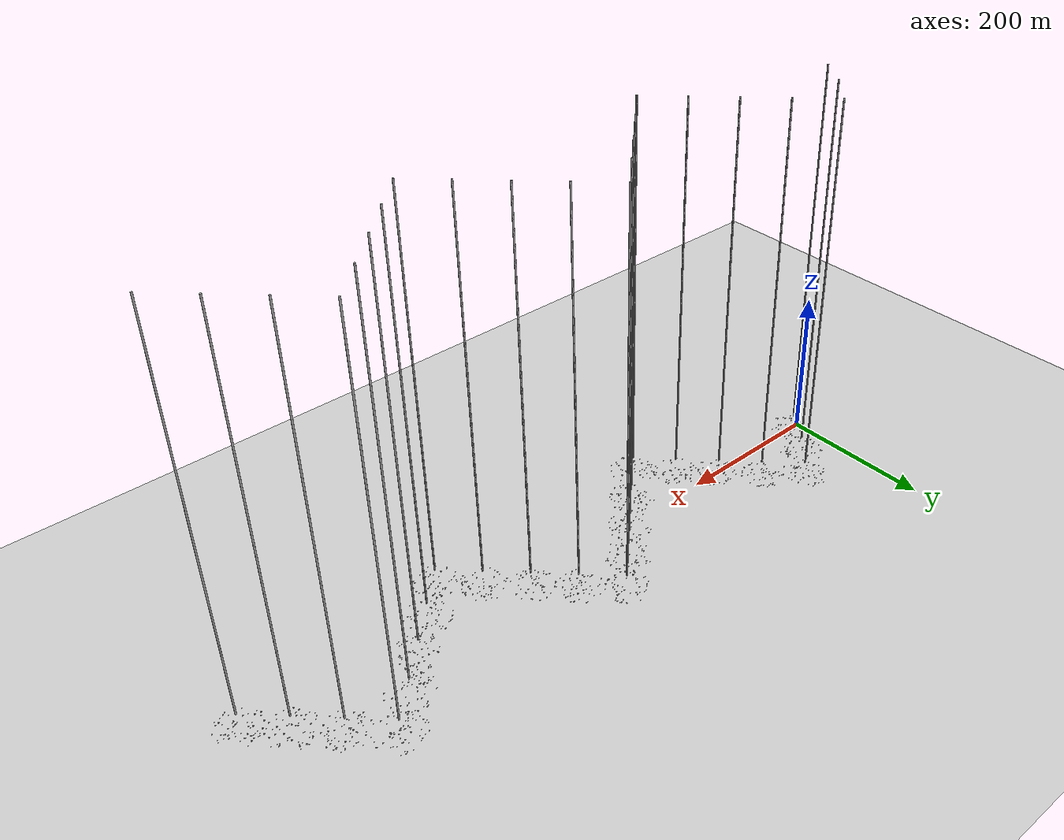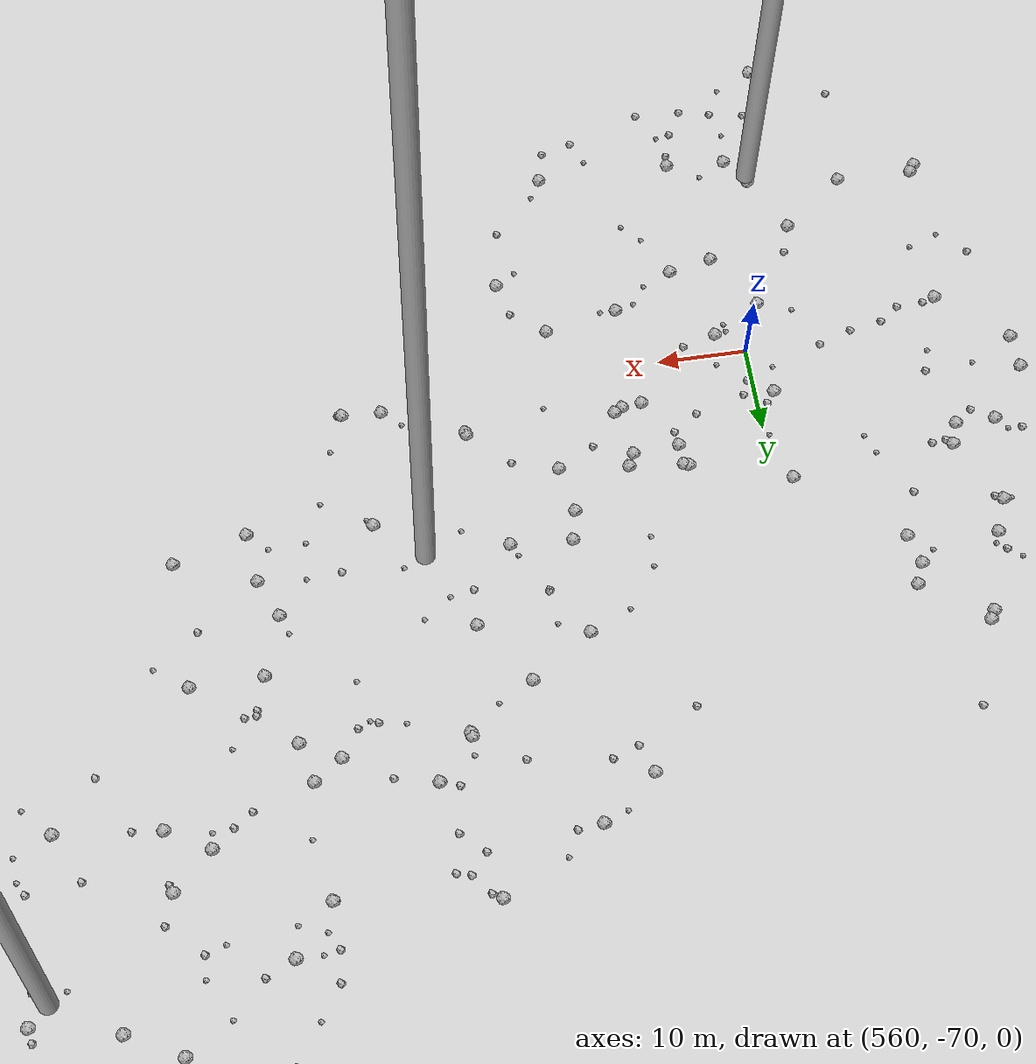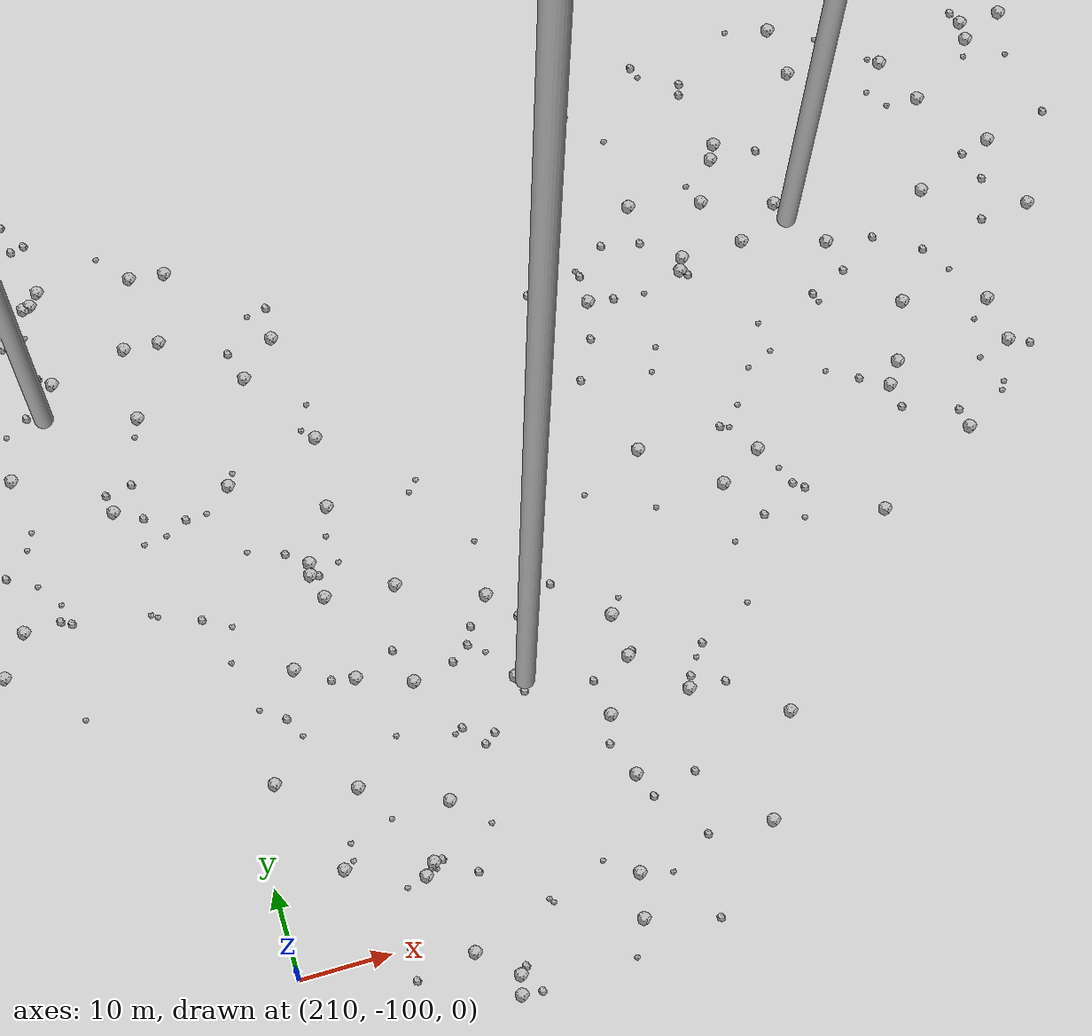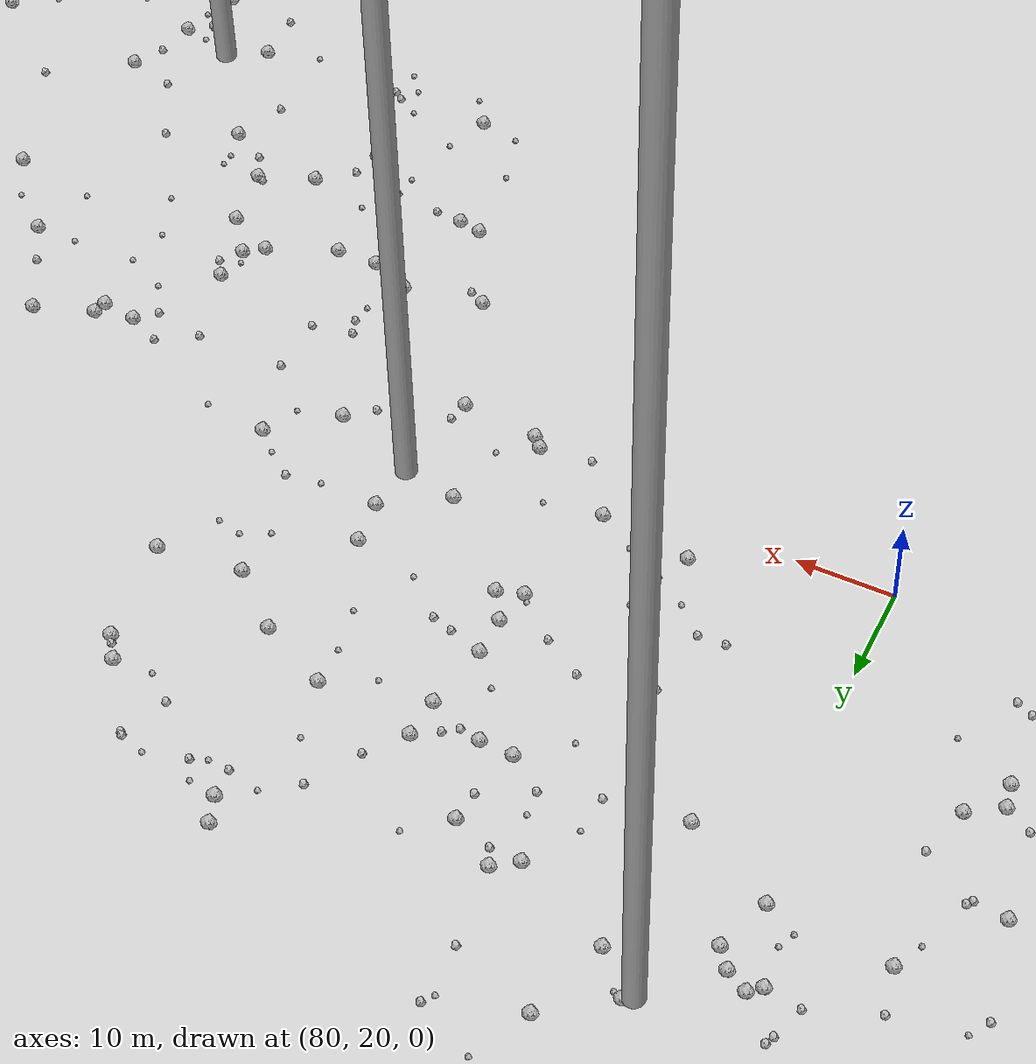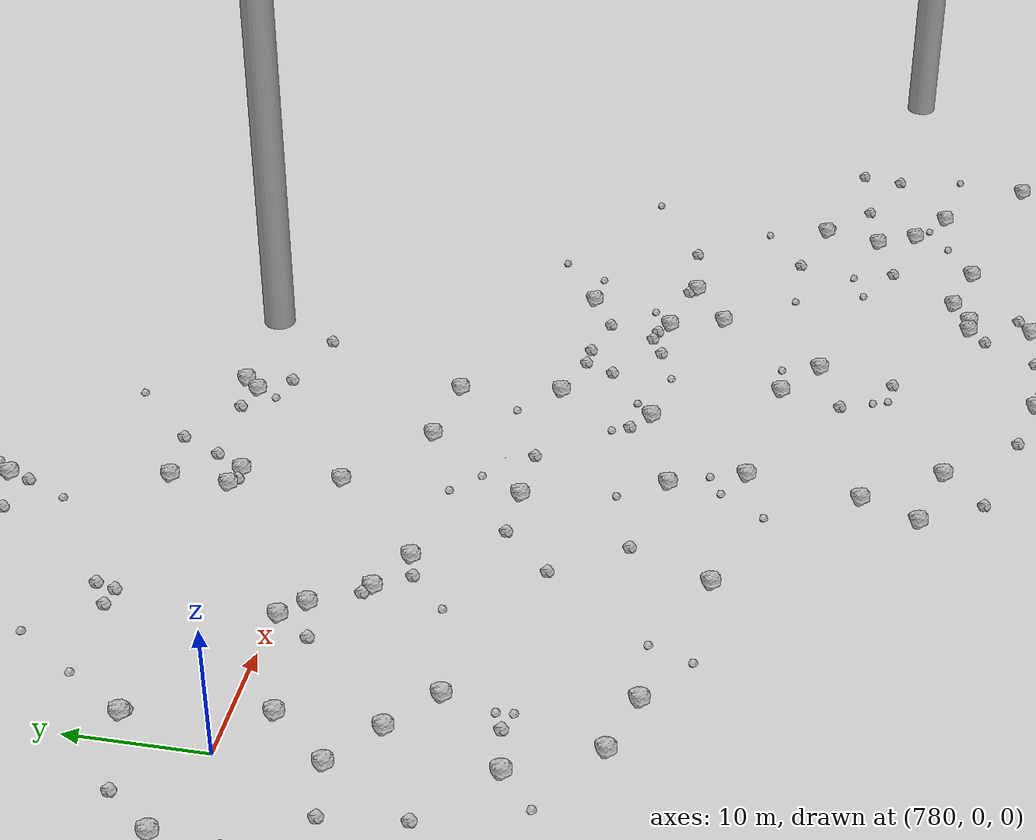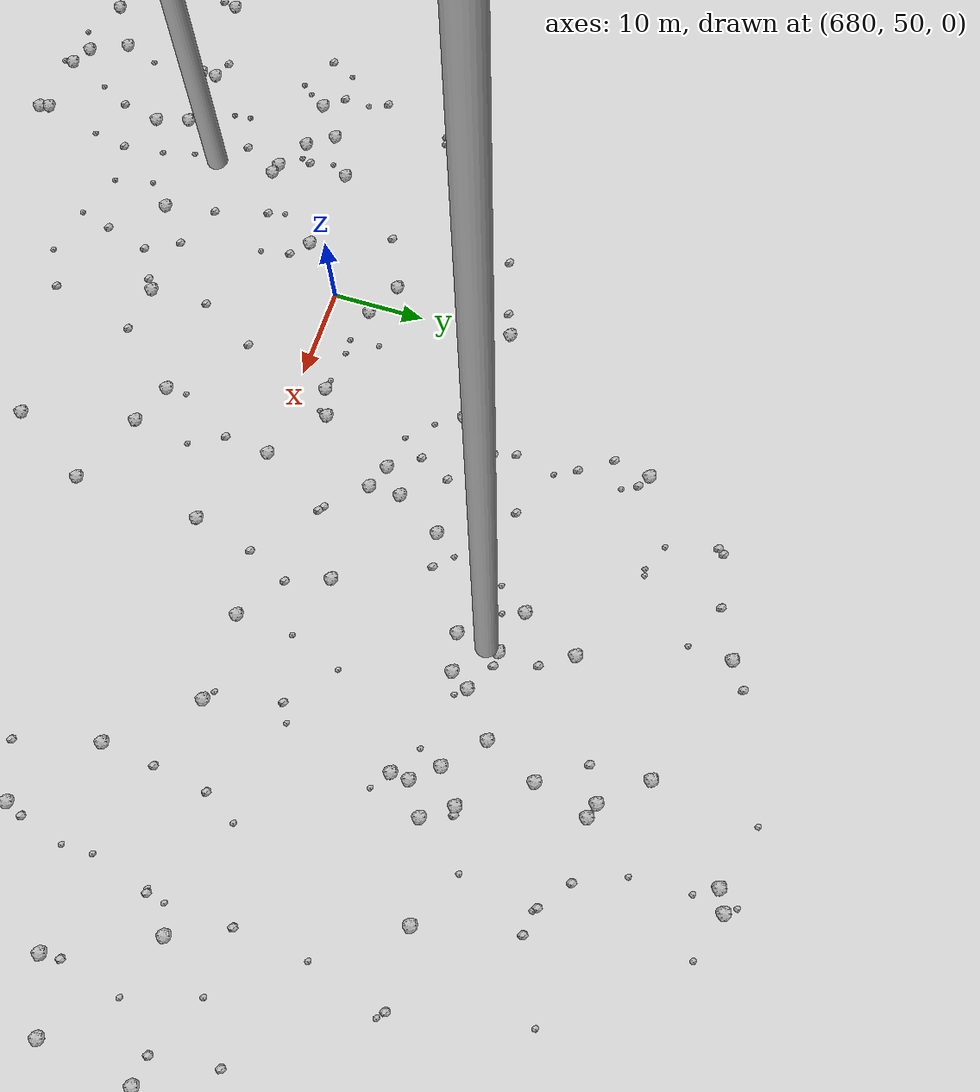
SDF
<sdf version="1.6">
 <world name="default">
  <include><uri>model://custom_ground</uri></include>
  <include><uri>model://sun</uri></include>
  <spherical_coordinates>
   <surface_model>EARTH_WGS84</surface_model>
   <latitude_deg>38.161479</latitude_deg>
   <longitude_deg>-122.454630</longitude_deg>
   <elevation>488.0</elevation>
   <heading_deg>90</heading_deg>
  </spherical_coordinates>
  <model name="rock1_0_0">
   <include><uri>model://rock1</uri><pose>9.448979469801706 -19.343021244370924 0.5 0 0 0</pose></include>
  </model>
  <model name="rock1_0_1">
   <include><uri>model://rock1</uri><pose>-4.434018164329796 -14.554310356891143 0.5 0 0 0</pose></include>
  </model>
  <model name="rock1_0_2">
   <include><uri>model://rock1</uri><pose>12.777897761383656 -10.472782780882966 0.5 0 0 0</pose></include>
  </model>
  <model name="rock1_0_3">
   <include><uri>model://rock1</uri><pose>27.933578570801686 -3.4902449042114334 0.5 0 0 0</pose></include>
  </model>
  <model name="rock1_0_4">
   <include><uri>model://rock1</uri><pose>-13.503053385169414 11.293394596494451 0.5 0 0 0</pose></include>
  </model>
  <model name="rock1_0_5">
   <include><uri>model://rock1</uri><pose>9.508447347933139 12.647558570382444 0.5 0 0 0</pose></include>
  </model>
  <model name="rock1_0_6">
   <include><uri>model://rock1</uri><pose>1.3028774116627773 3.640062521614901 0.5 0 0 0</pose></include>
  </model>
  <model name="rock1_0_7">
   <include><uri>model://rock1</uri><pose>28.773990198325556 1.8024056180203445 0.5 0 0 0</pose></include>
  </model>
  <model name="rock1_0_8">
   <include><uri>model://rock1</uri><pose>11.07136475963063 5.042677098354211 0.5 0 0 0</pose></include>
  </model>
  <model name="rock1_0_9">
   <include><uri>model://rock1</uri><pose>19.467665055672654 22.871719026562502 0.5 0 0 0</pose></include>
  </model>
  <model name="rock1_0_10">
   <include><uri>model://rock1</uri><pose>19.800107300917936 -16.76744211932853 0.5 0 0 0</pose></include>
  </model>
  <model name="rock1_0_11">
   <include><uri>model://rock1</uri><pose>7.429511196122508 4.65943302648801 0.5 0 0 0</pose></include>
  </model>
  <model name="rock1_0_12">
   <include><uri>model://rock1</uri><pose>9.403424226549284 -27.239508349058646 0.5 0 0 0</pose></include>
  </model>
  <model name="rock1_0_13">
   <include><uri>model://rock1</uri><pose>1.604297174130835 -20.518452971258327 0.5 0 0 0</pose></include>
  </model>
  <model name="rock1_0_14">
   <include><uri>model://rock1</uri><pose>23.675997567761016 8.810422304253066 0.5 0 0 0</pose></include>
  </model>
  <model name="rock1_0_15">
   <include><uri>model://rock1</uri><pose>-12.967196995197304 -10.012628839097072 0.5 0 0 0</pose></include>
  </model>
  <model name="rock1_0_16">
   <include><uri>model://rock1</uri><pose>6.127649286329948 1.4362429914853756 0.5 0 0 0</pose></include>
  </model>
  <model name="rock1_0_17">
   <include><uri>model://rock1</uri><pose>1.120703687442962 -24.28224147700317 0.5 0 0 0</pose></include>
  </model>
  <model name="rock1_0_18">
   <include><uri>model://rock1</uri><pose>-8.030001528610963 5.71334484097914 0.5 0 0 0</pose></include>
  </model>
  <model name="rock1_0_19">
   <include><uri>model://rock1</uri><pose>17.69391748162395 -14.383520134248073 0.5 0 0 0</pose></include>
  </model>
  <model name="rock1_0_20">
   <include><uri>model://rock1</uri><pose>0.14456255416076758 17.610642472481004 0.5 0 0 0</pose></include>
  </model>
  <model name="rock1_0_21">
   <include><uri>model://rock1</uri><pose>-11.732966740528529 -4.515447297036999 0.5 0 0 0</pose></include>
  </model>
  <model name="rock1_0_22">
   <include><uri>model://rock1</uri><pose>-4.161983485137881 1.058054783213617 0.5 0 0 0</pose></include>
  </model>
  <model name="rock1_0_23">
   <include><uri>model://rock1</uri><pose>20.79106587909837 -15.771740925045458 0.5 0 0 0</pose></include>
  </model>
  <model name="rock1_0_24">
   <include><uri>model://rock1</uri><pose>34.0531641386057 -16.166427706315115 0.5 0 0 0</pose></include>
  </model>
  <model name="rock1_0_25">
   <include><uri>model://rock1</uri><pose>7.490609495084804 -4.925991211970999 0.5 0 0 0</pose></include>
  </model>
  <model name="rock1_0_26">
   <include><uri>model://rock1</uri><pose>24.892817028184638 18.271191433835853 0.5 0 0 0</pose></include>
  </model>
  <model name="rock2_0_0">
   <include><uri>model://rock2</uri><pose>17.365885084460608 -5.086413257825132 0.3 0 0 0</pose></include>
  </model>
  <model name="rock2_0_1">
   <include><uri>model://rock2</uri><pose>-11.901473323353251 -6.426137141254429 0.3 0 0 0</pose></include>
  </model>
  <model name="rock2_0_2">
   <include><uri>model://rock2</uri><pose>0.5114922577158438 -17.135516795614976 0.3 0 0 0</pose></include>
  </model>
  <model name="rock2_0_3">
   <include><uri>model://rock2</uri><pose>7.991544347997866 -0.6631534520618843 0.3 0 0 0</pose></include>
  </model>
  <model name="rock2_0_4">
   <include><uri>model://rock2</uri><pose>-6.915222607623797 -15.353517363011353 0.3 0 0 0</pose></include>
  </model>
  <model name="rock2_0_5">
   <include><uri>model://rock2</uri><pose>38.591558092992706 0.7148452844662643 0.3 0 0 0</pose></include>
  </model>
  <model name="rock2_0_6">
   <include><uri>model://rock2</uri><pose>21.65528033153877 -26.242842507358585 0.3 0 0 0</pose></include>
  </model>
  <model name="rock2_0_7">
   <include><uri>model://rock2</uri><pose>23.567815344443105 22.404274511093625 0.3 0 0 0</pose></include>
  </model>
  <model name="rock2_0_8">
   <include><uri>model://rock2</uri><pose>27.221587549282937 -10.342193618498094 0.3 0 0 0</pose></include>
  </model>
  <model name="rock2_0_9">
   <include><uri>model://rock2</uri><pose>-1.0421759265261308 -12.050262009180823 0.3 0 0 0</pose></include>
  </model>
  <model name="rock2_0_10">
   <include><uri>model://rock2</uri><pose>30.831276049990322 -2.3605409832194155 0.3 0 0 0</pose></include>
  </model>
  <model name="rock2_0_11">
   <include><uri>model://rock2</uri><pose>4.624436938557523 21.691584851252045 0.3 0 0 0</pose></include>
  </model>
  <model name="rock2_0_12">
   <include><uri>model://rock2</uri><pose>25.86653116396586 -3.028961071903268 0.3 0 0 0</pose></include>
  </model>
  <model name="rock2_0_13">
   <include><uri>model://rock2</uri><pose>19.751478434464545 4.7232086297107045 0.3 0 0 0</pose></include>
  </model>
  <model name="rock2_0_14">
   <include><uri>model://rock2</uri><pose>13.139137756913335 -2.8974484981684228 0.3 0 0 0</pose></include>
  </model>
  <model name="rock2_0_15">
   <include><uri>model://rock2</uri><pose>-3.9719490051232462 7.609835823463676 0.3 0 0 0</pose></include>
  </model>
  <model name="rock2_0_16">
   <include><uri>model://rock2</uri><pose>5.274828786451341 26.288294022824026 0.3 0 0 0</pose></include>
  </model>
  <model name="rock2_0_17">
   <include><uri>model://rock2</uri><pose>-6.507646353588745 16.532798415000897 0.3 0 0 0</pose></include>
  </model>
  <model name="rock2_0_18">
   <include><uri>model://rock2</uri><pose>1.107687609307952 16.034568069008785 0.3 0 0 0</pose></include>
  </model>
  <model name="rock2_0_19">
   <include><uri>model://rock2</uri><pose>-8.657049335730465 -20.000032153478877 0.3 0 0 0</pose></include>
  </model>
  <model name="rock2_0_20">
   <include><uri>model://rock2</uri><pose>1.8840054501971473 28.323882314588822 0.3 0 0 0</pose></include>
  </model>
  <model name="rock2_0_21">
   <include><uri>model://rock2</uri><pose>11.11048566473362 -8.52596243145953 0.3 0 0 0</pose></include>
  </model>
  <model name="rock2_0_22">
   <include><uri>model://rock2</uri><pose>24.70291910590582 12.345118563392475 0.3 0 0 0</pose></include>
  </model>
  <model name="rock2_0_23">
   <include><uri>model://rock2</uri><pose>-9.449370035977577 -0.08969484744876866 0.3 0 0 0</pose></include>
  </model>
  <model name="rock2_0_24">
   <include><uri>model://rock2</uri><pose>-1.3089622416304216 -6.990050148239071 0.3 0 0 0</pose></include>
  </model>
  <model name="rock2_0_25">
   <include><uri>model://rock2</uri><pose>18.83067157609584 -5.838985639904511 0.3 0 0 0</pose></include>
  </model>
  <model name="rock2_0_26">
   <include><uri>model://rock2</uri><pose>34.11263183639121 7.379046994682206 0.3 0 0 0</pose></include>
  </model>
  <model name="rock3_0_0">
   <include><uri>model://rock3</uri><pose>20.755563061885447 -12.146216181200554 0.2 0 0 0</pose></include>
  </model>
  <model name="rock3_0_1">
   <include><uri>model://rock3</uri><pose>5.623046289705293 13.877157420778488 0.2 0 0 0</pose></include>
  </model>
  <model name="rock3_0_2">
   <include><uri>model://rock3</uri><pose>-14.004531066234476 0.5632900333179869 0.2 0 0 0</pose></include>
  </model>
  <model name="rock3_0_3">
   <include><uri>model://rock3</uri><pose>37.07775984742638 1.6949781171616571 0.2 0 0 0</pose></include>
  </model>
  <model name="rock3_0_4">
   <include><uri>model://rock3</uri><pose>4.802889656692269 -18.48818948893886 0.2 0 0 0</pose></include>
  </model>
  <model name="rock3_0_5">
   <include><uri>model://rock3</uri><pose>5.520423981477375 3.1950348857218813 0.2 0 0 0</pose></include>
  </model>
  <model name="rock3_0_6">
   <include><uri>model://rock3</uri><pose>-10.381536118190116 7.674178834108176 0.2 0 0 0</pose></include>
  </model>
  <model name="rock3_0_7">
   <include><uri>model://rock3</uri><pose>26.955543329913176 -14.770792795809287 0.2 0 0 0</pose></include>
  </model>
  <model name="rock3_0_8">
   <include><uri>model://rock3</uri><pose>22.46745022921924 22.184832350033602 0.2 0 0 0</pose></include>
  </model>
  <model name="rock3_0_9">
   <include><uri>model://rock3</uri><pose>-4.268493617024662 -17.357554295411244 0.2 0 0 0</pose></include>
  </model>
  <model name="rock3_0_10">
   <include><uri>model://rock3</uri><pose>10.209850108511468 -29.549977321917577 0.2 0 0 0</pose></include>
  </model>
  <model name="rock3_0_11">
   <include><uri>model://rock3</uri><pose>28.24614497048062 9.276420817937598 0.2 0 0 0</pose></include>
  </model>
  <model name="rock3_0_12">
   <include><uri>model://rock3</uri><pose>9.008625934554779 18.38246824643589 0.2 0 0 0</pose></include>
  </model>
  <model name="rock3_0_13">
   <include><uri>model://rock3</uri><pose>5.628263697388473 -27.307100008173446 0.2 0 0 0</pose></include>
  </model>
  <model name="rock3_0_14">
   <include><uri>model://rock3</uri><pose>6.70428734557747 3.144676375396898 0.2 0 0 0</pose></include>
  </model>
  <model name="rock3_0_15">
   <include><uri>model://rock3</uri><pose>-13.042365365346164 7.724803667624862 0.2 0 0 0</pose></include>
  </model>
  <model name="rock3_0_16">
   <include><uri>model://rock3</uri><pose>-7.830957958849414 14.996415877954433 0.2 0 0 0</pose></include>
  </model>
  <model name="rock3_0_17">
   <include><uri>model://rock3</uri><pose>13.237486961905184 11.1219628039945 0.2 0 0 0</pose></include>
  </model>
  <model name="rock3_0_18">
   <include><uri>model://rock3</uri><pose>0.16563001273605948 12.902104813379964 0.2 0 0 0</pose></include>
  </model>
  <model name="rock3_0_19">
   <include><uri>model://rock3</uri><pose>31.055069829935057 -12.145242816146624 0.2 0 0 0</pose></include>
  </model>
  <model name="rock3_0_20">
   <include><uri>model://rock3</uri><pose>5.892488309573075 1.9869842942160147 0.2 0 0 0</pose></include>
  </model>
  <model name="rock3_0_21">
   <include><uri>model://rock3</uri><pose>24.714741136969714 23.63827298687128 0.2 0 0 0</pose></include>
  </model>
  <model name="rock3_0_22">
   <include><uri>model://rock3</uri><pose>9.06937873771161 -23.69898766888661 0.2 0 0 0</pose></include>
  </model>
  <model name="rock3_0_23">
   <include><uri>model://rock3</uri><pose>10.578568274773495 20.57739693999069 0.2 0 0 0</pose></include>
  </model>
  <model name="rock3_0_24">
   <include><uri>model://rock3</uri><pose>-18.939620138847133 0.24876280802892126 0.2 0 0 0</pose></include>
  </model>
  <model name="rock3_0_25">
   <include><uri>model://rock3</uri><pose>4.556025670259572 10.495672247652266 0.2 0 0 0</pose></include>
  </model>
  <model name="rock3_0_26">
   <include><uri>model://rock3</uri><pose>-3.2592368224206254 0.5858908149569224 0.2 0 0 0</pose></include>
  </model>
  <model name="rock1_1_0">
   <include><uri>model://rock1</uri><pose>22.561638484577067 60.342364810881655 0.5 0 0 0</pose></include>
  </model>
  <model name="rock1_1_1">
   <include><uri>model://rock1</uri><pose>18.655693357128524 44.10045396198601 0.5 0 0 0</pose></include>
  </model>
  <model name="rock1_1_2">
   <include><uri>model://rock1</uri><pose>45.045154896620865 32.04116261820445 0.5 0 0 0</pose></include>
  </model>
  <model name="rock1_1_3">
   <include><uri>model://rock1</uri><pose>36.44557837447828 11.436857886736744 0.5 0 0 0</pose></include>
  </model>
  <model name="rock1_1_4">
   <include><uri>model://rock1</uri><pose>25.61342185134179 48.222978169900706 0.5 0 0 0</pose></include>
  </model>
  <model name="rock1_1_5">
   <include><uri>model://rock1</uri><pose>13.56787048983221 35.5808037187216 0.5 0 0 0</pose></include>
  </model>
  <model name="rock1_1_6">
   <include><uri>model://rock1</uri><pose>40.66508996179598 21.736500482871033 0.5 0 0 0</pose></include>
  </model>
  <model name="rock1_1_7">
   <include><uri>model://rock1</uri><pose>41.5480478026593 22.607156876467286 0.5 0 0 0</pose></include>
  </model>
  <model name="rock1_1_8">
   <include><uri>model://rock1</uri><pose>21.64977685446436 20.238830180173828 0.5 0 0 0</pose></include>
  </model>
  <model name="rock1_1_9">
   <include><uri>model://rock1</uri><pose>54.17233913600561 29.16856448644139 0.5 0 0 0</pose></include>
  </model>
  <model name="rock1_1_10">
   <include><uri>model://rock1</uri><pose>36.22735819246637 40.75111012739788 0.5 0 0 0</pose></include>
  </model>
  <model name="rock1_1_11">
   <include><uri>model://rock1</uri><pose>62.858354162133125 35.617287952038 0.5 0 0 0</pose></include>
  </model>
  <model name="rock1_1_12">
   <include><uri>model://rock1</uri><pose>50.2657698572869 26.596138891535023 0.5 0 0 0</pose></include>
  </model>
  <model name="rock1_1_13">
   <include><uri>model://rock1</uri><pose>21.698803477656277 25.383591956720494 0.5 0 0 0</pose></include>
  </model>
  <model name="rock1_1_14">
   <include><uri>model://rock1</uri><pose>62.35315932322479 38.113514252972664 0.5 0 0 0</pose></include>
  </model>
  <model name="rock1_1_15">
   <include><uri>model://rock1</uri><pose>52.515111706848586 22.907440242574452 0.5 0 0 0</pose></include>
  </model>
  <model name="rock1_1_16">
   <include><uri>model://rock1</uri><pose>36.44416462354904 21.154530399045576 0.5 0 0 0</pose></include>
  </model>
  <model name="rock1_1_17">
   <include><uri>model://rock1</uri><pose>44.781780697878524 56.771890122192914 0.5 0 0 0</pose></include>
  </model>
  <model name="rock1_1_18">
   <include><uri>model://rock1</uri><pose>54.58388930971593 34.811667740869204 0.5 0 0 0</pose></include>
  </model>
  <model name="rock1_1_19">
   <include><uri>model://rock1</uri><pose>14.803352267744339 43.061284700433454 0.5 0 0 0</pose></include>
  </model>
  <model name="rock1_1_20">
   <include><uri>model://rock1</uri><pose>65.67454584648013 40.17703881595014 0.5 0 0 0</pose></include>
  </model>
  <model name="rock1_1_21">
   <include><uri>model://rock1</uri><pose>57.83590775578064 31.255590903026974 0.5 0 0 0</pose></include>
  </model>
  <model name="rock1_1_22">
   <include><uri>model://rock1</uri><pose>58.23704750419243 48.95045051500603 0.5 0 0 0</pose></include>
  </model>
  <model name="rock1_1_23">
   <include><uri>model://rock1</uri><pose>27.73990594238848 28.073557560837934 0.5 0 0 0</pose></include>
  </model>
  <model name="rock1_1_24">
   <include><uri>model://rock1</uri><pose>59.09632335206015 35.50980235372165 0.5 0 0 0</pose></include>
  </model>
  <model name="rock1_1_25">
   <include><uri>model://rock1</uri><pose>32.9142791679129 58.9091257750981 0.5 0 0 0</pose></include>
  </model>
  <model name="rock1_1_26">
   <include><uri>model://rock1</uri><pose>51.10743913430662 58.304431969667604 0.5 0 0 0</pose></include>
  </model>
  <model name="rock2_1_0">
   <include><uri>model://rock2</uri><pose>36.92489624302638 61.48187548738222 0.3 0 0 0</pose></include>
  </model>
  <model name="rock2_1_1">
   <include><uri>model://rock2</uri><pose>27.221614064217256 36.75765137400704 0.3 0 0 0</pose></include>
  </model>
  <model name="rock2_1_2">
   <include><uri>model://rock2</uri><pose>60.08918820567629 27.557306266913017 0.3 0 0 0</pose></include>
  </model>
  <model name="rock2_1_3">
   <include><uri>model://rock2</uri><pose>18.228884190068054 39.25169047243078 0.3 0 0 0</pose></include>
  </model>
  <model name="rock2_1_4">
   <include><uri>model://rock2</uri><pose>31.65321431291698 43.6664973561612 0.3 0 0 0</pose></include>
  </model>
  <model name="rock2_1_5">
   <include><uri>model://rock2</uri><pose>19.334053558881422 50.88782040987446 0.3 0 0 0</pose></include>
  </model>
  <model name="rock2_1_6">
   <include><uri>model://rock2</uri><pose>40.58525103329388 26.911750174043206 0.3 0 0 0</pose></include>
  </model>
  <model name="rock2_1_7">
   <include><uri>model://rock2</uri><pose>49.90877022100082 51.73032028463035 0.3 0 0 0</pose></include>
  </model>
  <model name="rock2_1_8">
   <include><uri>model://rock2</uri><pose>39.49487495960109 43.12108324904465 0.3 0 0 0</pose></include>
  </model>
  <model name="rock2_1_9">
   <include><uri>model://rock2</uri><pose>54.04864981834081 38.36390336620542 0.3 0 0 0</pose></include>
  </model>
  <model name="rock2_1_10">
   <include><uri>model://rock2</uri><pose>49.06220140553997 57.54711498144993 0.3 0 0 0</pose></include>
  </model>
  <model name="rock2_1_11">
   <include><uri>model://rock2</uri><pose>62.10407728359584 48.92117031499877 0.3 0 0 0</pose></include>
  </model>
  <model name="rock2_1_12">
   <include><uri>model://rock2</uri><pose>29.94092888081717 36.1651394286125 0.3 0 0 0</pose></include>
  </model>
  <model name="rock2_1_13">
   <include><uri>model://rock2</uri><pose>59.57642451797815 39.62874503877448 0.3 0 0 0</pose></include>
  </model>
  <model name="rock2_1_14">
   <include><uri>model://rock2</uri><pose>54.52372736390016 16.805086749359905 0.3 0 0 0</pose></include>
  </model>
  <model name="rock2_1_15">
   <include><uri>model://rock2</uri><pose>36.28332870221732 45.50698645864956 0.3 0 0 0</pose></include>
  </model>
  <model name="rock2_1_16">
   <include><uri>model://rock2</uri><pose>60.49530569700168 26.642031237756626 0.3 0 0 0</pose></include>
  </model>
  <model name="rock2_1_17">
   <include><uri>model://rock2</uri><pose>21.586495914172843 62.70301915631422 0.3 0 0 0</pose></include>
  </model>
  <model name="rock2_1_18">
   <include><uri>model://rock2</uri><pose>44.777491953076364 37.66644865892664 0.3 0 0 0</pose></include>
  </model>
  <model name="rock2_1_19">
   <include><uri>model://rock2</uri><pose>67.23285543840116 45.30405240808715 0.3 0 0 0</pose></include>
  </model>
  <model name="rock2_1_20">
   <include><uri>model://rock2</uri><pose>61.65870513110181 48.39316009549415 0.3 0 0 0</pose></include>
  </model>
  <model name="rock2_1_21">
   <include><uri>model://rock2</uri><pose>14.464893085575694 51.57700543866269 0.3 0 0 0</pose></include>
  </model>
  <model name="rock2_1_22">
   <include><uri>model://rock2</uri><pose>65.39361429396172 26.838870111734295 0.3 0 0 0</pose></include>
  </model>
  <model name="rock2_1_23">
   <include><uri>model://rock2</uri><pose>63.692665385037955 27.622615834844716 0.3 0 0 0</pose></include>
  </model>
  <model name="rock2_1_24">
   <include><uri>model://rock2</uri><pose>56.10882392431906 59.01940050670307 0.3 0 0 0</pose></include>
  </model>
  <model name="rock2_1_25">
   <include><uri>model://rock2</uri><pose>59.54369819145159 30.656865714650138 0.3 0 0 0</pose></include>
  </model>
  <model name="rock2_1_26">
   <include><uri>model://rock2</uri><pose>35.35825706155577 56.269936518562055 0.3 0 0 0</pose></include>
  </model>
  <model name="rock3_1_0">
   <include><uri>model://rock3</uri><pose>27.052514953727446 46.71404531170841 0.2 0 0 0</pose></include>
  </model>
  <model name="rock3_1_1">
   <include><uri>model://rock3</uri><pose>39.7464663222142 29.91719383576427 0.2 0 0 0</pose></include>
  </model>
  <model name="rock3_1_2">
   <include><uri>model://rock3</uri><pose>62.75586063822636 21.578294566392387 0.2 0 0 0</pose></include>
  </model>
  <model name="rock3_1_3">
   <include><uri>model://rock3</uri><pose>64.03585301608081 54.43465843570584 0.2 0 0 0</pose></include>
  </model>
  <model name="rock3_1_4">
   <include><uri>model://rock3</uri><pose>19.56934352309167 31.06164171047563 0.2 0 0 0</pose></include>
  </model>
  <model name="rock3_1_5">
   <include><uri>model://rock3</uri><pose>50.37666743404667 40.840017445457384 0.2 0 0 0</pose></include>
  </model>
  <model name="rock3_1_6">
   <include><uri>model://rock3</uri><pose>30.224361981279607 64.36202200080731 0.2 0 0 0</pose></include>
  </model>
  <model name="rock3_1_7">
   <include><uri>model://rock3</uri><pose>54.32551277458953 50.50245847661533 0.2 0 0 0</pose></include>
  </model>
  <model name="rock3_1_8">
   <include><uri>model://rock3</uri><pose>68.92945294382139 32.733946236560996 0.2 0 0 0</pose></include>
  </model>
  <model name="rock3_1_9">
   <include><uri>model://rock3</uri><pose>22.200663296790168 58.02723558001869 0.2 0 0 0</pose></include>
  </model>
  <model name="rock3_1_10">
   <include><uri>model://rock3</uri><pose>54.569653126111405 30.68037856496136 0.2 0 0 0</pose></include>
  </model>
  <model name="rock3_1_11">
   <include><uri>model://rock3</uri><pose>28.599865250746628 59.25796263014214 0.2 0 0 0</pose></include>
  </model>
  <model name="rock3_1_12">
   <include><uri>model://rock3</uri><pose>21.127185085615743 33.03258833120274 0.2 0 0 0</pose></include>
  </model>
  <model name="rock3_1_13">
   <include><uri>model://rock3</uri><pose>19.00214606845121 61.312117447680386 0.2 0 0 0</pose></include>
  </model>
  <model name="rock3_1_14">
   <include><uri>model://rock3</uri><pose>36.41134405537185 69.36253909971587 0.2 0 0 0</pose></include>
  </model>
  <model name="rock3_1_15">
   <include><uri>model://rock3</uri><pose>43.73328650281895 15.142577056210648 0.2 0 0 0</pose></include>
  </model>
  <model name="rock3_1_16">
   <include><uri>model://rock3</uri><pose>45.43151826409781 24.32565394475005 0.2 0 0 0</pose></include>
  </model>
  <model name="rock3_1_17">
   <include><uri>model://rock3</uri><pose>36.04241393880787 39.00376130894903 0.2 0 0 0</pose></include>
  </model>
  <model name="rock3_1_18">
   <include><uri>model://rock3</uri><pose>18.58113298753618 56.58644453795467 0.2 0 0 0</pose></include>
  </model>
  <model name="rock3_1_19">
   <include><uri>model://rock3</uri><pose>46.38998141629493 63.25187644740005 0.2 0 0 0</pose></include>
  </model>
  <model name="rock3_1_20">
   <include><uri>model://rock3</uri><pose>21.115524301452204 33.52230341156525 0.2 0 0 0</pose></include>
  </model>
  <model name="rock3_1_21">
   <include><uri>model://rock3</uri><pose>12.319649042997538 30.24564228647614 0.2 0 0 0</pose></include>
  </model>
  <model name="rock3_1_22">
   <include><uri>model://rock3</uri><pose>21.232910211325713 41.76505280466088 0.2 0 0 0</pose></include>
  </model>
  <model name="rock3_1_23">
   <include><uri>model://rock3</uri><pose>34.115391499836846 38.93793022050855 0.2 0 0 0</pose></include>
  </model>
  <model name="rock3_1_24">
   <include><uri>model://rock3</uri><pose>23.808569085074122 19.089543181023398 0.2 0 0 0</pose></include>
  </model>
  <model name="rock3_1_25">
   <include><uri>model://rock3</uri><pose>27.24628816952265 27.441235983585045 0.2 0 0 0</pose></include>
  </model>
  <model name="rock3_1_26">
   <include><uri>model://rock3</uri><pose>55.61215713640581 17.621908314957537 0.2 0 0 0</pose></include>
  </model>
  <model name="rock1_2_0">
   <include><uri>model://rock1</uri><pose>76.03060371757273 65.06138391501489 0.5 0 0 0</pose></include>
  </model>
  <model name="rock1_2_1">
   <include><uri>model://rock1</uri><pose>62.75816124154134 93.83177062951076 0.5 0 0 0</pose></include>
  </model>
  <model name="rock1_2_2">
   <include><uri>model://rock1</uri><pose>77.81528226097475 56.26868825143002 0.5 0 0 0</pose></include>
  </model>
  <model name="rock1_2_3">
   <include><uri>model://rock1</uri><pose>57.5658624990832 94.13604172745069 0.5 0 0 0</pose></include>
  </model>
  <model name="rock1_2_4">
   <include><uri>model://rock1</uri><pose>98.98146185713625 61.26798605459563 0.5 0 0 0</pose></include>
  </model>
  <model name="rock1_2_5">
   <include><uri>model://rock1</uri><pose>82.62764861848609 101.74090219567547 0.5 0 0 0</pose></include>
  </model>
  <model name="rock1_2_6">
   <include><uri>model://rock1</uri><pose>60.00804068326274 88.62505785375413 0.5 0 0 0</pose></include>
  </model>
  <model name="rock1_2_7">
   <include><uri>model://rock1</uri><pose>63.43859818111405 95.35828781109973 0.5 0 0 0</pose></include>
  </model>
  <model name="rock1_2_8">
   <include><uri>model://rock1</uri><pose>74.79487420860607 64.02986545965261 0.5 0 0 0</pose></include>
  </model>
  <model name="rock1_2_9">
   <include><uri>model://rock1</uri><pose>85.32060100874018 70.08692866229629 0.5 0 0 0</pose></include>
  </model>
  <model name="rock1_2_10">
   <include><uri>model://rock1</uri><pose>79.81542062330763 61.81132097865443 0.5 0 0 0</pose></include>
  </model>
  <model name="rock1_2_11">
   <include><uri>model://rock1</uri><pose>73.56859888950805 93.96203670200802 0.5 0 0 0</pose></include>
  </model>
  <model name="rock1_2_12">
   <include><uri>model://rock1</uri><pose>87.10044090242462 51.26548099542661 0.5 0 0 0</pose></include>
  </model>
  <model name="rock1_2_13">
   <include><uri>model://rock1</uri><pose>74.4929380342099 108.32584467229466 0.5 0 0 0</pose></include>
  </model>
  <model name="rock1_2_14">
   <include><uri>model://rock1</uri><pose>91.76268728810398 74.63826942468113 0.5 0 0 0</pose></include>
  </model>
  <model name="rock1_2_15">
   <include><uri>model://rock1</uri><pose>78.31431421968689 63.775604739663 0.5 0 0 0</pose></include>
  </model>
  <model name="rock1_2_16">
   <include><uri>model://rock1</uri><pose>79.23474602751818 78.13602485519317 0.5 0 0 0</pose></include>
  </model>
  <model name="rock1_2_17">
   <include><uri>model://rock1</uri><pose>65.51673906719638 57.47325665779573 0.5 0 0 0</pose></include>
  </model>
  <model name="rock1_2_18">
   <include><uri>model://rock1</uri><pose>66.0823614607562 83.13125527117438 0.5 0 0 0</pose></include>
  </model>
  <model name="rock1_2_19">
   <include><uri>model://rock1</uri><pose>92.19876550390103 85.0391447912476 0.5 0 0 0</pose></include>
  </model>
  <model name="rock1_2_20">
   <include><uri>model://rock1</uri><pose>55.35911971131434 75.56454971818835 0.5 0 0 0</pose></include>
  </model>
  <model name="rock1_2_21">
   <include><uri>model://rock1</uri><pose>88.95674769432998 66.15156054150088 0.5 0 0 0</pose></include>
  </model>
  <model name="rock1_2_22">
   <include><uri>model://rock1</uri><pose>98.6486001269597 86.27885462804866 0.5 0 0 0</pose></include>
  </model>
  <model name="rock1_2_23">
   <include><uri>model://rock1</uri><pose>78.23819030543243 87.3147306674545 0.5 0 0 0</pose></include>
  </model>
  <model name="rock1_2_24">
   <include><uri>model://rock1</uri><pose>101.38354384885281 62.88766855343098 0.5 0 0 0</pose></include>
  </model>
  <model name="rock1_2_25">
   <include><uri>model://rock1</uri><pose>51.78635019366357 89.72499431155757 0.5 0 0 0</pose></include>
  </model>
  <model name="rock1_2_26">
   <include><uri>model://rock1</uri><pose>62.23467838621687 69.98973151742395 0.5 0 0 0</pose></include>
  </model>
  <model name="rock2_2_0">
   <include><uri>model://rock2</uri><pose>91.6211941403255 98.234022256731 0.3 0 0 0</pose></include>
  </model>
  <model name="rock2_2_1">
   <include><uri>model://rock2</uri><pose>77.6198705657524 86.25464439943663 0.3 0 0 0</pose></include>
  </model>
  <model name="rock2_2_2">
   <include><uri>model://rock2</uri><pose>95.64825003822736 100.58100369766774 0.3 0 0 0</pose></include>
  </model>
  <model name="rock2_2_3">
   <include><uri>model://rock2</uri><pose>100.43699529850915 71.24289125803789 0.3 0 0 0</pose></include>
  </model>
  <model name="rock2_2_4">
   <include><uri>model://rock2</uri><pose>60.96671281565562 88.63472117314748 0.3 0 0 0</pose></include>
  </model>
  <model name="rock2_2_5">
   <include><uri>model://rock2</uri><pose>70.11478773855171 76.46755442893746 0.3 0 0 0</pose></include>
  </model>
  <model name="rock2_2_6">
   <include><uri>model://rock2</uri><pose>74.40635670707539 96.39711370830969 0.3 0 0 0</pose></include>
  </model>
  <model name="rock2_2_7">
   <include><uri>model://rock2</uri><pose>50.03526377309503 80.82254228964077 0.3 0 0 0</pose></include>
  </model>
  <model name="rock2_2_8">
   <include><uri>model://rock2</uri><pose>52.0717113164303 87.83136531403021 0.3 0 0 0</pose></include>
  </model>
  <model name="rock2_2_9">
   <include><uri>model://rock2</uri><pose>71.00253710838888 90.23906333072406 0.3 0 0 0</pose></include>
  </model>
  <model name="rock2_2_10">
   <include><uri>model://rock2</uri><pose>79.92399470342471 105.14524291352579 0.3 0 0 0</pose></include>
  </model>
  <model name="rock2_2_11">
   <include><uri>model://rock2</uri><pose>70.8968777166325 102.99521995011914 0.3 0 0 0</pose></include>
  </model>
  <model name="rock2_2_12">
   <include><uri>model://rock2</uri><pose>104.38370772154015 97.33476586509526 0.3 0 0 0</pose></include>
  </model>
  <model name="rock2_2_13">
   <include><uri>model://rock2</uri><pose>60.4289547410067 75.38848797076369 0.3 0 0 0</pose></include>
  </model>
  <model name="rock2_2_14">
   <include><uri>model://rock2</uri><pose>71.0885140104449 64.59150534927699 0.3 0 0 0</pose></include>
  </model>
  <model name="rock2_2_15">
   <include><uri>model://rock2</uri><pose>52.6951322201604 75.98283511660802 0.3 0 0 0</pose></include>
  </model>
  <model name="rock2_2_16">
   <include><uri>model://rock2</uri><pose>68.28516676016875 73.8276839134084 0.3 0 0 0</pose></include>
  </model>
  <model name="rock2_2_17">
   <include><uri>model://rock2</uri><pose>89.45038443691189 104.1036887088171 0.3 0 0 0</pose></include>
  </model>
  <model name="rock2_2_18">
   <include><uri>model://rock2</uri><pose>87.15207173706257 64.47231059608575 0.3 0 0 0</pose></include>
  </model>
  <model name="rock2_2_19">
   <include><uri>model://rock2</uri><pose>64.45929352770139 62.11949790299427 0.3 0 0 0</pose></include>
  </model>
  <model name="rock2_2_20">
   <include><uri>model://rock2</uri><pose>68.28737505971705 78.22316045930624 0.3 0 0 0</pose></include>
  </model>
  <model name="rock2_2_21">
   <include><uri>model://rock2</uri><pose>100.69101336986881 77.46843148610192 0.3 0 0 0</pose></include>
  </model>
  <model name="rock2_2_22">
   <include><uri>model://rock2</uri><pose>72.58410012169729 68.90258031628547 0.3 0 0 0</pose></include>
  </model>
  <model name="rock2_2_23">
   <include><uri>model://rock2</uri><pose>75.84112668667157 81.78623381871957 0.3 0 0 0</pose></include>
  </model>
  <model name="rock2_2_24">
   <include><uri>model://rock2</uri><pose>69.34440876952254 92.04792775765024 0.3 0 0 0</pose></include>
  </model>
  <model name="rock2_2_25">
   <include><uri>model://rock2</uri><pose>55.80027158406111 67.27508449259685 0.3 0 0 0</pose></include>
  </model>
  <model name="rock2_2_26">
   <include><uri>model://rock2</uri><pose>72.2259771970091 67.9980418609255 0.3 0 0 0</pose></include>
  </model>
  <model name="rock3_2_0">
   <include><uri>model://rock3</uri><pose>70.86013203617978 84.96895639572276 0.2 0 0 0</pose></include>
  </model>
  <model name="rock3_2_1">
   <include><uri>model://rock3</uri><pose>61.82983235913356 97.64427076287335 0.2 0 0 0</pose></include>
  </model>
  <model name="rock3_2_2">
   <include><uri>model://rock3</uri><pose>64.25291537671964 71.8129333954059 0.2 0 0 0</pose></include>
  </model>
  <model name="rock3_2_3">
   <include><uri>model://rock3</uri><pose>73.29573310468426 93.891155613645 0.2 0 0 0</pose></include>
  </model>
  <model name="rock3_2_4">
   <include><uri>model://rock3</uri><pose>93.90261492456531 105.80494905469493 0.2 0 0 0</pose></include>
  </model>
  <model name="rock3_2_5">
   <include><uri>model://rock3</uri><pose>77.28842911657665 83.38875139444376 0.2 0 0 0</pose></include>
  </model>
  <model name="rock3_2_6">
   <include><uri>model://rock3</uri><pose>89.0160883360649 83.12879962996475 0.2 0 0 0</pose></include>
  </model>
  <model name="rock3_2_7">
   <include><uri>model://rock3</uri><pose>92.8070782847511 89.03024749246529 0.2 0 0 0</pose></include>
  </model>
  <model name="rock3_2_8">
   <include><uri>model://rock3</uri><pose>94.71304933912432 80.41028990344168 0.2 0 0 0</pose></include>
  </model>
  <model name="rock3_2_9">
   <include><uri>model://rock3</uri><pose>83.35017593602143 82.14335643772566 0.2 0 0 0</pose></include>
  </model>
  <model name="rock3_2_10">
   <include><uri>model://rock3</uri><pose>99.86607154894071 76.31912916675803 0.2 0 0 0</pose></include>
  </model>
  <model name="rock3_2_11">
   <include><uri>model://rock3</uri><pose>51.86427334879851 70.79476415272045 0.2 0 0 0</pose></include>
  </model>
  <model name="rock3_2_12">
   <include><uri>model://rock3</uri><pose>95.6283826771047 56.056190440414866 0.2 0 0 0</pose></include>
  </model>
  <model name="rock3_2_13">
   <include><uri>model://rock3</uri><pose>75.22179287687887 59.623207482973 0.2 0 0 0</pose></include>
  </model>
  <model name="rock3_2_14">
   <include><uri>model://rock3</uri><pose>73.47045399149766 104.61864185803657 0.2 0 0 0</pose></include>
  </model>
  <model name="rock3_2_15">
   <include><uri>model://rock3</uri><pose>86.23855755774798 69.6037435150796 0.2 0 0 0</pose></include>
  </model>
  <model name="rock3_2_16">
   <include><uri>model://rock3</uri><pose>63.43252561486855 79.41540896558838 0.2 0 0 0</pose></include>
  </model>
  <model name="rock3_2_17">
   <include><uri>model://rock3</uri><pose>56.75539862471753 87.4768966033675 0.2 0 0 0</pose></include>
  </model>
  <model name="rock3_2_18">
   <include><uri>model://rock3</uri><pose>70.04362092907263 102.90750755322102 0.2 0 0 0</pose></include>
  </model>
  <model name="rock3_2_19">
   <include><uri>model://rock3</uri><pose>85.762458577319 103.21816252296608 0.2 0 0 0</pose></include>
  </model>
  <model name="rock3_2_20">
   <include><uri>model://rock3</uri><pose>74.45171946568291 57.969030192761004 0.2 0 0 0</pose></include>
  </model>
  <model name="rock3_2_21">
   <include><uri>model://rock3</uri><pose>89.31843948580337 55.99676580028704 0.2 0 0 0</pose></include>
  </model>
  <model name="rock3_2_22">
   <include><uri>model://rock3</uri><pose>57.37463332566044 60.88029677375185 0.2 0 0 0</pose></include>
  </model>
  <model name="rock3_2_23">
   <include><uri>model://rock3</uri><pose>85.13635437007164 83.06390145034291 0.2 0 0 0</pose></include>
  </model>
  <model name="rock3_2_24">
   <include><uri>model://rock3</uri><pose>53.18704099585986 92.99325427566009 0.2 0 0 0</pose></include>
  </model>
  <model name="rock3_2_25">
   <include><uri>model://rock3</uri><pose>85.82647936588411 85.06534838157494 0.2 0 0 0</pose></include>
  </model>
  <model name="rock3_2_26">
   <include><uri>model://rock3</uri><pose>99.20161563268255 97.98992008961267 0.2 0 0 0</pose></include>
  </model>
  <model name="rock1_3_0">
   <include><uri>model://rock1</uri><pose>112.2225540122966 38.252588993317374 0.5 0 0 0</pose></include>
  </model>
  <model name="rock1_3_1">
   <include><uri>model://rock1</uri><pose>108.68985869883406 22.870706540358167 0.5 0 0 0</pose></include>
  </model>
  <model name="rock1_3_2">
   <include><uri>model://rock1</uri><pose>99.26144462120173 24.303752603766885 0.5 0 0 0</pose></include>
  </model>
  <model name="rock1_3_3">
   <include><uri>model://rock1</uri><pose>136.6441570542293 43.188109882867536 0.5 0 0 0</pose></include>
  </model>
  <model name="rock1_3_4">
   <include><uri>model://rock1</uri><pose>142.5002545287971 57.18642688143583 0.5 0 0 0</pose></include>
  </model>
  <model name="rock1_3_5">
   <include><uri>model://rock1</uri><pose>118.751630189564 16.72013113078676 0.5 0 0 0</pose></include>
  </model>
  <model name="rock1_3_6">
   <include><uri>model://rock1</uri><pose>144.0763203036468 54.82617214723144 0.5 0 0 0</pose></include>
  </model>
  <model name="rock1_3_7">
   <include><uri>model://rock1</uri><pose>136.89062313574465 22.203707819349866 0.5 0 0 0</pose></include>
  </model>
  <model name="rock1_3_8">
   <include><uri>model://rock1</uri><pose>126.69465904330247 15.939616338586958 0.5 0 0 0</pose></include>
  </model>
  <model name="rock1_3_9">
   <include><uri>model://rock1</uri><pose>124.22910513074211 51.529792593316785 0.5 0 0 0</pose></include>
  </model>
  <model name="rock1_3_10">
   <include><uri>model://rock1</uri><pose>106.16672198267716 59.67090497236057 0.5 0 0 0</pose></include>
  </model>
  <model name="rock1_3_11">
   <include><uri>model://rock1</uri><pose>143.15069227777514 27.091939144599543 0.5 0 0 0</pose></include>
  </model>
  <model name="rock1_3_12">
   <include><uri>model://rock1</uri><pose>128.46318490502875 35.31942422737178 0.5 0 0 0</pose></include>
  </model>
  <model name="rock1_3_13">
   <include><uri>model://rock1</uri><pose>122.5877007840617 26.860568562839344 0.5 0 0 0</pose></include>
  </model>
  <model name="rock1_3_14">
   <include><uri>model://rock1</uri><pose>111.3911071288616 34.5417230080095 0.5 0 0 0</pose></include>
  </model>
  <model name="rock1_3_15">
   <include><uri>model://rock1</uri><pose>126.72436842428161 66.46566447087972 0.5 0 0 0</pose></include>
  </model>
  <model name="rock1_3_16">
   <include><uri>model://rock1</uri><pose>113.64120691952695 49.164532049893076 0.5 0 0 0</pose></include>
  </model>
  <model name="rock1_3_17">
   <include><uri>model://rock1</uri><pose>114.01851212665031 35.33092984779171 0.5 0 0 0</pose></include>
  </model>
  <model name="rock1_3_18">
   <include><uri>model://rock1</uri><pose>145.2777710663612 44.040275021692125 0.5 0 0 0</pose></include>
  </model>
  <model name="rock1_3_19">
   <include><uri>model://rock1</uri><pose>107.95320636747635 51.2336012570433 0.5 0 0 0</pose></include>
  </model>
  <model name="rock1_3_20">
   <include><uri>model://rock1</uri><pose>125.78310109875875 69.2145993857602 0.5 0 0 0</pose></include>
  </model>
  <model name="rock1_3_21">
   <include><uri>model://rock1</uri><pose>117.72488993223088 17.833146004588375 0.5 0 0 0</pose></include>
  </model>
  <model name="rock1_3_22">
   <include><uri>model://rock1</uri><pose>104.51521118894104 51.43114963989489 0.5 0 0 0</pose></include>
  </model>
  <model name="rock1_3_23">
   <include><uri>model://rock1</uri><pose>112.30843878455823 42.301665180343996 0.5 0 0 0</pose></include>
  </model>
  <model name="rock1_3_24">
   <include><uri>model://rock1</uri><pose>113.95598837316336 53.25631185620954 0.5 0 0 0</pose></include>
  </model>
  <model name="rock1_3_25">
   <include><uri>model://rock1</uri><pose>128.925272479263 30.768826037130733 0.5 0 0 0</pose></include>
  </model>
  <model name="rock1_3_26">
   <include><uri>model://rock1</uri><pose>131.2388098544118 48.03913599169331 0.5 0 0 0</pose></include>
  </model>
  <model name="rock2_3_0">
   <include><uri>model://rock2</uri><pose>95.27799439634214 52.206347551477506 0.3 0 0 0</pose></include>
  </model>
  <model name="rock2_3_1">
   <include><uri>model://rock2</uri><pose>105.85292639987219 56.50442428285861 0.3 0 0 0</pose></include>
  </model>
  <model name="rock2_3_2">
   <include><uri>model://rock2</uri><pose>127.16765351293468 17.987914820801166 0.3 0 0 0</pose></include>
  </model>
  <model name="rock2_3_3">
   <include><uri>model://rock2</uri><pose>137.79053945681574 63.89366498625802 0.3 0 0 0</pose></include>
  </model>
  <model name="rock2_3_4">
   <include><uri>model://rock2</uri><pose>137.5299288792354 64.1532127659247 0.3 0 0 0</pose></include>
  </model>
  <model name="rock2_3_5">
   <include><uri>model://rock2</uri><pose>134.23212870308282 20.096284565457303 0.3 0 0 0</pose></include>
  </model>
  <model name="rock2_3_6">
   <include><uri>model://rock2</uri><pose>138.4771416167913 31.069338454193602 0.3 0 0 0</pose></include>
  </model>
  <model name="rock2_3_7">
   <include><uri>model://rock2</uri><pose>112.40992893299824 17.188293250350977 0.3 0 0 0</pose></include>
  </model>
  <model name="rock2_3_8">
   <include><uri>model://rock2</uri><pose>130.7036049765444 63.89796324856787 0.3 0 0 0</pose></include>
  </model>
  <model name="rock2_3_9">
   <include><uri>model://rock2</uri><pose>95.79000444788964 39.30071621676851 0.3 0 0 0</pose></include>
  </model>
  <model name="rock2_3_10">
   <include><uri>model://rock2</uri><pose>115.75526502419355 41.12777221258987 0.3 0 0 0</pose></include>
  </model>
  <model name="rock2_3_11">
   <include><uri>model://rock2</uri><pose>135.69333859507174 59.2973725950498 0.3 0 0 0</pose></include>
  </model>
  <model name="rock2_3_12">
   <include><uri>model://rock2</uri><pose>92.01426598232547 31.98602500244529 0.3 0 0 0</pose></include>
  </model>
  <model name="rock2_3_13">
   <include><uri>model://rock2</uri><pose>126.90645494699326 63.44440735280324 0.3 0 0 0</pose></include>
  </model>
  <model name="rock2_3_14">
   <include><uri>model://rock2</uri><pose>94.82666029312115 32.112869158386 0.3 0 0 0</pose></include>
  </model>
  <model name="rock2_3_15">
   <include><uri>model://rock2</uri><pose>117.91104442607951 40.44166372919178 0.3 0 0 0</pose></include>
  </model>
  <model name="rock2_3_16">
   <include><uri>model://rock2</uri><pose>100.91327895791513 53.998023913154114 0.3 0 0 0</pose></include>
  </model>
  <model name="rock2_3_17">
   <include><uri>model://rock2</uri><pose>103.11929448207245 40.81386384994278 0.3 0 0 0</pose></include>
  </model>
  <model name="rock2_3_18">
   <include><uri>model://rock2</uri><pose>102.38585218706473 28.701935422933897 0.3 0 0 0</pose></include>
  </model>
  <model name="rock2_3_19">
   <include><uri>model://rock2</uri><pose>102.16642836127868 61.04555280096769 0.3 0 0 0</pose></include>
  </model>
  <model name="rock2_3_20">
   <include><uri>model://rock2</uri><pose>143.55439742147843 55.57483130263966 0.3 0 0 0</pose></include>
  </model>
  <model name="rock2_3_21">
   <include><uri>model://rock2</uri><pose>110.09474508398728 50.72134561624519 0.3 0 0 0</pose></include>
  </model>
  <model name="rock2_3_22">
   <include><uri>model://rock2</uri><pose>120.12406579162307 61.978924344025884 0.3 0 0 0</pose></include>
  </model>
  <model name="rock2_3_23">
   <include><uri>model://rock2</uri><pose>116.90515627293924 56.867282923891516 0.3 0 0 0</pose></include>
  </model>
  <model name="rock2_3_24">
   <include><uri>model://rock2</uri><pose>111.49659157468874 51.72310633505445 0.3 0 0 0</pose></include>
  </model>
  <model name="rock2_3_25">
   <include><uri>model://rock2</uri><pose>100.9606365210467 27.419907869667085 0.3 0 0 0</pose></include>
  </model>
  <model name="rock2_3_26">
   <include><uri>model://rock2</uri><pose>107.14094813289454 38.34672178236142 0.3 0 0 0</pose></include>
  </model>
  <model name="rock3_3_0">
   <include><uri>model://rock3</uri><pose>139.07153402898737 39.20441539392459 0.2 0 0 0</pose></include>
  </model>
  <model name="rock3_3_1">
   <include><uri>model://rock3</uri><pose>104.74961260665503 25.29843464645943 0.2 0 0 0</pose></include>
  </model>
  <model name="rock3_3_2">
   <include><uri>model://rock3</uri><pose>122.74463801508638 57.57301196742346 0.2 0 0 0</pose></include>
  </model>
  <model name="rock3_3_3">
   <include><uri>model://rock3</uri><pose>121.33032173124069 19.97934408678988 0.2 0 0 0</pose></include>
  </model>
  <model name="rock3_3_4">
   <include><uri>model://rock3</uri><pose>99.97299803700167 47.71523662185856 0.2 0 0 0</pose></include>
  </model>
  <model name="rock3_3_5">
   <include><uri>model://rock3</uri><pose>97.6129396822551 29.377197697315562 0.2 0 0 0</pose></include>
  </model>
  <model name="rock3_3_6">
   <include><uri>model://rock3</uri><pose>123.54702701722482 64.22992274032916 0.2 0 0 0</pose></include>
  </model>
  <model name="rock3_3_7">
   <include><uri>model://rock3</uri><pose>125.01326139550503 42.8080685003313 0.2 0 0 0</pose></include>
  </model>
  <model name="rock3_3_8">
   <include><uri>model://rock3</uri><pose>110.83896817194946 35.14833464792345 0.2 0 0 0</pose></include>
  </model>
  <model name="rock3_3_9">
   <include><uri>model://rock3</uri><pose>141.2985186184008 23.338148442727253 0.2 0 0 0</pose></include>
  </model>
  <model name="rock3_3_10">
   <include><uri>model://rock3</uri><pose>141.558598318434 38.591952167859105 0.2 0 0 0</pose></include>
  </model>
  <model name="rock3_3_11">
   <include><uri>model://rock3</uri><pose>129.11581348312444 63.2068441623021 0.2 0 0 0</pose></include>
  </model>
  <model name="rock3_3_12">
   <include><uri>model://rock3</uri><pose>134.8993427465906 30.486148434903676 0.2 0 0 0</pose></include>
  </model>
  <model name="rock3_3_13">
   <include><uri>model://rock3</uri><pose>110.11295182540724 62.73431900096839 0.2 0 0 0</pose></include>
  </model>
  <model name="rock3_3_14">
   <include><uri>model://rock3</uri><pose>129.55097341808903 65.85487456361028 0.2 0 0 0</pose></include>
  </model>
  <model name="rock3_3_15">
   <include><uri>model://rock3</uri><pose>101.95685286245276 31.39091504926225 0.2 0 0 0</pose></include>
  </model>
  <model name="rock3_3_16">
   <include><uri>model://rock3</uri><pose>100.66614063502995 56.4983323905723 0.2 0 0 0</pose></include>
  </model>
  <model name="rock3_3_17">
   <include><uri>model://rock3</uri><pose>109.52774102459684 45.40764496461843 0.2 0 0 0</pose></include>
  </model>
  <model name="rock3_3_18">
   <include><uri>model://rock3</uri><pose>141.07857638599103 29.013339458330268 0.2 0 0 0</pose></include>
  </model>
  <model name="rock3_3_19">
   <include><uri>model://rock3</uri><pose>99.01688643221445 35.00018099778265 0.2 0 0 0</pose></include>
  </model>
  <model name="rock3_3_20">
   <include><uri>model://rock3</uri><pose>136.31334108497384 37.8919234722539 0.2 0 0 0</pose></include>
  </model>
  <model name="rock3_3_21">
   <include><uri>model://rock3</uri><pose>134.97759231596314 64.95510212639331 0.2 0 0 0</pose></include>
  </model>
  <model name="rock3_3_22">
   <include><uri>model://rock3</uri><pose>124.21824673444388 47.41405152402368 0.2 0 0 0</pose></include>
  </model>
  <model name="rock3_3_23">
   <include><uri>model://rock3</uri><pose>119.2560234226141 48.93778260165986 0.2 0 0 0</pose></include>
  </model>
  <model name="rock3_3_24">
   <include><uri>model://rock3</uri><pose>138.45460106224698 56.928726868434104 0.2 0 0 0</pose></include>
  </model>
  <model name="rock3_3_25">
   <include><uri>model://rock3</uri><pose>121.74124183553069 36.89890161849276 0.2 0 0 0</pose></include>
  </model>
  <model name="rock3_3_26">
   <include><uri>model://rock3</uri><pose>114.55020300735949 23.693163601697968 0.2 0 0 0</pose></include>
  </model>
  <model name="rock1_4_0">
   <include><uri>model://rock1</uri><pose>164.89859807533443 -7.819879176718423 0.5 0 0 0</pose></include>
  </model>
  <model name="rock1_4_1">
   <include><uri>model://rock1</uri><pose>148.70756970219048 -10.112625429759682 0.5 0 0 0</pose></include>
  </model>
  <model name="rock1_4_2">
   <include><uri>model://rock1</uri><pose>142.2009408418793 -20.0896061972202 0.5 0 0 0</pose></include>
  </model>
  <model name="rock1_4_3">
   <include><uri>model://rock1</uri><pose>161.90586902539462 19.627072039982984 0.5 0 0 0</pose></include>
  </model>
  <model name="rock1_4_4">
   <include><uri>model://rock1</uri><pose>139.20883974602475 4.463605249282558 0.5 0 0 0</pose></include>
  </model>
  <model name="rock1_4_5">
   <include><uri>model://rock1</uri><pose>143.29579028448967 2.7332157982834744 0.5 0 0 0</pose></include>
  </model>
  <model name="rock1_4_6">
   <include><uri>model://rock1</uri><pose>168.03644222082596 -20.09594616774553 0.5 0 0 0</pose></include>
  </model>
  <model name="rock1_4_7">
   <include><uri>model://rock1</uri><pose>135.71355167497592 -5.696955602717349 0.5 0 0 0</pose></include>
  </model>
  <model name="rock1_4_8">
   <include><uri>model://rock1</uri><pose>131.05047257619876 3.095943028082324 0.5 0 0 0</pose></include>
  </model>
  <model name="rock1_4_9">
   <include><uri>model://rock1</uri><pose>175.06620555437323 -21.371259148114504 0.5 0 0 0</pose></include>
  </model>
  <model name="rock1_4_10">
   <include><uri>model://rock1</uri><pose>165.47027464452617 19.05713303173649 0.5 0 0 0</pose></include>
  </model>
  <model name="rock1_4_11">
   <include><uri>model://rock1</uri><pose>159.1893542637972 3.1151720997658217 0.5 0 0 0</pose></include>
  </model>
  <model name="rock1_4_12">
   <include><uri>model://rock1</uri><pose>165.8850205585983 20.461977545656865 0.5 0 0 0</pose></include>
  </model>
  <model name="rock1_4_13">
   <include><uri>model://rock1</uri><pose>177.6148774173914 -19.70255676864816 0.5 0 0 0</pose></include>
  </model>
  <model name="rock1_4_14">
   <include><uri>model://rock1</uri><pose>154.45235401536843 5.5991955090206815 0.5 0 0 0</pose></include>
  </model>
  <model name="rock1_4_15">
   <include><uri>model://rock1</uri><pose>160.07149024175146 -3.1993166043717274 0.5 0 0 0</pose></include>
  </model>
  <model name="rock1_4_16">
   <include><uri>model://rock1</uri><pose>154.47941021782603 -5.357843905049624 0.5 0 0 0</pose></include>
  </model>
  <model name="rock1_4_17">
   <include><uri>model://rock1</uri><pose>171.85757679852236 22.45931314261786 0.5 0 0 0</pose></include>
  </model>
  <model name="rock1_4_18">
   <include><uri>model://rock1</uri><pose>147.55011090842527 2.7402251107334905 0.5 0 0 0</pose></include>
  </model>
  <model name="rock1_4_19">
   <include><uri>model://rock1</uri><pose>156.3666276496745 6.9559597337469015 0.5 0 0 0</pose></include>
  </model>
  <model name="rock1_4_20">
   <include><uri>model://rock1</uri><pose>156.81682289425038 10.72569720409004 0.5 0 0 0</pose></include>
  </model>
  <model name="rock1_4_21">
   <include><uri>model://rock1</uri><pose>150.14015804882152 -10.92912523976824 0.5 0 0 0</pose></include>
  </model>
  <model name="rock1_4_22">
   <include><uri>model://rock1</uri><pose>177.07345021669246 12.699470056710972 0.5 0 0 0</pose></include>
  </model>
  <model name="rock1_4_23">
   <include><uri>model://rock1</uri><pose>182.7245175980825 14.113330901996044 0.5 0 0 0</pose></include>
  </model>
  <model name="rock1_4_24">
   <include><uri>model://rock1</uri><pose>183.5105410109624 4.993755128923851 0.5 0 0 0</pose></include>
  </model>
  <model name="rock1_4_25">
   <include><uri>model://rock1</uri><pose>180.30302463222483 -12.766587427651249 0.5 0 0 0</pose></include>
  </model>
  <model name="rock1_4_26">
   <include><uri>model://rock1</uri><pose>138.0996480753414 -6.207846965834275 0.5 0 0 0</pose></include>
  </model>
  <model name="rock2_4_0">
   <include><uri>model://rock2</uri><pose>171.92643650441408 -4.797006686582954 0.3 0 0 0</pose></include>
  </model>
  <model name="rock2_4_1">
   <include><uri>model://rock2</uri><pose>175.45320818599797 -11.4037113198297 0.3 0 0 0</pose></include>
  </model>
  <model name="rock2_4_2">
   <include><uri>model://rock2</uri><pose>152.73774911269234 -20.58177858961416 0.3 0 0 0</pose></include>
  </model>
  <model name="rock2_4_3">
   <include><uri>model://rock2</uri><pose>141.58074168407333 10.471035915494355 0.3 0 0 0</pose></include>
  </model>
  <model name="rock2_4_4">
   <include><uri>model://rock2</uri><pose>145.19854397462518 12.882687590790212 0.3 0 0 0</pose></include>
  </model>
  <model name="rock2_4_5">
   <include><uri>model://rock2</uri><pose>188.21639480724798 -7.500154666902677 0.3 0 0 0</pose></include>
  </model>
  <model name="rock2_4_6">
   <include><uri>model://rock2</uri><pose>145.73601084895927 -7.158163822737727 0.3 0 0 0</pose></include>
  </model>
  <model name="rock2_4_7">
   <include><uri>model://rock2</uri><pose>174.84380399914969 16.649435643938098 0.3 0 0 0</pose></include>
  </model>
  <model name="rock2_4_8">
   <include><uri>model://rock2</uri><pose>151.07468992463288 -8.090022426839965 0.3 0 0 0</pose></include>
  </model>
  <model name="rock2_4_9">
   <include><uri>model://rock2</uri><pose>141.0479978640527 12.111298275049727 0.3 0 0 0</pose></include>
  </model>
  <model name="rock2_4_10">
   <include><uri>model://rock2</uri><pose>145.50482976352504 18.885746342386753 0.3 0 0 0</pose></include>
  </model>
  <model name="rock2_4_11">
   <include><uri>model://rock2</uri><pose>159.40468046136542 -2.947524613077647 0.3 0 0 0</pose></include>
  </model>
  <model name="rock2_4_12">
   <include><uri>model://rock2</uri><pose>140.87257757456098 -6.520406852373206 0.3 0 0 0</pose></include>
  </model>
  <model name="rock2_4_13">
   <include><uri>model://rock2</uri><pose>157.92637209715463 8.927610274819209 0.3 0 0 0</pose></include>
  </model>
  <model name="rock2_4_14">
   <include><uri>model://rock2</uri><pose>178.52234205233006 -15.79711234581978 0.3 0 0 0</pose></include>
  </model>
  <model name="rock2_4_15">
   <include><uri>model://rock2</uri><pose>158.60783663492822 21.144390089247523 0.3 0 0 0</pose></include>
  </model>
  <model name="rock2_4_16">
   <include><uri>model://rock2</uri><pose>168.08629987745354 -25.434084548258063 0.3 0 0 0</pose></include>
  </model>
  <model name="rock2_4_17">
   <include><uri>model://rock2</uri><pose>161.0640212552056 -29.656721916331872 0.3 0 0 0</pose></include>
  </model>
  <model name="rock2_4_18">
   <include><uri>model://rock2</uri><pose>141.73177398213676 2.5578689585875054 0.3 0 0 0</pose></include>
  </model>
  <model name="rock2_4_19">
   <include><uri>model://rock2</uri><pose>151.78233658887433 -19.828839980804734 0.3 0 0 0</pose></include>
  </model>
  <model name="rock2_4_20">
   <include><uri>model://rock2</uri><pose>132.7213600364543 2.1158925744575185 0.3 0 0 0</pose></include>
  </model>
  <model name="rock2_4_21">
   <include><uri>model://rock2</uri><pose>159.94207065241437 17.805294558381846 0.3 0 0 0</pose></include>
  </model>
  <model name="rock2_4_22">
   <include><uri>model://rock2</uri><pose>162.64869653777674 -13.079541210536618 0.3 0 0 0</pose></include>
  </model>
  <model name="rock2_4_23">
   <include><uri>model://rock2</uri><pose>154.74034378595093 18.821020495379692 0.3 0 0 0</pose></include>
  </model>
  <model name="rock2_4_24">
   <include><uri>model://rock2</uri><pose>154.49167154274744 5.45992045487975 0.3 0 0 0</pose></include>
  </model>
  <model name="rock2_4_25">
   <include><uri>model://rock2</uri><pose>161.3112561663825 -5.786718334451951 0.3 0 0 0</pose></include>
  </model>
  <model name="rock2_4_26">
   <include><uri>model://rock2</uri><pose>183.9622088148728 11.163883247463986 0.3 0 0 0</pose></include>
  </model>
  <model name="rock3_4_0">
   <include><uri>model://rock3</uri><pose>141.2867394930541 8.376616422887068 0.2 0 0 0</pose></include>
  </model>
  <model name="rock3_4_1">
   <include><uri>model://rock3</uri><pose>136.58366530106838 -14.004754633793464 0.2 0 0 0</pose></include>
  </model>
  <model name="rock3_4_2">
   <include><uri>model://rock3</uri><pose>159.05271351058883 -28.95157432596938 0.2 0 0 0</pose></include>
  </model>
  <model name="rock3_4_3">
   <include><uri>model://rock3</uri><pose>165.0078312900954 8.167373765979463 0.2 0 0 0</pose></include>
  </model>
  <model name="rock3_4_4">
   <include><uri>model://rock3</uri><pose>149.6374087161551 26.26050291693653 0.2 0 0 0</pose></include>
  </model>
  <model name="rock3_4_5">
   <include><uri>model://rock3</uri><pose>174.83520381753533 6.561637609955625 0.2 0 0 0</pose></include>
  </model>
  <model name="rock3_4_6">
   <include><uri>model://rock3</uri><pose>144.1271225524854 -23.150212024582707 0.2 0 0 0</pose></include>
  </model>
  <model name="rock3_4_7">
   <include><uri>model://rock3</uri><pose>164.22141649851022 -3.4950624372343526 0.2 0 0 0</pose></include>
  </model>
  <model name="rock3_4_8">
   <include><uri>model://rock3</uri><pose>175.12364449266113 -19.29106892464358 0.2 0 0 0</pose></include>
  </model>
  <model name="rock3_4_9">
   <include><uri>model://rock3</uri><pose>155.8188771602592 8.23268688309902 0.2 0 0 0</pose></include>
  </model>
  <model name="rock3_4_10">
   <include><uri>model://rock3</uri><pose>150.61039834087 -21.623383073852374 0.2 0 0 0</pose></include>
  </model>
  <model name="rock3_4_11">
   <include><uri>model://rock3</uri><pose>185.72234538159753 11.069535167503588 0.2 0 0 0</pose></include>
  </model>
  <model name="rock3_4_12">
   <include><uri>model://rock3</uri><pose>166.7366815169916 3.2028805791528825 0.2 0 0 0</pose></include>
  </model>
  <model name="rock3_4_13">
   <include><uri>model://rock3</uri><pose>138.06091001876055 -19.33703046865572 0.2 0 0 0</pose></include>
  </model>
  <model name="rock3_4_14">
   <include><uri>model://rock3</uri><pose>143.97135261223912 -15.740147461764238 0.2 0 0 0</pose></include>
  </model>
  <model name="rock3_4_15">
   <include><uri>model://rock3</uri><pose>181.0653384525073 9.290351590664592 0.2 0 0 0</pose></include>
  </model>
  <model name="rock3_4_16">
   <include><uri>model://rock3</uri><pose>162.52115489276792 -21.74680328545201 0.2 0 0 0</pose></include>
  </model>
  <model name="rock3_4_17">
   <include><uri>model://rock3</uri><pose>148.23957343212106 -3.903556931182461 0.2 0 0 0</pose></include>
  </model>
  <model name="rock3_4_18">
   <include><uri>model://rock3</uri><pose>186.79487437270757 10.667880336603297 0.2 0 0 0</pose></include>
  </model>
  <model name="rock3_4_19">
   <include><uri>model://rock3</uri><pose>165.9902326387704 12.482952109115296 0.2 0 0 0</pose></include>
  </model>
  <model name="rock3_4_20">
   <include><uri>model://rock3</uri><pose>152.12607178489463 -23.645887581063 0.2 0 0 0</pose></include>
  </model>
  <model name="rock3_4_21">
   <include><uri>model://rock3</uri><pose>164.15225847137668 -4.862633133333503 0.2 0 0 0</pose></include>
  </model>
  <model name="rock3_4_22">
   <include><uri>model://rock3</uri><pose>172.70632402558545 12.65991991991838 0.2 0 0 0</pose></include>
  </model>
  <model name="rock3_4_23">
   <include><uri>model://rock3</uri><pose>161.8706004660895 14.54611055392671 0.2 0 0 0</pose></include>
  </model>
  <model name="rock3_4_24">
   <include><uri>model://rock3</uri><pose>176.87251585232366 -22.83558585665425 0.2 0 0 0</pose></include>
  </model>
  <model name="rock3_4_25">
   <include><uri>model://rock3</uri><pose>149.61924414186643 -18.5842745530074 0.2 0 0 0</pose></include>
  </model>
  <model name="rock3_4_26">
   <include><uri>model://rock3</uri><pose>145.36958091242448 -9.618502763949426 0.2 0 0 0</pose></include>
  </model>
  <model name="rock1_5_0">
   <include><uri>model://rock1</uri><pose>212.22273303842948 -20.377128468339016 0.5 0 0 0</pose></include>
  </model>
  <model name="rock1_5_1">
   <include><uri>model://rock1</uri><pose>179.2794115817049 -31.85395603205349 0.5 0 0 0</pose></include>
  </model>
  <model name="rock1_5_2">
   <include><uri>model://rock1</uri><pose>200.21922455170943 -20.667853423641887 0.5 0 0 0</pose></include>
  </model>
  <model name="rock1_5_3">
   <include><uri>model://rock1</uri><pose>209.62614425145426 -28.136663242741612 0.5 0 0 0</pose></include>
  </model>
  <model name="rock1_5_4">
   <include><uri>model://rock1</uri><pose>203.98844191009024 -45.71188077207637 0.5 0 0 0</pose></include>
  </model>
  <model name="rock1_5_5">
   <include><uri>model://rock1</uri><pose>189.43410536840906 -33.605452051046406 0.5 0 0 0</pose></include>
  </model>
  <model name="rock1_5_6">
   <include><uri>model://rock1</uri><pose>202.10367528126488 -19.167441532926368 0.5 0 0 0</pose></include>
  </model>
  <model name="rock1_5_7">
   <include><uri>model://rock1</uri><pose>191.46265772197393 -56.0343132247648 0.5 0 0 0</pose></include>
  </model>
  <model name="rock1_5_8">
   <include><uri>model://rock1</uri><pose>221.41574635635334 -34.922106415191635 0.5 0 0 0</pose></include>
  </model>
  <model name="rock1_5_9">
   <include><uri>model://rock1</uri><pose>216.0881507901679 -20.86319027873258 0.5 0 0 0</pose></include>
  </model>
  <model name="rock1_5_10">
   <include><uri>model://rock1</uri><pose>209.11472091897855 -36.13262180959556 0.5 0 0 0</pose></include>
  </model>
  <model name="rock1_5_11">
   <include><uri>model://rock1</uri><pose>225.4591939453793 -31.284785493792953 0.5 0 0 0</pose></include>
  </model>
  <model name="rock1_5_12">
   <include><uri>model://rock1</uri><pose>188.27650906548854 -60.33983064753343 0.5 0 0 0</pose></include>
  </model>
  <model name="rock1_5_13">
   <include><uri>model://rock1</uri><pose>216.61833880065095 -46.215232746708686 0.5 0 0 0</pose></include>
  </model>
  <model name="rock1_5_14">
   <include><uri>model://rock1</uri><pose>195.2785845987653 -26.09478541396701 0.5 0 0 0</pose></include>
  </model>
  <model name="rock1_5_15">
   <include><uri>model://rock1</uri><pose>194.23705613887807 -39.28395654159307 0.5 0 0 0</pose></include>
  </model>
  <model name="rock1_5_16">
   <include><uri>model://rock1</uri><pose>201.11580896502738 -29.857042858012463 0.5 0 0 0</pose></include>
  </model>
  <model name="rock1_5_17">
   <include><uri>model://rock1</uri><pose>182.915964535186 -26.724030687176807 0.5 0 0 0</pose></include>
  </model>
  <model name="rock1_5_18">
   <include><uri>model://rock1</uri><pose>175.6187588656205 -25.93462025418303 0.5 0 0 0</pose></include>
  </model>
  <model name="rock1_5_19">
   <include><uri>model://rock1</uri><pose>200.96897618335518 -20.46349092990235 0.5 0 0 0</pose></include>
  </model>
  <model name="rock1_5_20">
   <include><uri>model://rock1</uri><pose>197.15250480082722 -15.374967562677568 0.5 0 0 0</pose></include>
  </model>
  <model name="rock1_5_21">
   <include><uri>model://rock1</uri><pose>227.08710626427165 -43.56374132734497 0.5 0 0 0</pose></include>
  </model>
  <model name="rock1_5_22">
   <include><uri>model://rock1</uri><pose>197.04261005692038 -24.22733431996923 0.5 0 0 0</pose></include>
  </model>
  <model name="rock1_5_23">
   <include><uri>model://rock1</uri><pose>195.2555690543033 -23.238789326960166 0.5 0 0 0</pose></include>
  </model>
  <model name="rock1_5_24">
   <include><uri>model://rock1</uri><pose>174.2469473937349 -51.83079314385512 0.5 0 0 0</pose></include>
  </model>
  <model name="rock1_5_25">
   <include><uri>model://rock1</uri><pose>226.23717578241548 -51.392564146925984 0.5 0 0 0</pose></include>
  </model>
  <model name="rock1_5_26">
   <include><uri>model://rock1</uri><pose>213.51741253094286 -28.39455516016139 0.5 0 0 0</pose></include>
  </model>
  <model name="rock2_5_0">
   <include><uri>model://rock2</uri><pose>210.08007096938377 -59.822715707847024 0.3 0 0 0</pose></include>
  </model>
  <model name="rock2_5_1">
   <include><uri>model://rock2</uri><pose>190.9273282028574 -41.050854623024925 0.3 0 0 0</pose></include>
  </model>
  <model name="rock2_5_2">
   <include><uri>model://rock2</uri><pose>206.58831185121167 -43.17345471370868 0.3 0 0 0</pose></include>
  </model>
  <model name="rock2_5_3">
   <include><uri>model://rock2</uri><pose>223.3852953497068 -58.502611979179235 0.3 0 0 0</pose></include>
  </model>
  <model name="rock2_5_4">
   <include><uri>model://rock2</uri><pose>172.23571545362813 -38.07145533323079 0.3 0 0 0</pose></include>
  </model>
  <model name="rock2_5_5">
   <include><uri>model://rock2</uri><pose>200.44361269554602 -13.743434473962054 0.3 0 0 0</pose></include>
  </model>
  <model name="rock2_5_6">
   <include><uri>model://rock2</uri><pose>192.95229834400863 -18.221311990014478 0.3 0 0 0</pose></include>
  </model>
  <model name="rock2_5_7">
   <include><uri>model://rock2</uri><pose>175.3066651567716 -35.68354361277509 0.3 0 0 0</pose></include>
  </model>
  <model name="rock2_5_8">
   <include><uri>model://rock2</uri><pose>191.0314241750099 -49.71442331419207 0.3 0 0 0</pose></include>
  </model>
  <model name="rock2_5_9">
   <include><uri>model://rock2</uri><pose>206.89367391388822 -47.200836434818335 0.3 0 0 0</pose></include>
  </model>
  <model name="rock2_5_10">
   <include><uri>model://rock2</uri><pose>211.25247977926645 -48.57927455275752 0.3 0 0 0</pose></include>
  </model>
  <model name="rock2_5_11">
   <include><uri>model://rock2</uri><pose>203.6363355789607 -43.65146200917947 0.3 0 0 0</pose></include>
  </model>
  <model name="rock2_5_12">
   <include><uri>model://rock2</uri><pose>173.0561951588486 -46.70861971067843 0.3 0 0 0</pose></include>
  </model>
  <model name="rock2_5_13">
   <include><uri>model://rock2</uri><pose>225.74513804417475 -27.70143834039201 0.3 0 0 0</pose></include>
  </model>
  <model name="rock2_5_14">
   <include><uri>model://rock2</uri><pose>185.3043439974495 -50.96339390893465 0.3 0 0 0</pose></include>
  </model>
  <model name="rock2_5_15">
   <include><uri>model://rock2</uri><pose>220.53529428318848 -55.240683781622344 0.3 0 0 0</pose></include>
  </model>
  <model name="rock2_5_16">
   <include><uri>model://rock2</uri><pose>188.24295554674077 -34.84320924817312 0.3 0 0 0</pose></include>
  </model>
  <model name="rock2_5_17">
   <include><uri>model://rock2</uri><pose>194.5528670260752 -23.51297972404079 0.3 0 0 0</pose></include>
  </model>
  <model name="rock2_5_18">
   <include><uri>model://rock2</uri><pose>196.63112734163423 -56.452403480178816 0.3 0 0 0</pose></include>
  </model>
  <model name="rock2_5_19">
   <include><uri>model://rock2</uri><pose>195.52022174667005 -55.86766992428157 0.3 0 0 0</pose></include>
  </model>
  <model name="rock2_5_20">
   <include><uri>model://rock2</uri><pose>200.0461285087523 -10.657453481491174 0.3 0 0 0</pose></include>
  </model>
  <model name="rock2_5_21">
   <include><uri>model://rock2</uri><pose>197.47462521204667 -32.82973177607617 0.3 0 0 0</pose></include>
  </model>
  <model name="rock2_5_22">
   <include><uri>model://rock2</uri><pose>180.64334445537153 -37.567696114616794 0.3 0 0 0</pose></include>
  </model>
  <model name="rock2_5_23">
   <include><uri>model://rock2</uri><pose>220.3948059397608 -31.65231327343308 0.3 0 0 0</pose></include>
  </model>
  <model name="rock2_5_24">
   <include><uri>model://rock2</uri><pose>179.02366947727919 -58.22498554925133 0.3 0 0 0</pose></include>
  </model>
  <model name="rock2_5_25">
   <include><uri>model://rock2</uri><pose>201.95838931970536 -13.461964864967882 0.3 0 0 0</pose></include>
  </model>
  <model name="rock2_5_26">
   <include><uri>model://rock2</uri><pose>199.7655340734193 -28.783397891540467 0.3 0 0 0</pose></include>
  </model>
  <model name="rock3_5_0">
   <include><uri>model://rock3</uri><pose>194.8860491607936 -45.4699659208969 0.2 0 0 0</pose></include>
  </model>
  <model name="rock3_5_1">
   <include><uri>model://rock3</uri><pose>212.98932412505096 -61.448820443377876 0.2 0 0 0</pose></include>
  </model>
  <model name="rock3_5_2">
   <include><uri>model://rock3</uri><pose>173.43795241560258 -32.09727088648044 0.2 0 0 0</pose></include>
  </model>
  <model name="rock3_5_3">
   <include><uri>model://rock3</uri><pose>204.95274311735793 -57.831346431383366 0.2 0 0 0</pose></include>
  </model>
  <model name="rock3_5_4">
   <include><uri>model://rock3</uri><pose>184.14117104485052 -22.34085139792255 0.2 0 0 0</pose></include>
  </model>
  <model name="rock3_5_5">
   <include><uri>model://rock3</uri><pose>223.53022338459434 -28.110235905496708 0.2 0 0 0</pose></include>
  </model>
  <model name="rock3_5_6">
   <include><uri>model://rock3</uri><pose>211.89301960781663 -65.27047656405227 0.2 0 0 0</pose></include>
  </model>
  <model name="rock3_5_7">
   <include><uri>model://rock3</uri><pose>206.23633491734657 -50.089461769387725 0.2 0 0 0</pose></include>
  </model>
  <model name="rock3_5_8">
   <include><uri>model://rock3</uri><pose>195.40216215496133 -67.06326926835965 0.2 0 0 0</pose></include>
  </model>
  <model name="rock3_5_9">
   <include><uri>model://rock3</uri><pose>213.57380110855104 -48.5369454828963 0.2 0 0 0</pose></include>
  </model>
  <model name="rock3_5_10">
   <include><uri>model://rock3</uri><pose>217.39279395786852 -44.93267588244596 0.2 0 0 0</pose></include>
  </model>
  <model name="rock3_5_11">
   <include><uri>model://rock3</uri><pose>208.24176708273237 -38.08339199743994 0.2 0 0 0</pose></include>
  </model>
  <model name="rock3_5_12">
   <include><uri>model://rock3</uri><pose>186.90839160945274 -58.23611373324042 0.2 0 0 0</pose></include>
  </model>
  <model name="rock3_5_13">
   <include><uri>model://rock3</uri><pose>225.25974686953154 -54.516798930984905 0.2 0 0 0</pose></include>
  </model>
  <model name="rock3_5_14">
   <include><uri>model://rock3</uri><pose>208.77984571139746 -49.77690796920306 0.2 0 0 0</pose></include>
  </model>
  <model name="rock3_5_15">
   <include><uri>model://rock3</uri><pose>196.02888956994033 -54.11866205705671 0.2 0 0 0</pose></include>
  </model>
  <model name="rock3_5_16">
   <include><uri>model://rock3</uri><pose>216.65897025619026 -53.917618323787025 0.2 0 0 0</pose></include>
  </model>
  <model name="rock3_5_17">
   <include><uri>model://rock3</uri><pose>209.22956520470666 -17.1736698317713 0.2 0 0 0</pose></include>
  </model>
  <model name="rock3_5_18">
   <include><uri>model://rock3</uri><pose>190.24118263405546 -20.08981503249303 0.2 0 0 0</pose></include>
  </model>
  <model name="rock3_5_19">
   <include><uri>model://rock3</uri><pose>197.29155096365483 -20.88918626532275 0.2 0 0 0</pose></include>
  </model>
  <model name="rock3_5_20">
   <include><uri>model://rock3</uri><pose>194.08112723363874 -51.47728585615608 0.2 0 0 0</pose></include>
  </model>
  <model name="rock3_5_21">
   <include><uri>model://rock3</uri><pose>225.80809166283308 -42.31150039158705 0.2 0 0 0</pose></include>
  </model>
  <model name="rock3_5_22">
   <include><uri>model://rock3</uri><pose>193.9468895256418 -47.22245999358837 0.2 0 0 0</pose></include>
  </model>
  <model name="rock3_5_23">
   <include><uri>model://rock3</uri><pose>205.62111460506895 -58.23557301648279 0.2 0 0 0</pose></include>
  </model>
  <model name="rock3_5_24">
   <include><uri>model://rock3</uri><pose>227.10825127030955 -39.62519016927222 0.2 0 0 0</pose></include>
  </model>
  <model name="rock3_5_25">
   <include><uri>model://rock3</uri><pose>194.8635913655242 -34.33885389985007 0.2 0 0 0</pose></include>
  </model>
  <model name="rock3_5_26">
   <include><uri>model://rock3</uri><pose>199.50645589617645 -23.864365490581456 0.2 0 0 0</pose></include>
  </model>
  <model name="rock1_6_0">
   <include><uri>model://rock1</uri><pose>246.37141322998446 -103.68870032349824 0.5 0 0 0</pose></include>
  </model>
  <model name="rock1_6_1">
   <include><uri>model://rock1</uri><pose>230.25223803861698 -86.0374236118646 0.5 0 0 0</pose></include>
  </model>
  <model name="rock1_6_2">
   <include><uri>model://rock1</uri><pose>221.31796188318532 -82.04917209450902 0.5 0 0 0</pose></include>
  </model>
  <model name="rock1_6_3">
   <include><uri>model://rock1</uri><pose>230.9847342666715 -61.790792611581175 0.5 0 0 0</pose></include>
  </model>
  <model name="rock1_6_4">
   <include><uri>model://rock1</uri><pose>212.9202404081447 -79.29410398191413 0.5 0 0 0</pose></include>
  </model>
  <model name="rock1_6_5">
   <include><uri>model://rock1</uri><pose>232.36111696453165 -105.82126694807631 0.5 0 0 0</pose></include>
  </model>
  <model name="rock1_6_6">
   <include><uri>model://rock1</uri><pose>217.60799309067062 -90.1198227785383 0.5 0 0 0</pose></include>
  </model>
  <model name="rock1_6_7">
   <include><uri>model://rock1</uri><pose>230.0758935203337 -72.58961649100644 0.5 0 0 0</pose></include>
  </model>
  <model name="rock1_6_8">
   <include><uri>model://rock1</uri><pose>247.34902236441872 -98.91749185391583 0.5 0 0 0</pose></include>
  </model>
  <model name="rock1_6_9">
   <include><uri>model://rock1</uri><pose>231.87773574639104 -107.89596644875061 0.5 0 0 0</pose></include>
  </model>
  <model name="rock1_6_10">
   <include><uri>model://rock1</uri><pose>249.98209930753697 -88.70954350251591 0.5 0 0 0</pose></include>
  </model>
  <model name="rock1_6_11">
   <include><uri>model://rock1</uri><pose>249.21755018311865 -81.80350539543058 0.5 0 0 0</pose></include>
  </model>
  <model name="rock1_6_12">
   <include><uri>model://rock1</uri><pose>267.6925541068203 -86.6680060657379 0.5 0 0 0</pose></include>
  </model>
  <model name="rock1_6_13">
   <include><uri>model://rock1</uri><pose>252.8079436245526 -76.1317890868036 0.5 0 0 0</pose></include>
  </model>
  <model name="rock1_6_14">
   <include><uri>model://rock1</uri><pose>240.05009041057474 -65.55039499013488 0.5 0 0 0</pose></include>
  </model>
  <model name="rock1_6_15">
   <include><uri>model://rock1</uri><pose>223.35429441263537 -61.04472077151105 0.5 0 0 0</pose></include>
  </model>
  <model name="rock1_6_16">
   <include><uri>model://rock1</uri><pose>225.70980849736867 -93.11551739131649 0.5 0 0 0</pose></include>
  </model>
  <model name="rock1_6_17">
   <include><uri>model://rock1</uri><pose>252.40887904318595 -71.32225617377394 0.5 0 0 0</pose></include>
  </model>
  <model name="rock1_6_18">
   <include><uri>model://rock1</uri><pose>218.1226516760529 -67.85113127511785 0.5 0 0 0</pose></include>
  </model>
  <model name="rock1_6_19">
   <include><uri>model://rock1</uri><pose>240.67665926837356 -74.96137476371281 0.5 0 0 0</pose></include>
  </model>
  <model name="rock1_6_20">
   <include><uri>model://rock1</uri><pose>224.22535192180587 -70.51942182971723 0.5 0 0 0</pose></include>
  </model>
  <model name="rock1_6_21">
   <include><uri>model://rock1</uri><pose>258.06830902793484 -81.33759335233803 0.5 0 0 0</pose></include>
  </model>
  <model name="rock1_6_22">
   <include><uri>model://rock1</uri><pose>262.4689066737786 -97.40648233811811 0.5 0 0 0</pose></include>
  </model>
  <model name="rock1_6_23">
   <include><uri>model://rock1</uri><pose>222.80745459632436 -56.97197035232279 0.5 0 0 0</pose></include>
  </model>
  <model name="rock1_6_24">
   <include><uri>model://rock1</uri><pose>228.42676578922803 -102.2739668571722 0.5 0 0 0</pose></include>
  </model>
  <model name="rock1_6_25">
   <include><uri>model://rock1</uri><pose>226.86048623644064 -91.91710923268658 0.5 0 0 0</pose></include>
  </model>
  <model name="rock1_6_26">
   <include><uri>model://rock1</uri><pose>222.54769718419166 -58.27493711837127 0.5 0 0 0</pose></include>
  </model>
  <model name="rock2_6_0">
   <include><uri>model://rock2</uri><pose>256.0251126820315 -90.04530191394656 0.3 0 0 0</pose></include>
  </model>
  <model name="rock2_6_1">
   <include><uri>model://rock2</uri><pose>242.67905070231203 -68.67231248571113 0.3 0 0 0</pose></include>
  </model>
  <model name="rock2_6_2">
   <include><uri>model://rock2</uri><pose>221.63973044756204 -69.99423386998413 0.3 0 0 0</pose></include>
  </model>
  <model name="rock2_6_3">
   <include><uri>model://rock2</uri><pose>233.64115012904566 -78.80370219430874 0.3 0 0 0</pose></include>
  </model>
  <model name="rock2_6_4">
   <include><uri>model://rock2</uri><pose>233.1307183918078 -105.0713317676998 0.3 0 0 0</pose></include>
  </model>
  <model name="rock2_6_5">
   <include><uri>model://rock2</uri><pose>236.813505981434 -80.22184386973721 0.3 0 0 0</pose></include>
  </model>
  <model name="rock2_6_6">
   <include><uri>model://rock2</uri><pose>248.21096685658625 -84.78750582170586 0.3 0 0 0</pose></include>
  </model>
  <model name="rock2_6_7">
   <include><uri>model://rock2</uri><pose>255.41521512270657 -96.89875293089409 0.3 0 0 0</pose></include>
  </model>
  <model name="rock2_6_8">
   <include><uri>model://rock2</uri><pose>235.55312249010953 -81.17081976235073 0.3 0 0 0</pose></include>
  </model>
  <model name="rock2_6_9">
   <include><uri>model://rock2</uri><pose>215.9783752981458 -72.78864823257378 0.3 0 0 0</pose></include>
  </model>
  <model name="rock2_6_10">
   <include><uri>model://rock2</uri><pose>253.34553306017764 -75.67463854658021 0.3 0 0 0</pose></include>
  </model>
  <model name="rock2_6_11">
   <include><uri>model://rock2</uri><pose>234.04541236048922 -108.05470351175899 0.3 0 0 0</pose></include>
  </model>
  <model name="rock2_6_12">
   <include><uri>model://rock2</uri><pose>228.77876146898876 -68.65410930121193 0.3 0 0 0</pose></include>
  </model>
  <model name="rock2_6_13">
   <include><uri>model://rock2</uri><pose>260.7926248185006 -76.91732935349225 0.3 0 0 0</pose></include>
  </model>
  <model name="rock2_6_14">
   <include><uri>model://rock2</uri><pose>251.08571038166986 -91.4632476901802 0.3 0 0 0</pose></include>
  </model>
  <model name="rock2_6_15">
   <include><uri>model://rock2</uri><pose>236.63402155510408 -70.25506681170691 0.3 0 0 0</pose></include>
  </model>
  <model name="rock2_6_16">
   <include><uri>model://rock2</uri><pose>221.76967894658122 -103.4485655670518 0.3 0 0 0</pose></include>
  </model>
  <model name="rock2_6_17">
   <include><uri>model://rock2</uri><pose>254.13765165978853 -105.75975411004856 0.3 0 0 0</pose></include>
  </model>
  <model name="rock2_6_18">
   <include><uri>model://rock2</uri><pose>234.64140405678265 -71.61932191336658 0.3 0 0 0</pose></include>
  </model>
  <model name="rock2_6_19">
   <include><uri>model://rock2</uri><pose>248.48396853343246 -77.72014692273966 0.3 0 0 0</pose></include>
  </model>
  <model name="rock2_6_20">
   <include><uri>model://rock2</uri><pose>258.59512352102155 -80.0354497036906 0.3 0 0 0</pose></include>
  </model>
  <model name="rock2_6_21">
   <include><uri>model://rock2</uri><pose>237.5074693314513 -68.38669980207767 0.3 0 0 0</pose></include>
  </model>
  <model name="rock2_6_22">
   <include><uri>model://rock2</uri><pose>227.76105580238806 -91.81189331494474 0.3 0 0 0</pose></include>
  </model>
  <model name="rock2_6_23">
   <include><uri>model://rock2</uri><pose>261.99533449352964 -81.61212463045132 0.3 0 0 0</pose></include>
  </model>
  <model name="rock2_6_24">
   <include><uri>model://rock2</uri><pose>231.0758568036282 -94.13720030626192 0.3 0 0 0</pose></include>
  </model>
  <model name="rock2_6_25">
   <include><uri>model://rock2</uri><pose>241.09077161342364 -76.77800904681045 0.3 0 0 0</pose></include>
  </model>
  <model name="rock2_6_26">
   <include><uri>model://rock2</uri><pose>247.0165799907013 -66.23190296726267 0.3 0 0 0</pose></include>
  </model>
  <model name="rock3_6_0">
   <include><uri>model://rock3</uri><pose>238.2598051387124 -71.5445852004848 0.2 0 0 0</pose></include>
  </model>
  <model name="rock3_6_1">
   <include><uri>model://rock3</uri><pose>236.26413838724022 -51.06392143268846 0.2 0 0 0</pose></include>
  </model>
  <model name="rock3_6_2">
   <include><uri>model://rock3</uri><pose>235.19395400814585 -52.207584072715804 0.2 0 0 0</pose></include>
  </model>
  <model name="rock3_6_3">
   <include><uri>model://rock3</uri><pose>223.8246759225733 -86.22729130184827 0.2 0 0 0</pose></include>
  </model>
  <model name="rock3_6_4">
   <include><uri>model://rock3</uri><pose>237.77566890650505 -99.42181558895558 0.2 0 0 0</pose></include>
  </model>
  <model name="rock3_6_5">
   <include><uri>model://rock3</uri><pose>260.39948299646306 -61.18084019572852 0.2 0 0 0</pose></include>
  </model>
  <model name="rock3_6_6">
   <include><uri>model://rock3</uri><pose>223.44227686505863 -93.76085391502528 0.2 0 0 0</pose></include>
  </model>
  <model name="rock3_6_7">
   <include><uri>model://rock3</uri><pose>226.40085602534404 -92.4965404773155 0.2 0 0 0</pose></include>
  </model>
  <model name="rock3_6_8">
   <include><uri>model://rock3</uri><pose>221.97697114200776 -100.05784534742837 0.2 0 0 0</pose></include>
  </model>
  <model name="rock3_6_9">
   <include><uri>model://rock3</uri><pose>244.49724444265934 -107.41356854909904 0.2 0 0 0</pose></include>
  </model>
  <model name="rock3_6_10">
   <include><uri>model://rock3</uri><pose>226.94656834506821 -92.65613076514751 0.2 0 0 0</pose></include>
  </model>
  <model name="rock3_6_11">
   <include><uri>model://rock3</uri><pose>259.73303483501996 -78.25351022233279 0.2 0 0 0</pose></include>
  </model>
  <model name="rock3_6_12">
   <include><uri>model://rock3</uri><pose>225.7993534513388 -57.6468143733342 0.2 0 0 0</pose></include>
  </model>
  <model name="rock3_6_13">
   <include><uri>model://rock3</uri><pose>237.41330479474095 -98.94854562464381 0.2 0 0 0</pose></include>
  </model>
  <model name="rock3_6_14">
   <include><uri>model://rock3</uri><pose>226.66431300827986 -77.73949630049258 0.2 0 0 0</pose></include>
  </model>
  <model name="rock3_6_15">
   <include><uri>model://rock3</uri><pose>253.33967123243156 -57.75305821843707 0.2 0 0 0</pose></include>
  </model>
  <model name="rock3_6_16">
   <include><uri>model://rock3</uri><pose>218.7358900094171 -89.43551251068516 0.2 0 0 0</pose></include>
  </model>
  <model name="rock3_6_17">
   <include><uri>model://rock3</uri><pose>243.94851529791688 -96.62365999465362 0.2 0 0 0</pose></include>
  </model>
  <model name="rock3_6_18">
   <include><uri>model://rock3</uri><pose>240.4895048305666 -59.40490986714836 0.2 0 0 0</pose></include>
  </model>
  <model name="rock3_6_19">
   <include><uri>model://rock3</uri><pose>266.74901392392655 -73.99298478949042 0.2 0 0 0</pose></include>
  </model>
  <model name="rock3_6_20">
   <include><uri>model://rock3</uri><pose>217.13905139221887 -75.03842056887662 0.2 0 0 0</pose></include>
  </model>
  <model name="rock3_6_21">
   <include><uri>model://rock3</uri><pose>250.73120188665285 -99.76708797373942 0.2 0 0 0</pose></include>
  </model>
  <model name="rock3_6_22">
   <include><uri>model://rock3</uri><pose>218.9669258949109 -87.55898796570597 0.2 0 0 0</pose></include>
  </model>
  <model name="rock3_6_23">
   <include><uri>model://rock3</uri><pose>213.42289360246835 -71.10809036721616 0.2 0 0 0</pose></include>
  </model>
  <model name="rock3_6_24">
   <include><uri>model://rock3</uri><pose>253.60100205203221 -69.7101841190572 0.2 0 0 0</pose></include>
  </model>
  <model name="rock3_6_25">
   <include><uri>model://rock3</uri><pose>233.84353170940824 -89.52236853368935 0.2 0 0 0</pose></include>
  </model>
  <model name="rock3_6_26">
   <include><uri>model://rock3</uri><pose>232.76418159781386 -79.28248912517171 0.2 0 0 0</pose></include>
  </model>
  <model name="rock1_7_0">
   <include><uri>model://rock1</uri><pose>277.62941684882827 -24.52738757534302 0.5 0 0 0</pose></include>
  </model>
  <model name="rock1_7_1">
   <include><uri>model://rock1</uri><pose>272.8698121975851 -57.922630720917894 0.5 0 0 0</pose></include>
  </model>
  <model name="rock1_7_2">
   <include><uri>model://rock1</uri><pose>288.87902480172687 -54.914815761990894 0.5 0 0 0</pose></include>
  </model>
  <model name="rock1_7_3">
   <include><uri>model://rock1</uri><pose>302.1054960712497 -48.36453605119891 0.5 0 0 0</pose></include>
  </model>
  <model name="rock1_7_4">
   <include><uri>model://rock1</uri><pose>307.86435503229103 -30.664352213954267 0.5 0 0 0</pose></include>
  </model>
  <model name="rock1_7_5">
   <include><uri>model://rock1</uri><pose>263.0834285557658 -15.330289717736562 0.5 0 0 0</pose></include>
  </model>
  <model name="rock1_7_6">
   <include><uri>model://rock1</uri><pose>284.0828834584356 -68.13590780960091 0.5 0 0 0</pose></include>
  </model>
  <model name="rock1_7_7">
   <include><uri>model://rock1</uri><pose>290.4918024254592 -52.55514429674592 0.5 0 0 0</pose></include>
  </model>
  <model name="rock1_7_8">
   <include><uri>model://rock1</uri><pose>270.6714028788392 -36.03455199030617 0.5 0 0 0</pose></include>
  </model>
  <model name="rock1_7_9">
   <include><uri>model://rock1</uri><pose>278.4830959918075 -22.90689501186521 0.5 0 0 0</pose></include>
  </model>
  <model name="rock1_7_10">
   <include><uri>model://rock1</uri><pose>267.3234677832008 -27.352703402830784 0.5 0 0 0</pose></include>
  </model>
  <model name="rock1_7_11">
   <include><uri>model://rock1</uri><pose>309.82773152194017 -38.966140369055665 0.5 0 0 0</pose></include>
  </model>
  <model name="rock1_7_12">
   <include><uri>model://rock1</uri><pose>295.74211728910336 -61.79919068543457 0.5 0 0 0</pose></include>
  </model>
  <model name="rock1_7_13">
   <include><uri>model://rock1</uri><pose>260.3759102718916 -54.457085303974445 0.5 0 0 0</pose></include>
  </model>
  <model name="rock1_7_14">
   <include><uri>model://rock1</uri><pose>271.31420025493196 -34.66404185784536 0.5 0 0 0</pose></include>
  </model>
  <model name="rock1_7_15">
   <include><uri>model://rock1</uri><pose>288.2732448978859 -11.514789743756403 0.5 0 0 0</pose></include>
  </model>
  <model name="rock1_7_16">
   <include><uri>model://rock1</uri><pose>299.1273401893365 -18.644487414999226 0.5 0 0 0</pose></include>
  </model>
  <model name="rock1_7_17">
   <include><uri>model://rock1</uri><pose>302.86697901803086 -53.47170399956066 0.5 0 0 0</pose></include>
  </model>
  <model name="rock1_7_18">
   <include><uri>model://rock1</uri><pose>282.9016934668759 -31.38468445651594 0.5 0 0 0</pose></include>
  </model>
  <model name="rock1_7_19">
   <include><uri>model://rock1</uri><pose>275.1572085410793 -29.0413277897528 0.5 0 0 0</pose></include>
  </model>
  <model name="rock1_7_20">
   <include><uri>model://rock1</uri><pose>268.17746145875793 -60.620297129558054 0.5 0 0 0</pose></include>
  </model>
  <model name="rock1_7_21">
   <include><uri>model://rock1</uri><pose>293.0647313961212 -46.151327527282945 0.5 0 0 0</pose></include>
  </model>
  <model name="rock1_7_22">
   <include><uri>model://rock1</uri><pose>288.89251321211157 -17.085024876330863 0.5 0 0 0</pose></include>
  </model>
  <model name="rock1_7_23">
   <include><uri>model://rock1</uri><pose>299.01095984653256 -34.35198662778543 0.5 0 0 0</pose></include>
  </model>
  <model name="rock1_7_24">
   <include><uri>model://rock1</uri><pose>278.1543541573764 -34.62731962439849 0.5 0 0 0</pose></include>
  </model>
  <model name="rock1_7_25">
   <include><uri>model://rock1</uri><pose>259.92170026861953 -36.74455424326892 0.5 0 0 0</pose></include>
  </model>
  <model name="rock1_7_26">
   <include><uri>model://rock1</uri><pose>287.11700658173726 -37.23076341098565 0.5 0 0 0</pose></include>
  </model>
  <model name="rock2_7_0">
   <include><uri>model://rock2</uri><pose>263.1067781971571 -30.88036967504476 0.3 0 0 0</pose></include>
  </model>
  <model name="rock2_7_1">
   <include><uri>model://rock2</uri><pose>282.7651871070893 -24.819913690672095 0.3 0 0 0</pose></include>
  </model>
  <model name="rock2_7_2">
   <include><uri>model://rock2</uri><pose>271.3821979917034 -65.13236244733817 0.3 0 0 0</pose></include>
  </model>
  <model name="rock2_7_3">
   <include><uri>model://rock2</uri><pose>285.8589555468069 -53.22408941948463 0.3 0 0 0</pose></include>
  </model>
  <model name="rock2_7_4">
   <include><uri>model://rock2</uri><pose>271.35159947081735 -36.65502869265813 0.3 0 0 0</pose></include>
  </model>
  <model name="rock2_7_5">
   <include><uri>model://rock2</uri><pose>305.0514175991598 -54.445888227444726 0.3 0 0 0</pose></include>
  </model>
  <model name="rock2_7_6">
   <include><uri>model://rock2</uri><pose>276.48751370439146 -63.42165098133286 0.3 0 0 0</pose></include>
  </model>
  <model name="rock2_7_7">
   <include><uri>model://rock2</uri><pose>276.8638871757754 -14.902553533826179 0.3 0 0 0</pose></include>
  </model>
  <model name="rock2_7_8">
   <include><uri>model://rock2</uri><pose>295.2314614734603 -59.62332226656279 0.3 0 0 0</pose></include>
  </model>
  <model name="rock2_7_9">
   <include><uri>model://rock2</uri><pose>262.71779068903135 -37.1335505424838 0.3 0 0 0</pose></include>
  </model>
  <model name="rock2_7_10">
   <include><uri>model://rock2</uri><pose>292.1699897544306 -38.06121371589331 0.3 0 0 0</pose></include>
  </model>
  <model name="rock2_7_11">
   <include><uri>model://rock2</uri><pose>259.86082993683044 -33.62506346149414 0.3 0 0 0</pose></include>
  </model>
  <model name="rock2_7_12">
   <include><uri>model://rock2</uri><pose>305.8593822551624 -34.81697072235465 0.3 0 0 0</pose></include>
  </model>
  <model name="rock2_7_13">
   <include><uri>model://rock2</uri><pose>289.35230516275567 -57.580138838539696 0.3 0 0 0</pose></include>
  </model>
  <model name="rock2_7_14">
   <include><uri>model://rock2</uri><pose>253.72023279650165 -34.209811897994264 0.3 0 0 0</pose></include>
  </model>
  <model name="rock2_7_15">
   <include><uri>model://rock2</uri><pose>267.3083305557478 -31.741752289264554 0.3 0 0 0</pose></include>
  </model>
  <model name="rock2_7_16">
   <include><uri>model://rock2</uri><pose>297.0615390683019 -40.927694817474126 0.3 0 0 0</pose></include>
  </model>
  <model name="rock2_7_17">
   <include><uri>model://rock2</uri><pose>304.379346814937 -39.36516210417774 0.3 0 0 0</pose></include>
  </model>
  <model name="rock2_7_18">
   <include><uri>model://rock2</uri><pose>287.90823626082346 -40.86828461496832 0.3 0 0 0</pose></include>
  </model>
  <model name="rock2_7_19">
   <include><uri>model://rock2</uri><pose>276.4831106140724 -16.12991890019599 0.3 0 0 0</pose></include>
  </model>
  <model name="rock2_7_20">
   <include><uri>model://rock2</uri><pose>272.209837030384 -11.590600634900959 0.3 0 0 0</pose></include>
  </model>
  <model name="rock2_7_21">
   <include><uri>model://rock2</uri><pose>258.98772001485764 -40.877227201949346 0.3 0 0 0</pose></include>
  </model>
  <model name="rock2_7_22">
   <include><uri>model://rock2</uri><pose>269.66376243576843 -54.32671377870966 0.3 0 0 0</pose></include>
  </model>
  <model name="rock2_7_23">
   <include><uri>model://rock2</uri><pose>304.6894152475906 -31.480777464990595 0.3 0 0 0</pose></include>
  </model>
  <model name="rock2_7_24">
   <include><uri>model://rock2</uri><pose>275.36549862872346 -62.595364090619334 0.3 0 0 0</pose></include>
  </model>
  <model name="rock2_7_25">
   <include><uri>model://rock2</uri><pose>283.90229488588784 -42.57721987441964 0.3 0 0 0</pose></include>
  </model>
  <model name="rock2_7_26">
   <include><uri>model://rock2</uri><pose>256.61376400229767 -45.16158395461876 0.3 0 0 0</pose></include>
  </model>
  <model name="rock3_7_0">
   <include><uri>model://rock3</uri><pose>300.41998524888623 -58.799857769871096 0.2 0 0 0</pose></include>
  </model>
  <model name="rock3_7_1">
   <include><uri>model://rock3</uri><pose>275.5008313968629 -66.65009329122724 0.2 0 0 0</pose></include>
  </model>
  <model name="rock3_7_2">
   <include><uri>model://rock3</uri><pose>264.331191362761 -46.32892544409871 0.2 0 0 0</pose></include>
  </model>
  <model name="rock3_7_3">
   <include><uri>model://rock3</uri><pose>267.4705157057809 -67.19168000922758 0.2 0 0 0</pose></include>
  </model>
  <model name="rock3_7_4">
   <include><uri>model://rock3</uri><pose>266.8807233673766 -19.170706938959214 0.2 0 0 0</pose></include>
  </model>
  <model name="rock3_7_5">
   <include><uri>model://rock3</uri><pose>274.4333077119104 -60.57244795481285 0.2 0 0 0</pose></include>
  </model>
  <model name="rock3_7_6">
   <include><uri>model://rock3</uri><pose>270.60663565124804 -54.692472361158195 0.2 0 0 0</pose></include>
  </model>
  <model name="rock3_7_7">
   <include><uri>model://rock3</uri><pose>274.6036006058874 -48.7719610865444 0.2 0 0 0</pose></include>
  </model>
  <model name="rock3_7_8">
   <include><uri>model://rock3</uri><pose>300.0254818430047 -50.226845552675215 0.2 0 0 0</pose></include>
  </model>
  <model name="rock3_7_9">
   <include><uri>model://rock3</uri><pose>296.69079700849215 -21.60658793110388 0.2 0 0 0</pose></include>
  </model>
  <model name="rock3_7_10">
   <include><uri>model://rock3</uri><pose>292.97521554098904 -13.925737828816729 0.2 0 0 0</pose></include>
  </model>
  <model name="rock3_7_11">
   <include><uri>model://rock3</uri><pose>298.3996829146545 -23.681434265872383 0.2 0 0 0</pose></include>
  </model>
  <model name="rock3_7_12">
   <include><uri>model://rock3</uri><pose>265.5481240123099 -43.74091037599336 0.2 0 0 0</pose></include>
  </model>
  <model name="rock3_7_13">
   <include><uri>model://rock3</uri><pose>272.67796534499047 -12.870425001743065 0.2 0 0 0</pose></include>
  </model>
  <model name="rock3_7_14">
   <include><uri>model://rock3</uri><pose>277.1296816138239 -44.216050436543355 0.2 0 0 0</pose></include>
  </model>
  <model name="rock3_7_15">
   <include><uri>model://rock3</uri><pose>282.5736459275848 -51.47488950654291 0.2 0 0 0</pose></include>
  </model>
  <model name="rock3_7_16">
   <include><uri>model://rock3</uri><pose>266.11762107220306 -37.4529650430415 0.2 0 0 0</pose></include>
  </model>
  <model name="rock3_7_17">
   <include><uri>model://rock3</uri><pose>299.14207543804184 -43.956977394262026 0.2 0 0 0</pose></include>
  </model>
  <model name="rock3_7_18">
   <include><uri>model://rock3</uri><pose>277.45004723630274 -47.58195667118123 0.2 0 0 0</pose></include>
  </model>
  <model name="rock3_7_19">
   <include><uri>model://rock3</uri><pose>284.26272962939754 -43.624811891686655 0.2 0 0 0</pose></include>
  </model>
  <model name="rock3_7_20">
   <include><uri>model://rock3</uri><pose>274.1254621622522 -26.78122621481142 0.2 0 0 0</pose></include>
  </model>
  <model name="rock3_7_21">
   <include><uri>model://rock3</uri><pose>285.3481134399234 -29.328462363826347 0.2 0 0 0</pose></include>
  </model>
  <model name="rock3_7_22">
   <include><uri>model://rock3</uri><pose>259.56874812291505 -32.921260496311255 0.2 0 0 0</pose></include>
  </model>
  <model name="rock3_7_23">
   <include><uri>model://rock3</uri><pose>300.9188923969915 -57.88846612490372 0.2 0 0 0</pose></include>
  </model>
  <model name="rock3_7_24">
   <include><uri>model://rock3</uri><pose>283.58117524367924 -10.433544170252517 0.2 0 0 0</pose></include>
  </model>
  <model name="rock3_7_25">
   <include><uri>model://rock3</uri><pose>272.20559643854733 -52.50991073980978 0.2 0 0 0</pose></include>
  </model>
  <model name="rock3_7_26">
   <include><uri>model://rock3</uri><pose>299.292698369758 -54.59467376847664 0.2 0 0 0</pose></include>
  </model>
  <model name="rock1_8_0">
   <include><uri>model://rock1</uri><pose>338.3885198544214 23.340579927496158 0.5 0 0 0</pose></include>
  </model>
  <model name="rock1_8_1">
   <include><uri>model://rock1</uri><pose>317.5862600474086 -13.820725636568202 0.5 0 0 0</pose></include>
  </model>
  <model name="rock1_8_2">
   <include><uri>model://rock1</uri><pose>303.9713966438225 -0.7245198266360973 0.5 0 0 0</pose></include>
  </model>
  <model name="rock1_8_3">
   <include><uri>model://rock1</uri><pose>327.86338473538683 1.2996019143087452 0.5 0 0 0</pose></include>
  </model>
  <model name="rock1_8_4">
   <include><uri>model://rock1</uri><pose>313.7614206147493 -16.53851986024071 0.5 0 0 0</pose></include>
  </model>
  <model name="rock1_8_5">
   <include><uri>model://rock1</uri><pose>338.3586077307131 -6.24210390244739 0.5 0 0 0</pose></include>
  </model>
  <model name="rock1_8_6">
   <include><uri>model://rock1</uri><pose>346.81440949912894 8.727120104534876 0.5 0 0 0</pose></include>
  </model>
  <model name="rock1_8_7">
   <include><uri>model://rock1</uri><pose>315.9246219629441 -2.68444812201637 0.5 0 0 0</pose></include>
  </model>
  <model name="rock1_8_8">
   <include><uri>model://rock1</uri><pose>301.8760731844232 -23.877693937973252 0.5 0 0 0</pose></include>
  </model>
  <model name="rock1_8_9">
   <include><uri>model://rock1</uri><pose>339.9292981585214 19.88422234131491 0.5 0 0 0</pose></include>
  </model>
  <model name="rock1_8_10">
   <include><uri>model://rock1</uri><pose>342.2628519516746 -7.5683044145192255 0.5 0 0 0</pose></include>
  </model>
  <model name="rock1_8_11">
   <include><uri>model://rock1</uri><pose>335.1133981208722 -22.063502058854912 0.5 0 0 0</pose></include>
  </model>
  <model name="rock1_8_12">
   <include><uri>model://rock1</uri><pose>321.9853731376645 -5.918734283574839 0.5 0 0 0</pose></include>
  </model>
  <model name="rock1_8_13">
   <include><uri>model://rock1</uri><pose>309.2528317218501 -16.5360134112418 0.5 0 0 0</pose></include>
  </model>
  <model name="rock1_8_14">
   <include><uri>model://rock1</uri><pose>341.4874788692258 17.925904587949397 0.5 0 0 0</pose></include>
  </model>
  <model name="rock1_8_15">
   <include><uri>model://rock1</uri><pose>332.945924548327 4.822953734690557 0.5 0 0 0</pose></include>
  </model>
  <model name="rock1_8_16">
   <include><uri>model://rock1</uri><pose>320.8867504674974 3.199229775727467 0.5 0 0 0</pose></include>
  </model>
  <model name="rock1_8_17">
   <include><uri>model://rock1</uri><pose>323.17569361475296 1.2326619171754096 0.5 0 0 0</pose></include>
  </model>
  <model name="rock1_8_18">
   <include><uri>model://rock1</uri><pose>321.3485154676823 -14.780795071938917 0.5 0 0 0</pose></include>
  </model>
  <model name="rock1_8_19">
   <include><uri>model://rock1</uri><pose>328.9554675646249 27.575674896766543 0.5 0 0 0</pose></include>
  </model>
  <model name="rock1_8_20">
   <include><uri>model://rock1</uri><pose>321.06819198397756 -12.055752057247428 0.5 0 0 0</pose></include>
  </model>
  <model name="rock1_8_21">
   <include><uri>model://rock1</uri><pose>302.9325274533879 4.2890268670933835 0.5 0 0 0</pose></include>
  </model>
  <model name="rock1_8_22">
   <include><uri>model://rock1</uri><pose>311.9096937499419 25.6725150548819 0.5 0 0 0</pose></include>
  </model>
  <model name="rock1_8_23">
   <include><uri>model://rock1</uri><pose>330.49589070731264 -16.292127953047896 0.5 0 0 0</pose></include>
  </model>
  <model name="rock1_8_24">
   <include><uri>model://rock1</uri><pose>309.22769099417144 -18.560930114017374 0.5 0 0 0</pose></include>
  </model>
  <model name="rock1_8_25">
   <include><uri>model://rock1</uri><pose>330.72905641749537 -7.262547580608697 0.5 0 0 0</pose></include>
  </model>
  <model name="rock1_8_26">
   <include><uri>model://rock1</uri><pose>345.6873177871172 12.837204911103449 0.5 0 0 0</pose></include>
  </model>
  <model name="rock2_8_0">
   <include><uri>model://rock2</uri><pose>329.0867831162143 -8.854250193153792 0.3 0 0 0</pose></include>
  </model>
  <model name="rock2_8_1">
   <include><uri>model://rock2</uri><pose>308.53128369102666 -15.0610361207398 0.3 0 0 0</pose></include>
  </model>
  <model name="rock2_8_2">
   <include><uri>model://rock2</uri><pose>329.8800724042617 4.356421649253903 0.3 0 0 0</pose></include>
  </model>
  <model name="rock2_8_3">
   <include><uri>model://rock2</uri><pose>326.28485733278376 15.32426156607368 0.3 0 0 0</pose></include>
  </model>
  <model name="rock2_8_4">
   <include><uri>model://rock2</uri><pose>314.8167342941367 -29.098132641026503 0.3 0 0 0</pose></include>
  </model>
  <model name="rock2_8_5">
   <include><uri>model://rock2</uri><pose>336.05286706219476 -2.618162598142508 0.3 0 0 0</pose></include>
  </model>
  <model name="rock2_8_6">
   <include><uri>model://rock2</uri><pose>331.25236356162964 13.278633245282428 0.3 0 0 0</pose></include>
  </model>
  <model name="rock2_8_7">
   <include><uri>model://rock2</uri><pose>323.08373087140706 -26.17038509805185 0.3 0 0 0</pose></include>
  </model>
  <model name="rock2_8_8">
   <include><uri>model://rock2</uri><pose>303.29844964872495 -7.220535481368664 0.3 0 0 0</pose></include>
  </model>
  <model name="rock2_8_9">
   <include><uri>model://rock2</uri><pose>323.9625871833085 2.108725688203407 0.3 0 0 0</pose></include>
  </model>
  <model name="rock2_8_10">
   <include><uri>model://rock2</uri><pose>346.7623368765749 -11.024483072067152 0.3 0 0 0</pose></include>
  </model>
  <model name="rock2_8_11">
   <include><uri>model://rock2</uri><pose>297.58040342578505 11.499183465866246 0.3 0 0 0</pose></include>
  </model>
  <model name="rock2_8_12">
   <include><uri>model://rock2</uri><pose>334.9273197708029 -8.063708829293265 0.3 0 0 0</pose></include>
  </model>
  <model name="rock2_8_13">
   <include><uri>model://rock2</uri><pose>341.53215795933517 -13.581899380692985 0.3 0 0 0</pose></include>
  </model>
  <model name="rock2_8_14">
   <include><uri>model://rock2</uri><pose>345.8796820667478 6.791700641485207 0.3 0 0 0</pose></include>
  </model>
  <model name="rock2_8_15">
   <include><uri>model://rock2</uri><pose>301.62739725478247 -9.500818567326075 0.3 0 0 0</pose></include>
  </model>
  <model name="rock2_8_16">
   <include><uri>model://rock2</uri><pose>297.3091320806749 15.928963676162901 0.3 0 0 0</pose></include>
  </model>
  <model name="rock2_8_17">
   <include><uri>model://rock2</uri><pose>310.1221332706332 -3.433555721762474 0.3 0 0 0</pose></include>
  </model>
  <model name="rock2_8_18">
   <include><uri>model://rock2</uri><pose>327.9045789288056 14.791964487800747 0.3 0 0 0</pose></include>
  </model>
  <model name="rock2_8_19">
   <include><uri>model://rock2</uri><pose>307.2725525692273 18.6598697946146 0.3 0 0 0</pose></include>
  </model>
  <model name="rock2_8_20">
   <include><uri>model://rock2</uri><pose>338.85754673493153 1.0276755635984358 0.3 0 0 0</pose></include>
  </model>
  <model name="rock2_8_21">
   <include><uri>model://rock2</uri><pose>301.6497724751689 16.08790961369165 0.3 0 0 0</pose></include>
  </model>
  <model name="rock2_8_22">
   <include><uri>model://rock2</uri><pose>322.54869215376215 22.31434600271261 0.3 0 0 0</pose></include>
  </model>
  <model name="rock2_8_23">
   <include><uri>model://rock2</uri><pose>315.7373616419584 6.7198191838858605 0.3 0 0 0</pose></include>
  </model>
  <model name="rock2_8_24">
   <include><uri>model://rock2</uri><pose>312.4381789849467 25.484228878533678 0.3 0 0 0</pose></include>
  </model>
  <model name="rock2_8_25">
   <include><uri>model://rock2</uri><pose>329.35386787022867 21.644288702697672 0.3 0 0 0</pose></include>
  </model>
  <model name="rock2_8_26">
   <include><uri>model://rock2</uri><pose>327.5258927179965 -25.60739221123259 0.3 0 0 0</pose></include>
  </model>
  <model name="rock3_8_0">
   <include><uri>model://rock3</uri><pose>305.18294881092214 -1.816226704904441 0.2 0 0 0</pose></include>
  </model>
  <model name="rock3_8_1">
   <include><uri>model://rock3</uri><pose>348.3374308368326 -2.0873238670838212 0.2 0 0 0</pose></include>
  </model>
  <model name="rock3_8_2">
   <include><uri>model://rock3</uri><pose>314.40209954190186 22.595986391710234 0.2 0 0 0</pose></include>
  </model>
  <model name="rock3_8_3">
   <include><uri>model://rock3</uri><pose>338.6162616265712 -10.071024017316677 0.2 0 0 0</pose></include>
  </model>
  <model name="rock3_8_4">
   <include><uri>model://rock3</uri><pose>308.38896867599505 -20.450416490779904 0.2 0 0 0</pose></include>
  </model>
  <model name="rock3_8_5">
   <include><uri>model://rock3</uri><pose>295.3533831349876 -12.696970050846158 0.2 0 0 0</pose></include>
  </model>
  <model name="rock3_8_6">
   <include><uri>model://rock3</uri><pose>325.01709562526366 5.9984872986793505 0.2 0 0 0</pose></include>
  </model>
  <model name="rock3_8_7">
   <include><uri>model://rock3</uri><pose>297.9666827776306 -17.837896241698225 0.2 0 0 0</pose></include>
  </model>
  <model name="rock3_8_8">
   <include><uri>model://rock3</uri><pose>324.02092542229457 17.796210931426444 0.2 0 0 0</pose></include>
  </model>
  <model name="rock3_8_9">
   <include><uri>model://rock3</uri><pose>306.02673882762065 16.359145973454204 0.2 0 0 0</pose></include>
  </model>
  <model name="rock3_8_10">
   <include><uri>model://rock3</uri><pose>312.9744734842714 -21.45769345056236 0.2 0 0 0</pose></include>
  </model>
  <model name="rock3_8_11">
   <include><uri>model://rock3</uri><pose>342.73403916217376 -15.719022039214128 0.2 0 0 0</pose></include>
  </model>
  <model name="rock3_8_12">
   <include><uri>model://rock3</uri><pose>333.6281535225409 6.482057675543423 0.2 0 0 0</pose></include>
  </model>
  <model name="rock3_8_13">
   <include><uri>model://rock3</uri><pose>324.182275712128 20.982002961456104 0.2 0 0 0</pose></include>
  </model>
  <model name="rock3_8_14">
   <include><uri>model://rock3</uri><pose>306.0822270067194 23.220990359503872 0.2 0 0 0</pose></include>
  </model>
  <model name="rock3_8_15">
   <include><uri>model://rock3</uri><pose>323.24366130404576 -17.170369285926768 0.2 0 0 0</pose></include>
  </model>
  <model name="rock3_8_16">
   <include><uri>model://rock3</uri><pose>330.5611253603499 -3.3059035875867693 0.2 0 0 0</pose></include>
  </model>
  <model name="rock3_8_17">
   <include><uri>model://rock3</uri><pose>323.91239437056817 -28.339023844895134 0.2 0 0 0</pose></include>
  </model>
  <model name="rock3_8_18">
   <include><uri>model://rock3</uri><pose>326.27911593167215 -28.029719193210177 0.2 0 0 0</pose></include>
  </model>
  <model name="rock3_8_19">
   <include><uri>model://rock3</uri><pose>342.6600962504521 -8.529483177798618 0.2 0 0 0</pose></include>
  </model>
  <model name="rock3_8_20">
   <include><uri>model://rock3</uri><pose>331.6977444805251 14.180924192880184 0.2 0 0 0</pose></include>
  </model>
  <model name="rock3_8_21">
   <include><uri>model://rock3</uri><pose>292.8184564339713 -4.871969440769355 0.2 0 0 0</pose></include>
  </model>
  <model name="rock3_8_22">
   <include><uri>model://rock3</uri><pose>309.2785124347289 17.930551633348138 0.2 0 0 0</pose></include>
  </model>
  <model name="rock3_8_23">
   <include><uri>model://rock3</uri><pose>309.82362362759284 7.890797690275441 0.2 0 0 0</pose></include>
  </model>
  <model name="rock3_8_24">
   <include><uri>model://rock3</uri><pose>327.50674709573565 1.1341986391174714 0.2 0 0 0</pose></include>
  </model>
  <model name="rock3_8_25">
   <include><uri>model://rock3</uri><pose>329.14235349802254 -14.926077774077553 0.2 0 0 0</pose></include>
  </model>
  <model name="rock3_8_26">
   <include><uri>model://rock3</uri><pose>324.07830275544734 -23.351372038365554 0.2 0 0 0</pose></include>
  </model>
  <model name="rock1_9_0">
   <include><uri>model://rock1</uri><pose>361.2375908234514 22.26824473838406 0.5 0 0 0</pose></include>
  </model>
  <model name="rock1_9_1">
   <include><uri>model://rock1</uri><pose>359.586735385589 57.022800839657634 0.5 0 0 0</pose></include>
  </model>
  <model name="rock1_9_2">
   <include><uri>model://rock1</uri><pose>383.932322319297 50.32122384848609 0.5 0 0 0</pose></include>
  </model>
  <model name="rock1_9_3">
   <include><uri>model://rock1</uri><pose>362.159381746153 56.32664322871312 0.5 0 0 0</pose></include>
  </model>
  <model name="rock1_9_4">
   <include><uri>model://rock1</uri><pose>379.4078991428492 38.84290319600623 0.5 0 0 0</pose></include>
  </model>
  <model name="rock1_9_5">
   <include><uri>model://rock1</uri><pose>351.377241180903 18.623990538389894 0.5 0 0 0</pose></include>
  </model>
  <model name="rock1_9_6">
   <include><uri>model://rock1</uri><pose>386.6089058541761 28.425553177481124 0.5 0 0 0</pose></include>
  </model>
  <model name="rock1_9_7">
   <include><uri>model://rock1</uri><pose>340.67989625740523 46.50654152070304 0.5 0 0 0</pose></include>
  </model>
  <model name="rock1_9_8">
   <include><uri>model://rock1</uri><pose>386.5704221513404 47.597553876517935 0.5 0 0 0</pose></include>
  </model>
  <model name="rock1_9_9">
   <include><uri>model://rock1</uri><pose>382.35567739550976 58.8787403161648 0.5 0 0 0</pose></include>
  </model>
  <model name="rock1_9_10">
   <include><uri>model://rock1</uri><pose>387.4208923775524 38.164709979295665 0.5 0 0 0</pose></include>
  </model>
  <model name="rock1_9_11">
   <include><uri>model://rock1</uri><pose>384.322644359549 28.45607682319603 0.5 0 0 0</pose></include>
  </model>
  <model name="rock1_9_12">
   <include><uri>model://rock1</uri><pose>374.047691079279 63.8601247374097 0.5 0 0 0</pose></include>
  </model>
  <model name="rock1_9_13">
   <include><uri>model://rock1</uri><pose>369.0540208947299 29.896536619737898 0.5 0 0 0</pose></include>
  </model>
  <model name="rock1_9_14">
   <include><uri>model://rock1</uri><pose>350.78908146869054 61.677015532534206 0.5 0 0 0</pose></include>
  </model>
  <model name="rock1_9_15">
   <include><uri>model://rock1</uri><pose>366.93675930026126 46.20823282130902 0.5 0 0 0</pose></include>
  </model>
  <model name="rock1_9_16">
   <include><uri>model://rock1</uri><pose>358.6909658406248 52.323016408604445 0.5 0 0 0</pose></include>
  </model>
  <model name="rock1_9_17">
   <include><uri>model://rock1</uri><pose>352.23582000147746 22.669279302000106 0.5 0 0 0</pose></include>
  </model>
  <model name="rock1_9_18">
   <include><uri>model://rock1</uri><pose>349.3213056630816 51.53831537918769 0.5 0 0 0</pose></include>
  </model>
  <model name="rock1_9_19">
   <include><uri>model://rock1</uri><pose>372.893497391662 54.301094416430864 0.5 0 0 0</pose></include>
  </model>
  <model name="rock1_9_20">
   <include><uri>model://rock1</uri><pose>336.52648938158677 29.10105495116615 0.5 0 0 0</pose></include>
  </model>
  <model name="rock1_9_21">
   <include><uri>model://rock1</uri><pose>357.7980197290533 15.635347639317631 0.5 0 0 0</pose></include>
  </model>
  <model name="rock1_9_22">
   <include><uri>model://rock1</uri><pose>337.5428692144437 21.505664318781882 0.5 0 0 0</pose></include>
  </model>
  <model name="rock1_9_23">
   <include><uri>model://rock1</uri><pose>337.2788480380507 37.35694957527268 0.5 0 0 0</pose></include>
  </model>
  <model name="rock1_9_24">
   <include><uri>model://rock1</uri><pose>362.01553652806547 53.986630770448784 0.5 0 0 0</pose></include>
  </model>
  <model name="rock1_9_25">
   <include><uri>model://rock1</uri><pose>354.7839013989578 21.22547916270358 0.5 0 0 0</pose></include>
  </model>
  <model name="rock1_9_26">
   <include><uri>model://rock1</uri><pose>384.3684176185357 30.555592055753213 0.5 0 0 0</pose></include>
  </model>
  <model name="rock2_9_0">
   <include><uri>model://rock2</uri><pose>333.6485611591012 51.13803252551595 0.3 0 0 0</pose></include>
  </model>
  <model name="rock2_9_1">
   <include><uri>model://rock2</uri><pose>374.42587586364715 32.29225128646336 0.3 0 0 0</pose></include>
  </model>
  <model name="rock2_9_2">
   <include><uri>model://rock2</uri><pose>367.5992083665587 30.840523149426062 0.3 0 0 0</pose></include>
  </model>
  <model name="rock2_9_3">
   <include><uri>model://rock2</uri><pose>379.46663035659213 34.553958405435964 0.3 0 0 0</pose></include>
  </model>
  <model name="rock2_9_4">
   <include><uri>model://rock2</uri><pose>340.04325200394624 38.144519670501694 0.3 0 0 0</pose></include>
  </model>
  <model name="rock2_9_5">
   <include><uri>model://rock2</uri><pose>357.43784446001564 39.267708868753886 0.3 0 0 0</pose></include>
  </model>
  <model name="rock2_9_6">
   <include><uri>model://rock2</uri><pose>371.73097315774 35.32384623699344 0.3 0 0 0</pose></include>
  </model>
  <model name="rock2_9_7">
   <include><uri>model://rock2</uri><pose>339.9051552562736 42.516772785745026 0.3 0 0 0</pose></include>
  </model>
  <model name="rock2_9_8">
   <include><uri>model://rock2</uri><pose>366.96619434114575 53.5707082604531 0.3 0 0 0</pose></include>
  </model>
  <model name="rock2_9_9">
   <include><uri>model://rock2</uri><pose>362.55914518125655 23.368632428695207 0.3 0 0 0</pose></include>
  </model>
  <model name="rock2_9_10">
   <include><uri>model://rock2</uri><pose>372.3192646685863 20.418719381986072 0.3 0 0 0</pose></include>
  </model>
  <model name="rock2_9_11">
   <include><uri>model://rock2</uri><pose>341.8782934664252 44.411959042743874 0.3 0 0 0</pose></include>
  </model>
  <model name="rock2_9_12">
   <include><uri>model://rock2</uri><pose>377.9935840385827 60.14180723965003 0.3 0 0 0</pose></include>
  </model>
  <model name="rock2_9_13">
   <include><uri>model://rock2</uri><pose>382.2624431474708 26.450595396928374 0.3 0 0 0</pose></include>
  </model>
  <model name="rock2_9_14">
   <include><uri>model://rock2</uri><pose>367.4253410297273 37.5741230234261 0.3 0 0 0</pose></include>
  </model>
  <model name="rock2_9_15">
   <include><uri>model://rock2</uri><pose>382.68143932919156 58.005333025460914 0.3 0 0 0</pose></include>
  </model>
  <model name="rock2_9_16">
   <include><uri>model://rock2</uri><pose>340.14773894815465 33.0875064743807 0.3 0 0 0</pose></include>
  </model>
  <model name="rock2_9_17">
   <include><uri>model://rock2</uri><pose>347.32208630095266 55.121156144836306 0.3 0 0 0</pose></include>
  </model>
  <model name="rock2_9_18">
   <include><uri>model://rock2</uri><pose>352.12166616008165 46.06816084423601 0.3 0 0 0</pose></include>
  </model>
  <model name="rock2_9_19">
   <include><uri>model://rock2</uri><pose>331.5773949277117 41.08007840918052 0.3 0 0 0</pose></include>
  </model>
  <model name="rock2_9_20">
   <include><uri>model://rock2</uri><pose>367.8033640037692 35.44243634594631 0.3 0 0 0</pose></include>
  </model>
  <model name="rock2_9_21">
   <include><uri>model://rock2</uri><pose>375.2090251479332 48.41612145573561 0.3 0 0 0</pose></include>
  </model>
  <model name="rock2_9_22">
   <include><uri>model://rock2</uri><pose>373.89996330634216 25.712575083761987 0.3 0 0 0</pose></include>
  </model>
  <model name="rock2_9_23">
   <include><uri>model://rock2</uri><pose>375.5359364214493 49.74090139430667 0.3 0 0 0</pose></include>
  </model>
  <model name="rock2_9_24">
   <include><uri>model://rock2</uri><pose>368.181381730524 28.004366170077507 0.3 0 0 0</pose></include>
  </model>
  <model name="rock2_9_25">
   <include><uri>model://rock2</uri><pose>364.06040985007206 59.51183445360553 0.3 0 0 0</pose></include>
  </model>
  <model name="rock2_9_26">
   <include><uri>model://rock2</uri><pose>348.74632281084416 65.6490207713542 0.3 0 0 0</pose></include>
  </model>
  <model name="rock3_9_0">
   <include><uri>model://rock3</uri><pose>340.3473868029448 43.05492428332935 0.2 0 0 0</pose></include>
  </model>
  <model name="rock3_9_1">
   <include><uri>model://rock3</uri><pose>383.4204585054812 43.53326262993587 0.2 0 0 0</pose></include>
  </model>
  <model name="rock3_9_2">
   <include><uri>model://rock3</uri><pose>366.38309889271665 38.033569905281745 0.2 0 0 0</pose></include>
  </model>
  <model name="rock3_9_3">
   <include><uri>model://rock3</uri><pose>372.50501686680883 34.99937817982206 0.2 0 0 0</pose></include>
  </model>
  <model name="rock3_9_4">
   <include><uri>model://rock3</uri><pose>365.2638111574783 56.3302896097978 0.2 0 0 0</pose></include>
  </model>
  <model name="rock3_9_5">
   <include><uri>model://rock3</uri><pose>353.27148939750526 35.55543694330027 0.2 0 0 0</pose></include>
  </model>
  <model name="rock3_9_6">
   <include><uri>model://rock3</uri><pose>355.9519775392397 22.125723434242097 0.2 0 0 0</pose></include>
  </model>
  <model name="rock3_9_7">
   <include><uri>model://rock3</uri><pose>337.90349934785047 34.5237458773515 0.2 0 0 0</pose></include>
  </model>
  <model name="rock3_9_8">
   <include><uri>model://rock3</uri><pose>375.4716355074153 59.98245115335716 0.2 0 0 0</pose></include>
  </model>
  <model name="rock3_9_9">
   <include><uri>model://rock3</uri><pose>351.89444824263853 20.71141123228503 0.2 0 0 0</pose></include>
  </model>
  <model name="rock3_9_10">
   <include><uri>model://rock3</uri><pose>362.6613234223145 16.04120972481526 0.2 0 0 0</pose></include>
  </model>
  <model name="rock3_9_11">
   <include><uri>model://rock3</uri><pose>371.6770280320739 44.5539173157263 0.2 0 0 0</pose></include>
  </model>
  <model name="rock3_9_12">
   <include><uri>model://rock3</uri><pose>387.0822003472948 29.65508740164353 0.2 0 0 0</pose></include>
  </model>
  <model name="rock3_9_13">
   <include><uri>model://rock3</uri><pose>372.8696224374656 58.746498974617985 0.2 0 0 0</pose></include>
  </model>
  <model name="rock3_9_14">
   <include><uri>model://rock3</uri><pose>359.09883664879874 32.55591117058728 0.2 0 0 0</pose></include>
  </model>
  <model name="rock3_9_15">
   <include><uri>model://rock3</uri><pose>358.716117738213 31.180679729952928 0.2 0 0 0</pose></include>
  </model>
  <model name="rock3_9_16">
   <include><uri>model://rock3</uri><pose>373.7512806016023 42.3027628611867 0.2 0 0 0</pose></include>
  </model>
  <model name="rock3_9_17">
   <include><uri>model://rock3</uri><pose>365.65677704036926 15.645676285712229 0.2 0 0 0</pose></include>
  </model>
  <model name="rock3_9_18">
   <include><uri>model://rock3</uri><pose>350.6498679602605 43.70570560740847 0.2 0 0 0</pose></include>
  </model>
  <model name="rock3_9_19">
   <include><uri>model://rock3</uri><pose>381.95465443424905 55.848745236857496 0.2 0 0 0</pose></include>
  </model>
  <model name="rock3_9_20">
   <include><uri>model://rock3</uri><pose>353.5572491831912 64.09279338934809 0.2 0 0 0</pose></include>
  </model>
  <model name="rock3_9_21">
   <include><uri>model://rock3</uri><pose>354.7739428505012 19.742135515784433 0.2 0 0 0</pose></include>
  </model>
  <model name="rock3_9_22">
   <include><uri>model://rock3</uri><pose>376.4036002524755 57.80738419138691 0.2 0 0 0</pose></include>
  </model>
  <model name="rock3_9_23">
   <include><uri>model://rock3</uri><pose>363.0169106271177 61.64486136680235 0.2 0 0 0</pose></include>
  </model>
  <model name="rock3_9_24">
   <include><uri>model://rock3</uri><pose>350.75247311107773 61.08595442782217 0.2 0 0 0</pose></include>
  </model>
  <model name="rock3_9_25">
   <include><uri>model://rock3</uri><pose>362.0209003046292 10.174652229917548 0.2 0 0 0</pose></include>
  </model>
  <model name="rock3_9_26">
   <include><uri>model://rock3</uri><pose>337.049239452406 35.56311866819221 0.2 0 0 0</pose></include>
  </model>
  <model name="rock1_10_0">
   <include><uri>model://rock1</uri><pose>417.41017217706514 92.09417677821753 0.5 0 0 0</pose></include>
  </model>
  <model name="rock1_10_1">
   <include><uri>model://rock1</uri><pose>411.41359728970775 68.23565919037155 0.5 0 0 0</pose></include>
  </model>
  <model name="rock1_10_2">
   <include><uri>model://rock1</uri><pose>379.2403502148983 68.58793496990432 0.5 0 0 0</pose></include>
  </model>
  <model name="rock1_10_3">
   <include><uri>model://rock1</uri><pose>414.5226548245485 58.73553168201531 0.5 0 0 0</pose></include>
  </model>
  <model name="rock1_10_4">
   <include><uri>model://rock1</uri><pose>421.61456285921207 84.8031248586213 0.5 0 0 0</pose></include>
  </model>
  <model name="rock1_10_5">
   <include><uri>model://rock1</uri><pose>388.31554049144773 88.78299204014125 0.5 0 0 0</pose></include>
  </model>
  <model name="rock1_10_6">
   <include><uri>model://rock1</uri><pose>396.2515101492895 54.99542342936449 0.5 0 0 0</pose></include>
  </model>
  <model name="rock1_10_7">
   <include><uri>model://rock1</uri><pose>374.5966093407262 65.25820988130423 0.5 0 0 0</pose></include>
  </model>
  <model name="rock1_10_8">
   <include><uri>model://rock1</uri><pose>417.57454070307955 98.03932098883541 0.5 0 0 0</pose></include>
  </model>
  <model name="rock1_10_9">
   <include><uri>model://rock1</uri><pose>397.74405217785585 93.30292408766076 0.5 0 0 0</pose></include>
  </model>
  <model name="rock1_10_10">
   <include><uri>model://rock1</uri><pose>398.59669892285166 96.39754141824639 0.5 0 0 0</pose></include>
  </model>
  <model name="rock1_10_11">
   <include><uri>model://rock1</uri><pose>386.23020651155514 82.00876946564142 0.5 0 0 0</pose></include>
  </model>
  <model name="rock1_10_12">
   <include><uri>model://rock1</uri><pose>414.42139492031595 81.71194802977467 0.5 0 0 0</pose></include>
  </model>
  <model name="rock1_10_13">
   <include><uri>model://rock1</uri><pose>401.3823048829635 59.9094307913515 0.5 0 0 0</pose></include>
  </model>
  <model name="rock1_10_14">
   <include><uri>model://rock1</uri><pose>408.29675237573116 54.835753338643 0.5 0 0 0</pose></include>
  </model>
  <model name="rock1_10_15">
   <include><uri>model://rock1</uri><pose>416.83454352621936 81.70632608068763 0.5 0 0 0</pose></include>
  </model>
  <model name="rock1_10_16">
   <include><uri>model://rock1</uri><pose>397.7845761662904 58.26407618035015 0.5 0 0 0</pose></include>
  </model>
  <model name="rock1_10_17">
   <include><uri>model://rock1</uri><pose>406.18768034228947 54.94908835340285 0.5 0 0 0</pose></include>
  </model>
  <model name="rock1_10_18">
   <include><uri>model://rock1</uri><pose>423.828124144735 89.11983230919552 0.5 0 0 0</pose></include>
  </model>
  <model name="rock1_10_19">
   <include><uri>model://rock1</uri><pose>413.77108478046625 57.62200471877219 0.5 0 0 0</pose></include>
  </model>
  <model name="rock1_10_20">
   <include><uri>model://rock1</uri><pose>413.77262514262685 76.59683376850654 0.5 0 0 0</pose></include>
  </model>
  <model name="rock1_10_21">
   <include><uri>model://rock1</uri><pose>403.0706266642359 75.2662534144241 0.5 0 0 0</pose></include>
  </model>
  <model name="rock1_10_22">
   <include><uri>model://rock1</uri><pose>405.1327804670239 81.11199503980616 0.5 0 0 0</pose></include>
  </model>
  <model name="rock1_10_23">
   <include><uri>model://rock1</uri><pose>405.77939018358745 70.14523258192531 0.5 0 0 0</pose></include>
  </model>
  <model name="rock1_10_24">
   <include><uri>model://rock1</uri><pose>378.2823264909985 91.3575620366692 0.5 0 0 0</pose></include>
  </model>
  <model name="rock1_10_25">
   <include><uri>model://rock1</uri><pose>421.33001449742534 93.48347317555266 0.5 0 0 0</pose></include>
  </model>
  <model name="rock1_10_26">
   <include><uri>model://rock1</uri><pose>387.1946732185422 55.18475522558254 0.5 0 0 0</pose></include>
  </model>
  <model name="rock2_10_0">
   <include><uri>model://rock2</uri><pose>380.51077178464953 75.28495252466138 0.3 0 0 0</pose></include>
  </model>
  <model name="rock2_10_1">
   <include><uri>model://rock2</uri><pose>418.0349450764801 99.17534219986068 0.3 0 0 0</pose></include>
  </model>
  <model name="rock2_10_2">
   <include><uri>model://rock2</uri><pose>380.02934147336526 77.57756287718367 0.3 0 0 0</pose></include>
  </model>
  <model name="rock2_10_3">
   <include><uri>model://rock2</uri><pose>385.9432662856291 97.97723818993647 0.3 0 0 0</pose></include>
  </model>
  <model name="rock2_10_4">
   <include><uri>model://rock2</uri><pose>394.51763406553266 96.1555168270674 0.3 0 0 0</pose></include>
  </model>
  <model name="rock2_10_5">
   <include><uri>model://rock2</uri><pose>420.87025463571126 64.69695790435884 0.3 0 0 0</pose></include>
  </model>
  <model name="rock2_10_6">
   <include><uri>model://rock2</uri><pose>373.1746414866218 80.02706622121363 0.3 0 0 0</pose></include>
  </model>
  <model name="rock2_10_7">
   <include><uri>model://rock2</uri><pose>379.32398414287826 63.340306021035744 0.3 0 0 0</pose></include>
  </model>
  <model name="rock2_10_8">
   <include><uri>model://rock2</uri><pose>378.9634110684876 88.73168506116969 0.3 0 0 0</pose></include>
  </model>
  <model name="rock2_10_9">
   <include><uri>model://rock2</uri><pose>373.7690621095874 88.8202953026678 0.3 0 0 0</pose></include>
  </model>
  <model name="rock2_10_10">
   <include><uri>model://rock2</uri><pose>389.74707804743326 86.26022756178654 0.3 0 0 0</pose></include>
  </model>
  <model name="rock2_10_11">
   <include><uri>model://rock2</uri><pose>400.81043793496843 54.2176589864623 0.3 0 0 0</pose></include>
  </model>
  <model name="rock2_10_12">
   <include><uri>model://rock2</uri><pose>378.35312725470544 95.10826074321602 0.3 0 0 0</pose></include>
  </model>
  <model name="rock2_10_13">
   <include><uri>model://rock2</uri><pose>415.1667924919001 75.4691405552403 0.3 0 0 0</pose></include>
  </model>
  <model name="rock2_10_14">
   <include><uri>model://rock2</uri><pose>382.3943389024895 57.457143843056414 0.3 0 0 0</pose></include>
  </model>
  <model name="rock2_10_15">
   <include><uri>model://rock2</uri><pose>370.8539959875346 81.13134421875769 0.3 0 0 0</pose></include>
  </model>
  <model name="rock2_10_16">
   <include><uri>model://rock2</uri><pose>393.947221500465 82.37443824191345 0.3 0 0 0</pose></include>
  </model>
  <model name="rock2_10_17">
   <include><uri>model://rock2</uri><pose>407.55572449484464 52.20502793935141 0.3 0 0 0</pose></include>
  </model>
  <model name="rock2_10_18">
   <include><uri>model://rock2</uri><pose>413.9461722702897 87.6399288078839 0.3 0 0 0</pose></include>
  </model>
  <model name="rock2_10_19">
   <include><uri>model://rock2</uri><pose>397.72888230866437 77.51315861609167 0.3 0 0 0</pose></include>
  </model>
  <model name="rock2_10_20">
   <include><uri>model://rock2</uri><pose>387.8054139909339 106.22415492566176 0.3 0 0 0</pose></include>
  </model>
  <model name="rock2_10_21">
   <include><uri>model://rock2</uri><pose>406.409476674154 66.11953049045184 0.3 0 0 0</pose></include>
  </model>
  <model name="rock2_10_22">
   <include><uri>model://rock2</uri><pose>399.4740373198472 101.0691731710807 0.3 0 0 0</pose></include>
  </model>
  <model name="rock2_10_23">
   <include><uri>model://rock2</uri><pose>402.30795804324265 106.17942365999406 0.3 0 0 0</pose></include>
  </model>
  <model name="rock2_10_24">
   <include><uri>model://rock2</uri><pose>389.1638083556978 67.5596864225595 0.3 0 0 0</pose></include>
  </model>
  <model name="rock2_10_25">
   <include><uri>model://rock2</uri><pose>422.82895944728074 92.32506106727931 0.3 0 0 0</pose></include>
  </model>
  <model name="rock2_10_26">
   <include><uri>model://rock2</uri><pose>412.2772142754404 71.47801494611895 0.3 0 0 0</pose></include>
  </model>
  <model name="rock3_10_0">
   <include><uri>model://rock3</uri><pose>378.25582826176856 83.93786429266565 0.2 0 0 0</pose></include>
  </model>
  <model name="rock3_10_1">
   <include><uri>model://rock3</uri><pose>376.3864514840607 93.99677384526495 0.2 0 0 0</pose></include>
  </model>
  <model name="rock3_10_2">
   <include><uri>model://rock3</uri><pose>406.79360805950796 57.468080446869656 0.2 0 0 0</pose></include>
  </model>
  <model name="rock3_10_3">
   <include><uri>model://rock3</uri><pose>423.91821437839144 85.95353612737468 0.2 0 0 0</pose></include>
  </model>
  <model name="rock3_10_4">
   <include><uri>model://rock3</uri><pose>375.000754814004 67.58948471285007 0.2 0 0 0</pose></include>
  </model>
  <model name="rock3_10_5">
   <include><uri>model://rock3</uri><pose>382.78166266961284 77.17842283721285 0.2 0 0 0</pose></include>
  </model>
  <model name="rock3_10_6">
   <include><uri>model://rock3</uri><pose>399.3231485442589 66.52944824937187 0.2 0 0 0</pose></include>
  </model>
  <model name="rock3_10_7">
   <include><uri>model://rock3</uri><pose>399.5813447158658 83.9975394297442 0.2 0 0 0</pose></include>
  </model>
  <model name="rock3_10_8">
   <include><uri>model://rock3</uri><pose>414.6685437228915 80.82854135519105 0.2 0 0 0</pose></include>
  </model>
  <model name="rock3_10_9">
   <include><uri>model://rock3</uri><pose>374.6053296226191 80.34678468499786 0.2 0 0 0</pose></include>
  </model>
  <model name="rock3_10_10">
   <include><uri>model://rock3</uri><pose>403.31666451976935 89.15822241245404 0.2 0 0 0</pose></include>
  </model>
  <model name="rock3_10_11">
   <include><uri>model://rock3</uri><pose>381.95497003780486 90.78607231373749 0.2 0 0 0</pose></include>
  </model>
  <model name="rock3_10_12">
   <include><uri>model://rock3</uri><pose>387.1189614816106 86.13642757021873 0.2 0 0 0</pose></include>
  </model>
  <model name="rock3_10_13">
   <include><uri>model://rock3</uri><pose>386.0819903978577 66.19766886965735 0.2 0 0 0</pose></include>
  </model>
  <model name="rock3_10_14">
   <include><uri>model://rock3</uri><pose>417.82961722522873 87.81354364121954 0.2 0 0 0</pose></include>
  </model>
  <model name="rock3_10_15">
   <include><uri>model://rock3</uri><pose>381.99588004567534 64.97314574146847 0.2 0 0 0</pose></include>
  </model>
  <model name="rock3_10_16">
   <include><uri>model://rock3</uri><pose>419.2370007237437 62.828442907081666 0.2 0 0 0</pose></include>
  </model>
  <model name="rock3_10_17">
   <include><uri>model://rock3</uri><pose>380.44786928954517 93.58525054172159 0.2 0 0 0</pose></include>
  </model>
  <model name="rock3_10_18">
   <include><uri>model://rock3</uri><pose>388.4414661125435 56.0286893048384 0.2 0 0 0</pose></include>
  </model>
  <model name="rock3_10_19">
   <include><uri>model://rock3</uri><pose>401.33336497646735 93.576856677386 0.2 0 0 0</pose></include>
  </model>
  <model name="rock3_10_20">
   <include><uri>model://rock3</uri><pose>408.92217249584155 80.120946407434 0.2 0 0 0</pose></include>
  </model>
  <model name="rock3_10_21">
   <include><uri>model://rock3</uri><pose>392.46192408806553 90.58527609396288 0.2 0 0 0</pose></include>
  </model>
  <model name="rock3_10_22">
   <include><uri>model://rock3</uri><pose>420.2293365842449 92.14116884132534 0.2 0 0 0</pose></include>
  </model>
  <model name="rock3_10_23">
   <include><uri>model://rock3</uri><pose>389.43535260890167 77.43316596095158 0.2 0 0 0</pose></include>
  </model>
  <model name="rock3_10_24">
   <include><uri>model://rock3</uri><pose>372.61092794812345 77.56911459562792 0.2 0 0 0</pose></include>
  </model>
  <model name="rock3_10_25">
   <include><uri>model://rock3</uri><pose>407.2232339232919 62.09018411362162 0.2 0 0 0</pose></include>
  </model>
  <model name="rock3_10_26">
   <include><uri>model://rock3</uri><pose>389.16211472180885 98.66077556370135 0.2 0 0 0</pose></include>
  </model>
  <model name="rock1_11_0">
   <include><uri>model://rock1</uri><pose>463.5680021367887 43.95397618028325 0.5 0 0 0</pose></include>
  </model>
  <model name="rock1_11_1">
   <include><uri>model://rock1</uri><pose>454.3629087175689 56.65980375667049 0.5 0 0 0</pose></include>
  </model>
  <model name="rock1_11_2">
   <include><uri>model://rock1</uri><pose>444.90263376455243 40.64743083936855 0.5 0 0 0</pose></include>
  </model>
  <model name="rock1_11_3">
   <include><uri>model://rock1</uri><pose>424.4903699957877 31.48025407561332 0.5 0 0 0</pose></include>
  </model>
  <model name="rock1_11_4">
   <include><uri>model://rock1</uri><pose>446.7166738059549 20.11788978695297 0.5 0 0 0</pose></include>
  </model>
  <model name="rock1_11_5">
   <include><uri>model://rock1</uri><pose>416.3027397085996 36.39088129205665 0.5 0 0 0</pose></include>
  </model>
  <model name="rock1_11_6">
   <include><uri>model://rock1</uri><pose>418.8405819365408 36.372288574433725 0.5 0 0 0</pose></include>
  </model>
  <model name="rock1_11_7">
   <include><uri>model://rock1</uri><pose>451.77135664404653 66.48057817416746 0.5 0 0 0</pose></include>
  </model>
  <model name="rock1_11_8">
   <include><uri>model://rock1</uri><pose>430.427893306806 48.78785881138115 0.5 0 0 0</pose></include>
  </model>
  <model name="rock1_11_9">
   <include><uri>model://rock1</uri><pose>411.996682024188 47.78814934254987 0.5 0 0 0</pose></include>
  </model>
  <model name="rock1_11_10">
   <include><uri>model://rock1</uri><pose>439.71063736171016 22.282560407156865 0.5 0 0 0</pose></include>
  </model>
  <model name="rock1_11_11">
   <include><uri>model://rock1</uri><pose>464.4644982876547 53.09122612082546 0.5 0 0 0</pose></include>
  </model>
  <model name="rock1_11_12">
   <include><uri>model://rock1</uri><pose>461.39664238920255 21.050458701878185 0.5 0 0 0</pose></include>
  </model>
  <model name="rock1_11_13">
   <include><uri>model://rock1</uri><pose>454.7278945379111 14.668696028650308 0.5 0 0 0</pose></include>
  </model>
  <model name="rock1_11_14">
   <include><uri>model://rock1</uri><pose>449.9613244105329 38.067041757140565 0.5 0 0 0</pose></include>
  </model>
  <model name="rock1_11_15">
   <include><uri>model://rock1</uri><pose>458.30621756823194 45.59806646440455 0.5 0 0 0</pose></include>
  </model>
  <model name="rock1_11_16">
   <include><uri>model://rock1</uri><pose>455.63769540153964 28.347951272570718 0.5 0 0 0</pose></include>
  </model>
  <model name="rock1_11_17">
   <include><uri>model://rock1</uri><pose>419.90688324136363 53.93685027192982 0.5 0 0 0</pose></include>
  </model>
  <model name="rock1_11_18">
   <include><uri>model://rock1</uri><pose>429.43722434981765 14.963636128240863 0.5 0 0 0</pose></include>
  </model>
  <model name="rock1_11_19">
   <include><uri>model://rock1</uri><pose>432.2156831316538 33.514883031836604 0.5 0 0 0</pose></include>
  </model>
  <model name="rock1_11_20">
   <include><uri>model://rock1</uri><pose>440.33456983183453 48.53832787423804 0.5 0 0 0</pose></include>
  </model>
  <model name="rock1_11_21">
   <include><uri>model://rock1</uri><pose>433.8179986439572 36.98440558490611 0.5 0 0 0</pose></include>
  </model>
  <model name="rock1_11_22">
   <include><uri>model://rock1</uri><pose>432.58739959289704 28.046619684732338 0.5 0 0 0</pose></include>
  </model>
  <model name="rock1_11_23">
   <include><uri>model://rock1</uri><pose>432.7647059670111 33.65728315809158 0.5 0 0 0</pose></include>
  </model>
  <model name="rock1_11_24">
   <include><uri>model://rock1</uri><pose>461.2460633283234 55.38916492967368 0.5 0 0 0</pose></include>
  </model>
  <model name="rock1_11_25">
   <include><uri>model://rock1</uri><pose>424.33985203807913 28.30284752822258 0.5 0 0 0</pose></include>
  </model>
  <model name="rock1_11_26">
   <include><uri>model://rock1</uri><pose>449.11981566090884 48.51894726119111 0.5 0 0 0</pose></include>
  </model>
  <model name="rock2_11_0">
   <include><uri>model://rock2</uri><pose>450.0715353103007 66.53418661378548 0.3 0 0 0</pose></include>
  </model>
  <model name="rock2_11_1">
   <include><uri>model://rock2</uri><pose>445.44906812507355 36.59337288307127 0.3 0 0 0</pose></include>
  </model>
  <model name="rock2_11_2">
   <include><uri>model://rock2</uri><pose>454.84658475099013 41.87626877975323 0.3 0 0 0</pose></include>
  </model>
  <model name="rock2_11_3">
   <include><uri>model://rock2</uri><pose>453.64671598043316 46.22655526170308 0.3 0 0 0</pose></include>
  </model>
  <model name="rock2_11_4">
   <include><uri>model://rock2</uri><pose>445.5166254443649 31.339427648943712 0.3 0 0 0</pose></include>
  </model>
  <model name="rock2_11_5">
   <include><uri>model://rock2</uri><pose>451.20819272755995 60.520412490946 0.3 0 0 0</pose></include>
  </model>
  <model name="rock2_11_6">
   <include><uri>model://rock2</uri><pose>422.99195307336646 54.49021083267692 0.3 0 0 0</pose></include>
  </model>
  <model name="rock2_11_7">
   <include><uri>model://rock2</uri><pose>438.34430359563027 13.734724959722868 0.3 0 0 0</pose></include>
  </model>
  <model name="rock2_11_8">
   <include><uri>model://rock2</uri><pose>417.17023139385896 44.648585754829796 0.3 0 0 0</pose></include>
  </model>
  <model name="rock2_11_9">
   <include><uri>model://rock2</uri><pose>440.53472943806037 25.235474640715278 0.3 0 0 0</pose></include>
  </model>
  <model name="rock2_11_10">
   <include><uri>model://rock2</uri><pose>436.3215946029065 35.93414383793373 0.3 0 0 0</pose></include>
  </model>
  <model name="rock2_11_11">
   <include><uri>model://rock2</uri><pose>432.14033781946955 27.48634262754145 0.3 0 0 0</pose></include>
  </model>
  <model name="rock2_11_12">
   <include><uri>model://rock2</uri><pose>432.7194891153973 18.045772786835716 0.3 0 0 0</pose></include>
  </model>
  <model name="rock2_11_13">
   <include><uri>model://rock2</uri><pose>444.26099468476673 32.33694855351297 0.3 0 0 0</pose></include>
  </model>
  <model name="rock2_11_14">
   <include><uri>model://rock2</uri><pose>420.41702020512196 33.28763049065364 0.3 0 0 0</pose></include>
  </model>
  <model name="rock2_11_15">
   <include><uri>model://rock2</uri><pose>415.14993406133374 51.72280344338352 0.3 0 0 0</pose></include>
  </model>
  <model name="rock2_11_16">
   <include><uri>model://rock2</uri><pose>446.76433151111604 14.138766625847614 0.3 0 0 0</pose></include>
  </model>
  <model name="rock2_11_17">
   <include><uri>model://rock2</uri><pose>419.2078589752172 36.49258929984759 0.3 0 0 0</pose></include>
  </model>
  <model name="rock2_11_18">
   <include><uri>model://rock2</uri><pose>456.2547541265564 57.79315656346511 0.3 0 0 0</pose></include>
  </model>
  <model name="rock2_11_19">
   <include><uri>model://rock2</uri><pose>456.38154123076686 33.73064416556318 0.3 0 0 0</pose></include>
  </model>
  <model name="rock2_11_20">
   <include><uri>model://rock2</uri><pose>457.58025117123094 20.065673618171353 0.3 0 0 0</pose></include>
  </model>
  <model name="rock2_11_21">
   <include><uri>model://rock2</uri><pose>436.76218091195733 40.851276031471 0.3 0 0 0</pose></include>
  </model>
  <model name="rock2_11_22">
   <include><uri>model://rock2</uri><pose>418.5632118932344 24.75713563929618 0.3 0 0 0</pose></include>
  </model>
  <model name="rock2_11_23">
   <include><uri>model://rock2</uri><pose>429.27418591453187 39.857503898015054 0.3 0 0 0</pose></include>
  </model>
  <model name="rock2_11_24">
   <include><uri>model://rock2</uri><pose>418.74895829618464 41.21680362484144 0.3 0 0 0</pose></include>
  </model>
  <model name="rock2_11_25">
   <include><uri>model://rock2</uri><pose>439.49678467351526 58.24809271964787 0.3 0 0 0</pose></include>
  </model>
  <model name="rock2_11_26">
   <include><uri>model://rock2</uri><pose>423.3215747562197 25.88403751372092 0.3 0 0 0</pose></include>
  </model>
  <model name="rock3_11_0">
   <include><uri>model://rock3</uri><pose>432.7621678922866 54.8479349166352 0.2 0 0 0</pose></include>
  </model>
  <model name="rock3_11_1">
   <include><uri>model://rock3</uri><pose>417.21236824754044 40.31362780687184 0.2 0 0 0</pose></include>
  </model>
  <model name="rock3_11_2">
   <include><uri>model://rock3</uri><pose>424.21719880036164 29.866690996646412 0.2 0 0 0</pose></include>
  </model>
  <model name="rock3_11_3">
   <include><uri>model://rock3</uri><pose>460.3839985026051 43.86844475668618 0.2 0 0 0</pose></include>
  </model>
  <model name="rock3_11_4">
   <include><uri>model://rock3</uri><pose>446.15981228061844 17.776009825345888 0.2 0 0 0</pose></include>
  </model>
  <model name="rock3_11_5">
   <include><uri>model://rock3</uri><pose>432.0410390242982 42.075517819713134 0.2 0 0 0</pose></include>
  </model>
  <model name="rock3_11_6">
   <include><uri>model://rock3</uri><pose>447.0134451635299 62.21245542267182 0.2 0 0 0</pose></include>
  </model>
  <model name="rock3_11_7">
   <include><uri>model://rock3</uri><pose>431.14189437499886 48.251124594927845 0.2 0 0 0</pose></include>
  </model>
  <model name="rock3_11_8">
   <include><uri>model://rock3</uri><pose>425.4433277271669 64.80244441007358 0.2 0 0 0</pose></include>
  </model>
  <model name="rock3_11_9">
   <include><uri>model://rock3</uri><pose>413.30842372111886 46.3305049110393 0.2 0 0 0</pose></include>
  </model>
  <model name="rock3_11_10">
   <include><uri>model://rock3</uri><pose>441.5064366021689 37.412717463200174 0.2 0 0 0</pose></include>
  </model>
  <model name="rock3_11_11">
   <include><uri>model://rock3</uri><pose>453.7074342911177 30.60236893393227 0.2 0 0 0</pose></include>
  </model>
  <model name="rock3_11_12">
   <include><uri>model://rock3</uri><pose>443.1263911604513 51.93445856415872 0.2 0 0 0</pose></include>
  </model>
  <model name="rock3_11_13">
   <include><uri>model://rock3</uri><pose>411.7869173626327 42.57237491441883 0.2 0 0 0</pose></include>
  </model>
  <model name="rock3_11_14">
   <include><uri>model://rock3</uri><pose>418.9755040796824 43.88214861698668 0.2 0 0 0</pose></include>
  </model>
  <model name="rock3_11_15">
   <include><uri>model://rock3</uri><pose>416.92304715015734 58.75796701204082 0.2 0 0 0</pose></include>
  </model>
  <model name="rock3_11_16">
   <include><uri>model://rock3</uri><pose>436.5563316929345 49.20710637682198 0.2 0 0 0</pose></include>
  </model>
  <model name="rock3_11_17">
   <include><uri>model://rock3</uri><pose>415.8415838486906 27.695606646057612 0.2 0 0 0</pose></include>
  </model>
  <model name="rock3_11_18">
   <include><uri>model://rock3</uri><pose>461.64608373809403 39.729450647023484 0.2 0 0 0</pose></include>
  </model>
  <model name="rock3_11_19">
   <include><uri>model://rock3</uri><pose>432.5022541465467 44.693184206437785 0.2 0 0 0</pose></include>
  </model>
  <model name="rock3_11_20">
   <include><uri>model://rock3</uri><pose>462.28584029931864 38.60753654249897 0.2 0 0 0</pose></include>
  </model>
  <model name="rock3_11_21">
   <include><uri>model://rock3</uri><pose>423.3162381309579 15.189710042234237 0.2 0 0 0</pose></include>
  </model>
  <model name="rock3_11_22">
   <include><uri>model://rock3</uri><pose>445.4081362857315 36.15122226512614 0.2 0 0 0</pose></include>
  </model>
  <model name="rock3_11_23">
   <include><uri>model://rock3</uri><pose>460.3283568268538 22.47591518592362 0.2 0 0 0</pose></include>
  </model>
  <model name="rock3_11_24">
   <include><uri>model://rock3</uri><pose>430.08842709458975 66.73540245982971 0.2 0 0 0</pose></include>
  </model>
  <model name="rock3_11_25">
   <include><uri>model://rock3</uri><pose>437.32247679572663 63.51792414075329 0.2 0 0 0</pose></include>
  </model>
  <model name="rock3_11_26">
   <include><uri>model://rock3</uri><pose>439.9125263262698 68.68406869645227 0.2 0 0 0</pose></include>
  </model>
  <model name="rock1_12_0">
   <include><uri>model://rock1</uri><pose>456.46003439510486 -5.138740697300413 0.5 0 0 0</pose></include>
  </model>
  <model name="rock1_12_1">
   <include><uri>model://rock1</uri><pose>487.57724950419583 3.5790016160686946 0.5 0 0 0</pose></include>
  </model>
  <model name="rock1_12_2">
   <include><uri>model://rock1</uri><pose>456.02614733411457 16.63011221146884 0.5 0 0 0</pose></include>
  </model>
  <model name="rock1_12_3">
   <include><uri>model://rock1</uri><pose>470.6460565114898 13.067782792168892 0.5 0 0 0</pose></include>
  </model>
  <model name="rock1_12_4">
   <include><uri>model://rock1</uri><pose>470.7784180822149 -11.628606223089879 0.5 0 0 0</pose></include>
  </model>
  <model name="rock1_12_5">
   <include><uri>model://rock1</uri><pose>479.67420486868554 -16.71169662064608 0.5 0 0 0</pose></include>
  </model>
  <model name="rock1_12_6">
   <include><uri>model://rock1</uri><pose>477.42373716506603 -0.8026335332215879 0.5 0 0 0</pose></include>
  </model>
  <model name="rock1_12_7">
   <include><uri>model://rock1</uri><pose>480.0641714425817 28.884915669462785 0.5 0 0 0</pose></include>
  </model>
  <model name="rock1_12_8">
   <include><uri>model://rock1</uri><pose>472.5732764045144 2.988718807649441 0.5 0 0 0</pose></include>
  </model>
  <model name="rock1_12_9">
   <include><uri>model://rock1</uri><pose>494.50589502310567 -21.23779967715675 0.5 0 0 0</pose></include>
  </model>
  <model name="rock1_12_10">
   <include><uri>model://rock1</uri><pose>460.28607487171547 -11.08223199977429 0.5 0 0 0</pose></include>
  </model>
  <model name="rock1_12_11">
   <include><uri>model://rock1</uri><pose>472.36930040843663 -18.418251252718427 0.5 0 0 0</pose></include>
  </model>
  <model name="rock1_12_12">
   <include><uri>model://rock1</uri><pose>479.0211190784723 -21.331849537492964 0.5 0 0 0</pose></include>
  </model>
  <model name="rock1_12_13">
   <include><uri>model://rock1</uri><pose>455.1577176803109 -2.0285807898395234 0.5 0 0 0</pose></include>
  </model>
  <model name="rock1_12_14">
   <include><uri>model://rock1</uri><pose>494.61304619282066 18.619749605863547 0.5 0 0 0</pose></include>
  </model>
  <model name="rock1_12_15">
   <include><uri>model://rock1</uri><pose>472.24932648699405 8.497243693607594 0.5 0 0 0</pose></include>
  </model>
  <model name="rock1_12_16">
   <include><uri>model://rock1</uri><pose>477.03497023419726 19.96709364725136 0.5 0 0 0</pose></include>
  </model>
  <model name="rock1_12_17">
   <include><uri>model://rock1</uri><pose>473.1516311758393 12.01466348742494 0.5 0 0 0</pose></include>
  </model>
  <model name="rock1_12_18">
   <include><uri>model://rock1</uri><pose>476.31272508278477 3.4269006690913386 0.5 0 0 0</pose></include>
  </model>
  <model name="rock1_12_19">
   <include><uri>model://rock1</uri><pose>470.4712296277455 -22.40169060009259 0.5 0 0 0</pose></include>
  </model>
  <model name="rock1_12_20">
   <include><uri>model://rock1</uri><pose>451.6028703382451 -0.20667263503321465 0.5 0 0 0</pose></include>
  </model>
  <model name="rock1_12_21">
   <include><uri>model://rock1</uri><pose>476.06271663946495 15.15774576100538 0.5 0 0 0</pose></include>
  </model>
  <model name="rock1_12_22">
   <include><uri>model://rock1</uri><pose>471.4176982267181 13.188450939473121 0.5 0 0 0</pose></include>
  </model>
  <model name="rock1_12_23">
   <include><uri>model://rock1</uri><pose>466.2428041119552 -6.538534222317615 0.5 0 0 0</pose></include>
  </model>
  <model name="rock1_12_24">
   <include><uri>model://rock1</uri><pose>503.14328204971844 0.6952566835419915 0.5 0 0 0</pose></include>
  </model>
  <model name="rock1_12_25">
   <include><uri>model://rock1</uri><pose>481.2786999669752 -25.59721838511772 0.5 0 0 0</pose></include>
  </model>
  <model name="rock1_12_26">
   <include><uri>model://rock1</uri><pose>489.08600224003175 27.03462421810101 0.5 0 0 0</pose></include>
  </model>
  <model name="rock2_12_0">
   <include><uri>model://rock2</uri><pose>481.632762527767 -18.306366037483638 0.3 0 0 0</pose></include>
  </model>
  <model name="rock2_12_1">
   <include><uri>model://rock2</uri><pose>494.1923646761138 20.272285126159865 0.3 0 0 0</pose></include>
  </model>
  <model name="rock2_12_2">
   <include><uri>model://rock2</uri><pose>469.1298846438266 -4.350704399236054 0.3 0 0 0</pose></include>
  </model>
  <model name="rock2_12_3">
   <include><uri>model://rock2</uri><pose>471.3271518364678 10.90652485508221 0.3 0 0 0</pose></include>
  </model>
  <model name="rock2_12_4">
   <include><uri>model://rock2</uri><pose>484.0687359193097 -18.08708495022463 0.3 0 0 0</pose></include>
  </model>
  <model name="rock2_12_5">
   <include><uri>model://rock2</uri><pose>474.09197509172 -25.96646362017734 0.3 0 0 0</pose></include>
  </model>
  <model name="rock2_12_6">
   <include><uri>model://rock2</uri><pose>503.31995449912 10.229334123177921 0.3 0 0 0</pose></include>
  </model>
  <model name="rock2_12_7">
   <include><uri>model://rock2</uri><pose>492.7387847132849 4.9085551002919985 0.3 0 0 0</pose></include>
  </model>
  <model name="rock2_12_8">
   <include><uri>model://rock2</uri><pose>495.1024776534974 17.731147161607907 0.3 0 0 0</pose></include>
  </model>
  <model name="rock2_12_9">
   <include><uri>model://rock2</uri><pose>474.91160996952743 -16.239664715975557 0.3 0 0 0</pose></include>
  </model>
  <model name="rock2_12_10">
   <include><uri>model://rock2</uri><pose>493.30577386305265 -3.057366741078191 0.3 0 0 0</pose></include>
  </model>
  <model name="rock2_12_11">
   <include><uri>model://rock2</uri><pose>451.76959785085273 -3.82531375694607 0.3 0 0 0</pose></include>
  </model>
  <model name="rock2_12_12">
   <include><uri>model://rock2</uri><pose>476.3629508593229 3.7448997303133638 0.3 0 0 0</pose></include>
  </model>
  <model name="rock2_12_13">
   <include><uri>model://rock2</uri><pose>485.88262030811387 11.017391926443885 0.3 0 0 0</pose></include>
  </model>
  <model name="rock2_12_14">
   <include><uri>model://rock2</uri><pose>481.1986902769526 22.17319981943946 0.3 0 0 0</pose></include>
  </model>
  <model name="rock2_12_15">
   <include><uri>model://rock2</uri><pose>468.88297412411055 -26.913174180681505 0.3 0 0 0</pose></include>
  </model>
  <model name="rock2_12_16">
   <include><uri>model://rock2</uri><pose>463.48602181589837 -22.94601062102595 0.3 0 0 0</pose></include>
  </model>
  <model name="rock2_12_17">
   <include><uri>model://rock2</uri><pose>493.3184719358112 7.24319963219849 0.3 0 0 0</pose></include>
  </model>
  <model name="rock2_12_18">
   <include><uri>model://rock2</uri><pose>479.3918676691766 -21.00948080388394 0.3 0 0 0</pose></include>
  </model>
  <model name="rock2_12_19">
   <include><uri>model://rock2</uri><pose>454.21660066160183 -8.521979138976793 0.3 0 0 0</pose></include>
  </model>
  <model name="rock2_12_20">
   <include><uri>model://rock2</uri><pose>472.32934181119253 26.059094554112505 0.3 0 0 0</pose></include>
  </model>
  <model name="rock2_12_21">
   <include><uri>model://rock2</uri><pose>477.6835518623007 9.247427816047157 0.3 0 0 0</pose></include>
  </model>
  <model name="rock2_12_22">
   <include><uri>model://rock2</uri><pose>464.14039252877626 -21.048002165268404 0.3 0 0 0</pose></include>
  </model>
  <model name="rock2_12_23">
   <include><uri>model://rock2</uri><pose>470.62122852359863 4.613316780030637 0.3 0 0 0</pose></include>
  </model>
  <model name="rock2_12_24">
   <include><uri>model://rock2</uri><pose>485.37370367501046 -27.00095765955269 0.3 0 0 0</pose></include>
  </model>
  <model name="rock2_12_25">
   <include><uri>model://rock2</uri><pose>464.0586693988979 7.280122624417267 0.3 0 0 0</pose></include>
  </model>
  <model name="rock2_12_26">
   <include><uri>model://rock2</uri><pose>472.2441855132018 -25.12219802855222 0.3 0 0 0</pose></include>
  </model>
  <model name="rock3_12_0">
   <include><uri>model://rock3</uri><pose>468.22340793140836 -19.31394088217629 0.2 0 0 0</pose></include>
  </model>
  <model name="rock3_12_1">
   <include><uri>model://rock3</uri><pose>466.80566861422295 13.913373416289772 0.2 0 0 0</pose></include>
  </model>
  <model name="rock3_12_2">
   <include><uri>model://rock3</uri><pose>455.81856000827037 -5.2684480908284606 0.2 0 0 0</pose></include>
  </model>
  <model name="rock3_12_3">
   <include><uri>model://rock3</uri><pose>500.3372505860142 -0.9571122920394899 0.2 0 0 0</pose></include>
  </model>
  <model name="rock3_12_4">
   <include><uri>model://rock3</uri><pose>488.9362275471899 7.863541637752611 0.2 0 0 0</pose></include>
  </model>
  <model name="rock3_12_5">
   <include><uri>model://rock3</uri><pose>496.98481540067354 -12.834154671061071 0.2 0 0 0</pose></include>
  </model>
  <model name="rock3_12_6">
   <include><uri>model://rock3</uri><pose>469.45912030114965 -2.045092046323358 0.2 0 0 0</pose></include>
  </model>
  <model name="rock3_12_7">
   <include><uri>model://rock3</uri><pose>491.5262105081885 -9.710084454086306 0.2 0 0 0</pose></include>
  </model>
  <model name="rock3_12_8">
   <include><uri>model://rock3</uri><pose>482.93821657029713 22.890552771558234 0.2 0 0 0</pose></include>
  </model>
  <model name="rock3_12_9">
   <include><uri>model://rock3</uri><pose>505.7060216880633 -7.882676967541208 0.2 0 0 0</pose></include>
  </model>
  <model name="rock3_12_10">
   <include><uri>model://rock3</uri><pose>487.53783438781375 -18.03832520639394 0.2 0 0 0</pose></include>
  </model>
  <model name="rock3_12_11">
   <include><uri>model://rock3</uri><pose>471.85687131275034 -8.549395667094291 0.2 0 0 0</pose></include>
  </model>
  <model name="rock3_12_12">
   <include><uri>model://rock3</uri><pose>488.20486494964746 2.855652717940451 0.2 0 0 0</pose></include>
  </model>
  <model name="rock3_12_13">
   <include><uri>model://rock3</uri><pose>477.28497592282196 -18.733270425586678 0.2 0 0 0</pose></include>
  </model>
  <model name="rock3_12_14">
   <include><uri>model://rock3</uri><pose>491.9184800818644 25.085534986052927 0.2 0 0 0</pose></include>
  </model>
  <model name="rock3_12_15">
   <include><uri>model://rock3</uri><pose>479.90699908377525 -29.670744292293982 0.2 0 0 0</pose></include>
  </model>
  <model name="rock3_12_16">
   <include><uri>model://rock3</uri><pose>491.1188652318363 -21.92856390328176 0.2 0 0 0</pose></include>
  </model>
  <model name="rock3_12_17">
   <include><uri>model://rock3</uri><pose>481.22598835854956 -25.852548594236975 0.2 0 0 0</pose></include>
  </model>
  <model name="rock3_12_18">
   <include><uri>model://rock3</uri><pose>494.8273458785344 8.273769263013769 0.2 0 0 0</pose></include>
  </model>
  <model name="rock3_12_19">
   <include><uri>model://rock3</uri><pose>465.764575036243 -3.1769252907088763 0.2 0 0 0</pose></include>
  </model>
  <model name="rock3_12_20">
   <include><uri>model://rock3</uri><pose>479.094132591914 -4.7950675899421675 0.2 0 0 0</pose></include>
  </model>
  <model name="rock3_12_21">
   <include><uri>model://rock3</uri><pose>459.6178572039644 -19.944741554944912 0.2 0 0 0</pose></include>
  </model>
  <model name="rock3_12_22">
   <include><uri>model://rock3</uri><pose>471.6508215811296 -4.9238041451809735 0.2 0 0 0</pose></include>
  </model>
  <model name="rock3_12_23">
   <include><uri>model://rock3</uri><pose>460.18287321610535 -17.1793263988024 0.2 0 0 0</pose></include>
  </model>
  <model name="rock3_12_24">
   <include><uri>model://rock3</uri><pose>500.29339852514886 11.59602701469231 0.2 0 0 0</pose></include>
  </model>
  <model name="rock3_12_25">
   <include><uri>model://rock3</uri><pose>468.4477370494135 -11.967108190323955 0.2 0 0 0</pose></include>
  </model>
  <model name="rock3_12_26">
   <include><uri>model://rock3</uri><pose>462.27930684923115 -3.858704424611531 0.2 0 0 0</pose></include>
  </model>
  <model name="rock1_13_0">
   <include><uri>model://rock1</uri><pose>530.3004553595924 -67.37853762043748 0.5 0 0 0</pose></include>
  </model>
  <model name="rock1_13_1">
   <include><uri>model://rock1</uri><pose>495.8044634552746 -39.908770407022715 0.5 0 0 0</pose></include>
  </model>
  <model name="rock1_13_2">
   <include><uri>model://rock1</uri><pose>520.1186888010315 -53.22865751410938 0.5 0 0 0</pose></include>
  </model>
  <model name="rock1_13_3">
   <include><uri>model://rock1</uri><pose>530.0742258011703 -48.19799313165687 0.5 0 0 0</pose></include>
  </model>
  <model name="rock1_13_4">
   <include><uri>model://rock1</uri><pose>530.0754567481285 -63.492569381501845 0.5 0 0 0</pose></include>
  </model>
  <model name="rock1_13_5">
   <include><uri>model://rock1</uri><pose>535.1802003489624 -24.986814939741834 0.5 0 0 0</pose></include>
  </model>
  <model name="rock1_13_6">
   <include><uri>model://rock1</uri><pose>514.1985465537889 -26.417148450577884 0.5 0 0 0</pose></include>
  </model>
  <model name="rock1_13_7">
   <include><uri>model://rock1</uri><pose>495.2284708204348 -44.88040799953304 0.5 0 0 0</pose></include>
  </model>
  <model name="rock1_13_8">
   <include><uri>model://rock1</uri><pose>517.0261662374603 -31.02292664982931 0.5 0 0 0</pose></include>
  </model>
  <model name="rock1_13_9">
   <include><uri>model://rock1</uri><pose>517.8487269100647 -27.00841992894013 0.5 0 0 0</pose></include>
  </model>
  <model name="rock1_13_10">
   <include><uri>model://rock1</uri><pose>522.9040925306667 -36.24271490274032 0.5 0 0 0</pose></include>
  </model>
  <model name="rock1_13_11">
   <include><uri>model://rock1</uri><pose>495.9573170851504 -49.16222226097413 0.5 0 0 0</pose></include>
  </model>
  <model name="rock1_13_12">
   <include><uri>model://rock1</uri><pose>547.4431793465232 -38.631764235651055 0.5 0 0 0</pose></include>
  </model>
  <model name="rock1_13_13">
   <include><uri>model://rock1</uri><pose>540.6584353484822 -33.47542086397393 0.5 0 0 0</pose></include>
  </model>
  <model name="rock1_13_14">
   <include><uri>model://rock1</uri><pose>537.4302013294867 -43.557250448468764 0.5 0 0 0</pose></include>
  </model>
  <model name="rock1_13_15">
   <include><uri>model://rock1</uri><pose>534.479093099123 -57.35082651240674 0.5 0 0 0</pose></include>
  </model>
  <model name="rock1_13_16">
   <include><uri>model://rock1</uri><pose>539.7815438051448 -54.83391244202204 0.5 0 0 0</pose></include>
  </model>
  <model name="rock1_13_17">
   <include><uri>model://rock1</uri><pose>535.9190206220304 -47.38538802933927 0.5 0 0 0</pose></include>
  </model>
  <model name="rock1_13_18">
   <include><uri>model://rock1</uri><pose>547.3032384612133 -44.48312073337571 0.5 0 0 0</pose></include>
  </model>
  <model name="rock1_13_19">
   <include><uri>model://rock1</uri><pose>540.1044344564513 -34.43802692819354 0.5 0 0 0</pose></include>
  </model>
  <model name="rock1_13_20">
   <include><uri>model://rock1</uri><pose>518.1021063813156 -31.471760183097516 0.5 0 0 0</pose></include>
  </model>
  <model name="rock1_13_21">
   <include><uri>model://rock1</uri><pose>546.449013524447 -41.06187019375211 0.5 0 0 0</pose></include>
  </model>
  <model name="rock1_13_22">
   <include><uri>model://rock1</uri><pose>525.0980042086892 -19.780976763623528 0.5 0 0 0</pose></include>
  </model>
  <model name="rock1_13_23">
   <include><uri>model://rock1</uri><pose>503.98521302995186 -40.238571855715506 0.5 0 0 0</pose></include>
  </model>
  <model name="rock1_13_24">
   <include><uri>model://rock1</uri><pose>521.347677572233 -23.644901794049552 0.5 0 0 0</pose></include>
  </model>
  <model name="rock1_13_25">
   <include><uri>model://rock1</uri><pose>533.2380807369118 -21.41517131063179 0.5 0 0 0</pose></include>
  </model>
  <model name="rock1_13_26">
   <include><uri>model://rock1</uri><pose>538.8944744611085 -57.35627648570474 0.5 0 0 0</pose></include>
  </model>
  <model name="rock2_13_0">
   <include><uri>model://rock2</uri><pose>528.2245074822358 -58.85943961103446 0.3 0 0 0</pose></include>
  </model>
  <model name="rock2_13_1">
   <include><uri>model://rock2</uri><pose>536.8352461170325 -58.84681830340109 0.3 0 0 0</pose></include>
  </model>
  <model name="rock2_13_2">
   <include><uri>model://rock2</uri><pose>506.0221123370367 -61.96076789017985 0.3 0 0 0</pose></include>
  </model>
  <model name="rock2_13_3">
   <include><uri>model://rock2</uri><pose>514.6500196069862 -44.91854037851955 0.3 0 0 0</pose></include>
  </model>
  <model name="rock2_13_4">
   <include><uri>model://rock2</uri><pose>518.6920929088399 -41.52605441168852 0.3 0 0 0</pose></include>
  </model>
  <model name="rock2_13_5">
   <include><uri>model://rock2</uri><pose>515.7081060525128 -61.979313600705034 0.3 0 0 0</pose></include>
  </model>
  <model name="rock2_13_6">
   <include><uri>model://rock2</uri><pose>493.3419577040104 -28.475323636032876 0.3 0 0 0</pose></include>
  </model>
  <model name="rock2_13_7">
   <include><uri>model://rock2</uri><pose>535.5192167893302 -15.363972975485382 0.3 0 0 0</pose></include>
  </model>
  <model name="rock2_13_8">
   <include><uri>model://rock2</uri><pose>545.3443432565955 -49.680881502481114 0.3 0 0 0</pose></include>
  </model>
  <model name="rock2_13_9">
   <include><uri>model://rock2</uri><pose>497.857011767962 -22.386530320713412 0.3 0 0 0</pose></include>
  </model>
  <model name="rock2_13_10">
   <include><uri>model://rock2</uri><pose>536.6850871477099 -47.882071195297044 0.3 0 0 0</pose></include>
  </model>
  <model name="rock2_13_11">
   <include><uri>model://rock2</uri><pose>520.2210576223416 -11.769021195057363 0.3 0 0 0</pose></include>
  </model>
  <model name="rock2_13_12">
   <include><uri>model://rock2</uri><pose>533.1235344771486 -22.451807966612463 0.3 0 0 0</pose></include>
  </model>
  <model name="rock2_13_13">
   <include><uri>model://rock2</uri><pose>524.6877194345207 -32.96646942285735 0.3 0 0 0</pose></include>
  </model>
  <model name="rock2_13_14">
   <include><uri>model://rock2</uri><pose>522.9844792325041 -10.542044557729795 0.3 0 0 0</pose></include>
  </model>
  <model name="rock2_13_15">
   <include><uri>model://rock2</uri><pose>497.2417814134173 -56.38643470228504 0.3 0 0 0</pose></include>
  </model>
  <model name="rock2_13_16">
   <include><uri>model://rock2</uri><pose>531.6887473683324 -55.907123883096766 0.3 0 0 0</pose></include>
  </model>
  <model name="rock2_13_17">
   <include><uri>model://rock2</uri><pose>527.9150688131527 -11.691330508073321 0.3 0 0 0</pose></include>
  </model>
  <model name="rock2_13_18">
   <include><uri>model://rock2</uri><pose>509.30567711762905 -27.77357485574874 0.3 0 0 0</pose></include>
  </model>
  <model name="rock2_13_19">
   <include><uri>model://rock2</uri><pose>508.0384311538533 -17.315252058971822 0.3 0 0 0</pose></include>
  </model>
  <model name="rock2_13_20">
   <include><uri>model://rock2</uri><pose>536.8986449746816 -41.45324167541811 0.3 0 0 0</pose></include>
  </model>
  <model name="rock2_13_21">
   <include><uri>model://rock2</uri><pose>527.2375587291104 -21.116502328544883 0.3 0 0 0</pose></include>
  </model>
  <model name="rock2_13_22">
   <include><uri>model://rock2</uri><pose>528.351077400097 -23.934762231549996 0.3 0 0 0</pose></include>
  </model>
  <model name="rock2_13_23">
   <include><uri>model://rock2</uri><pose>543.7729218374541 -23.95046410536394 0.3 0 0 0</pose></include>
  </model>
  <model name="rock2_13_24">
   <include><uri>model://rock2</uri><pose>515.491728607228 -46.90616754919017 0.3 0 0 0</pose></include>
  </model>
  <model name="rock2_13_25">
   <include><uri>model://rock2</uri><pose>541.9771503469235 -55.34192711607305 0.3 0 0 0</pose></include>
  </model>
  <model name="rock2_13_26">
   <include><uri>model://rock2</uri><pose>540.4226785717624 -55.497867390656396 0.3 0 0 0</pose></include>
  </model>
  <model name="rock3_13_0">
   <include><uri>model://rock3</uri><pose>509.33623341918457 -36.04848808424657 0.2 0 0 0</pose></include>
  </model>
  <model name="rock3_13_1">
   <include><uri>model://rock3</uri><pose>494.26845432297984 -28.750363512290143 0.2 0 0 0</pose></include>
  </model>
  <model name="rock3_13_2">
   <include><uri>model://rock3</uri><pose>503.810663576498 -20.186006154736212 0.2 0 0 0</pose></include>
  </model>
  <model name="rock3_13_3">
   <include><uri>model://rock3</uri><pose>521.2437179853496 -60.57348181259104 0.2 0 0 0</pose></include>
  </model>
  <model name="rock3_13_4">
   <include><uri>model://rock3</uri><pose>535.3451140859628 -32.1423979451128 0.2 0 0 0</pose></include>
  </model>
  <model name="rock3_13_5">
   <include><uri>model://rock3</uri><pose>534.9152366283461 -47.54201523189466 0.2 0 0 0</pose></include>
  </model>
  <model name="rock3_13_6">
   <include><uri>model://rock3</uri><pose>498.92286727109376 -27.729788531702567 0.2 0 0 0</pose></include>
  </model>
  <model name="rock3_13_7">
   <include><uri>model://rock3</uri><pose>515.3083066259851 -64.17926248384197 0.2 0 0 0</pose></include>
  </model>
  <model name="rock3_13_8">
   <include><uri>model://rock3</uri><pose>502.79485534252206 -38.32326254725852 0.2 0 0 0</pose></include>
  </model>
  <model name="rock3_13_9">
   <include><uri>model://rock3</uri><pose>533.1898662301566 -56.03253283093967 0.2 0 0 0</pose></include>
  </model>
  <model name="rock3_13_10">
   <include><uri>model://rock3</uri><pose>504.2535605382984 -48.387816676912074 0.2 0 0 0</pose></include>
  </model>
  <model name="rock3_13_11">
   <include><uri>model://rock3</uri><pose>537.8650113809014 -42.327908248673154 0.2 0 0 0</pose></include>
  </model>
  <model name="rock3_13_12">
   <include><uri>model://rock3</uri><pose>529.2229803955299 -13.664027150236159 0.2 0 0 0</pose></include>
  </model>
  <model name="rock3_13_13">
   <include><uri>model://rock3</uri><pose>544.8001066662947 -42.568062014115405 0.2 0 0 0</pose></include>
  </model>
  <model name="rock3_13_14">
   <include><uri>model://rock3</uri><pose>531.4578370193595 -32.52412995405046 0.2 0 0 0</pose></include>
  </model>
  <model name="rock3_13_15">
   <include><uri>model://rock3</uri><pose>499.69420710700865 -38.62319895037841 0.2 0 0 0</pose></include>
  </model>
  <model name="rock3_13_16">
   <include><uri>model://rock3</uri><pose>513.4578119392781 -47.779043918599335 0.2 0 0 0</pose></include>
  </model>
  <model name="rock3_13_17">
   <include><uri>model://rock3</uri><pose>520.4710772960265 -61.028293096770234 0.2 0 0 0</pose></include>
  </model>
  <model name="rock3_13_18">
   <include><uri>model://rock3</uri><pose>527.1215021666836 -39.676009065226765 0.2 0 0 0</pose></include>
  </model>
  <model name="rock3_13_19">
   <include><uri>model://rock3</uri><pose>527.7878540378863 -14.442365483514223 0.2 0 0 0</pose></include>
  </model>
  <model name="rock3_13_20">
   <include><uri>model://rock3</uri><pose>493.4921416640411 -44.710703243431816 0.2 0 0 0</pose></include>
  </model>
  <model name="rock3_13_21">
   <include><uri>model://rock3</uri><pose>503.0553633768396 -26.912224119971413 0.2 0 0 0</pose></include>
  </model>
  <model name="rock3_13_22">
   <include><uri>model://rock3</uri><pose>498.10157928679587 -25.030178249471255 0.2 0 0 0</pose></include>
  </model>
  <model name="rock3_13_23">
   <include><uri>model://rock3</uri><pose>519.0307117979382 -62.28648488591445 0.2 0 0 0</pose></include>
  </model>
  <model name="rock3_13_24">
   <include><uri>model://rock3</uri><pose>535.3969942462254 -40.42876709860285 0.2 0 0 0</pose></include>
  </model>
  <model name="rock3_13_25">
   <include><uri>model://rock3</uri><pose>519.3497840487502 -58.00717517323531 0.2 0 0 0</pose></include>
  </model>
  <model name="rock3_13_26">
   <include><uri>model://rock3</uri><pose>501.98312513351294 -58.23261585131095 0.2 0 0 0</pose></include>
  </model>
  <model name="rock1_14_0">
   <include><uri>model://rock1</uri><pose>575.0669201436431 -64.67184391399013 0.5 0 0 0</pose></include>
  </model>
  <model name="rock1_14_1">
   <include><uri>model://rock1</uri><pose>564.3718216634672 -95.89208225610805 0.5 0 0 0</pose></include>
  </model>
  <model name="rock1_14_2">
   <include><uri>model://rock1</uri><pose>557.7301344493292 -95.47317522829431 0.5 0 0 0</pose></include>
  </model>
  <model name="rock1_14_3">
   <include><uri>model://rock1</uri><pose>569.5643861883445 -56.67998852070851 0.5 0 0 0</pose></include>
  </model>
  <model name="rock1_14_4">
   <include><uri>model://rock1</uri><pose>555.5180803459564 -92.27559887771007 0.5 0 0 0</pose></include>
  </model>
  <model name="rock1_14_5">
   <include><uri>model://rock1</uri><pose>563.1218310914714 -72.45509356909629 0.5 0 0 0</pose></include>
  </model>
  <model name="rock1_14_6">
   <include><uri>model://rock1</uri><pose>552.1015225958816 -85.58693115915594 0.5 0 0 0</pose></include>
  </model>
  <model name="rock1_14_7">
   <include><uri>model://rock1</uri><pose>586.5051955325016 -82.43870909823994 0.5 0 0 0</pose></include>
  </model>
  <model name="rock1_14_8">
   <include><uri>model://rock1</uri><pose>572.8346922793835 -64.92218776326283 0.5 0 0 0</pose></include>
  </model>
  <model name="rock1_14_9">
   <include><uri>model://rock1</uri><pose>558.0250104946296 -53.301037601500546 0.5 0 0 0</pose></include>
  </model>
  <model name="rock1_14_10">
   <include><uri>model://rock1</uri><pose>552.3115948805488 -107.71341651612694 0.5 0 0 0</pose></include>
  </model>
  <model name="rock1_14_11">
   <include><uri>model://rock1</uri><pose>537.5718358116258 -73.70927981420584 0.5 0 0 0</pose></include>
  </model>
  <model name="rock1_14_12">
   <include><uri>model://rock1</uri><pose>566.6329682719893 -81.40651280305674 0.5 0 0 0</pose></include>
  </model>
  <model name="rock1_14_13">
   <include><uri>model://rock1</uri><pose>575.9847707021387 -64.13562212258356 0.5 0 0 0</pose></include>
  </model>
  <model name="rock1_14_14">
   <include><uri>model://rock1</uri><pose>569.005185132803 -56.46539016158318 0.5 0 0 0</pose></include>
  </model>
  <model name="rock1_14_15">
   <include><uri>model://rock1</uri><pose>579.4441718817984 -96.01472259357433 0.5 0 0 0</pose></include>
  </model>
  <model name="rock1_14_16">
   <include><uri>model://rock1</uri><pose>561.7663179077766 -82.40869054670404 0.5 0 0 0</pose></include>
  </model>
  <model name="rock1_14_17">
   <include><uri>model://rock1</uri><pose>545.039197511685 -91.11466444298348 0.5 0 0 0</pose></include>
  </model>
  <model name="rock1_14_18">
   <include><uri>model://rock1</uri><pose>536.4849257083675 -90.9756847996824 0.5 0 0 0</pose></include>
  </model>
  <model name="rock1_14_19">
   <include><uri>model://rock1</uri><pose>557.6183159645227 -75.79312944096795 0.5 0 0 0</pose></include>
  </model>
  <model name="rock1_14_20">
   <include><uri>model://rock1</uri><pose>557.9933940364906 -64.27739016629914 0.5 0 0 0</pose></include>
  </model>
  <model name="rock1_14_21">
   <include><uri>model://rock1</uri><pose>581.8223269336855 -75.57370548018862 0.5 0 0 0</pose></include>
  </model>
  <model name="rock1_14_22">
   <include><uri>model://rock1</uri><pose>574.793931118178 -58.7600412011638 0.5 0 0 0</pose></include>
  </model>
  <model name="rock1_14_23">
   <include><uri>model://rock1</uri><pose>569.6806264396014 -59.10736738054112 0.5 0 0 0</pose></include>
  </model>
  <model name="rock1_14_24">
   <include><uri>model://rock1</uri><pose>575.5241124976632 -57.25291308863501 0.5 0 0 0</pose></include>
  </model>
  <model name="rock1_14_25">
   <include><uri>model://rock1</uri><pose>573.6379889790103 -77.21328279431222 0.5 0 0 0</pose></include>
  </model>
  <model name="rock1_14_26">
   <include><uri>model://rock1</uri><pose>535.8656202621797 -91.85062691287642 0.5 0 0 0</pose></include>
  </model>
  <model name="rock2_14_0">
   <include><uri>model://rock2</uri><pose>566.7442006602773 -103.4850981800683 0.3 0 0 0</pose></include>
  </model>
  <model name="rock2_14_1">
   <include><uri>model://rock2</uri><pose>585.5273441269336 -78.50221248150237 0.3 0 0 0</pose></include>
  </model>
  <model name="rock2_14_2">
   <include><uri>model://rock2</uri><pose>541.9885000491599 -73.14074040955663 0.3 0 0 0</pose></include>
  </model>
  <model name="rock2_14_3">
   <include><uri>model://rock2</uri><pose>547.874276503928 -70.85627466254952 0.3 0 0 0</pose></include>
  </model>
  <model name="rock2_14_4">
   <include><uri>model://rock2</uri><pose>569.8089280912897 -60.811272239136635 0.3 0 0 0</pose></include>
  </model>
  <model name="rock2_14_5">
   <include><uri>model://rock2</uri><pose>554.222996884285 -101.81883210600098 0.3 0 0 0</pose></include>
  </model>
  <model name="rock2_14_6">
   <include><uri>model://rock2</uri><pose>538.9544602451318 -73.30340131182882 0.3 0 0 0</pose></include>
  </model>
  <model name="rock2_14_7">
   <include><uri>model://rock2</uri><pose>585.401224997632 -89.41356565319059 0.3 0 0 0</pose></include>
  </model>
  <model name="rock2_14_8">
   <include><uri>model://rock2</uri><pose>567.0146901819592 -62.75070473567654 0.3 0 0 0</pose></include>
  </model>
  <model name="rock2_14_9">
   <include><uri>model://rock2</uri><pose>561.3685630443764 -64.3826712985237 0.3 0 0 0</pose></include>
  </model>
  <model name="rock2_14_10">
   <include><uri>model://rock2</uri><pose>558.951213239247 -62.97425720634239 0.3 0 0 0</pose></include>
  </model>
  <model name="rock2_14_11">
   <include><uri>model://rock2</uri><pose>558.0781713004958 -102.45225677215316 0.3 0 0 0</pose></include>
  </model>
  <model name="rock2_14_12">
   <include><uri>model://rock2</uri><pose>544.1932787506908 -71.52067950616714 0.3 0 0 0</pose></include>
  </model>
  <model name="rock2_14_13">
   <include><uri>model://rock2</uri><pose>566.8897182871361 -71.4517815405471 0.3 0 0 0</pose></include>
  </model>
  <model name="rock2_14_14">
   <include><uri>model://rock2</uri><pose>563.2923360767498 -100.27925115566255 0.3 0 0 0</pose></include>
  </model>
  <model name="rock2_14_15">
   <include><uri>model://rock2</uri><pose>540.6599895361708 -64.43930964288347 0.3 0 0 0</pose></include>
  </model>
  <model name="rock2_14_16">
   <include><uri>model://rock2</uri><pose>532.4061668414105 -79.2847639514886 0.3 0 0 0</pose></include>
  </model>
  <model name="rock2_14_17">
   <include><uri>model://rock2</uri><pose>543.8628713979347 -103.43719208455994 0.3 0 0 0</pose></include>
  </model>
  <model name="rock2_14_18">
   <include><uri>model://rock2</uri><pose>561.5926420333797 -103.29739480695187 0.3 0 0 0</pose></include>
  </model>
  <model name="rock2_14_19">
   <include><uri>model://rock2</uri><pose>553.1664835256437 -82.26890339436461 0.3 0 0 0</pose></include>
  </model>
  <model name="rock2_14_20">
   <include><uri>model://rock2</uri><pose>564.2278215202371 -97.32802258254259 0.3 0 0 0</pose></include>
  </model>
  <model name="rock2_14_21">
   <include><uri>model://rock2</uri><pose>551.6106982569295 -69.56057691804891 0.3 0 0 0</pose></include>
  </model>
  <model name="rock2_14_22">
   <include><uri>model://rock2</uri><pose>579.0488411662035 -60.332884547287875 0.3 0 0 0</pose></include>
  </model>
  <model name="rock2_14_23">
   <include><uri>model://rock2</uri><pose>557.7710911282427 -96.01089789605132 0.3 0 0 0</pose></include>
  </model>
  <model name="rock2_14_24">
   <include><uri>model://rock2</uri><pose>575.0570222037297 -100.64876855881444 0.3 0 0 0</pose></include>
  </model>
  <model name="rock2_14_25">
   <include><uri>model://rock2</uri><pose>578.5273057885801 -99.68642894992547 0.3 0 0 0</pose></include>
  </model>
  <model name="rock2_14_26">
   <include><uri>model://rock2</uri><pose>560.6232315218249 -66.11192776916494 0.3 0 0 0</pose></include>
  </model>
  <model name="rock3_14_0">
   <include><uri>model://rock3</uri><pose>539.8301448328901 -67.10479716949837 0.2 0 0 0</pose></include>
  </model>
  <model name="rock3_14_1">
   <include><uri>model://rock3</uri><pose>583.6450983259961 -65.95400527837305 0.2 0 0 0</pose></include>
  </model>
  <model name="rock3_14_2">
   <include><uri>model://rock3</uri><pose>555.3385223942267 -96.03605424659868 0.2 0 0 0</pose></include>
  </model>
  <model name="rock3_14_3">
   <include><uri>model://rock3</uri><pose>571.4387375840801 -77.93939291979892 0.2 0 0 0</pose></include>
  </model>
  <model name="rock3_14_4">
   <include><uri>model://rock3</uri><pose>549.1598996624651 -57.40215187401872 0.2 0 0 0</pose></include>
  </model>
  <model name="rock3_14_5">
   <include><uri>model://rock3</uri><pose>569.9018314414639 -80.08661803368754 0.2 0 0 0</pose></include>
  </model>
  <model name="rock3_14_6">
   <include><uri>model://rock3</uri><pose>564.8380064774875 -100.05626467324613 0.2 0 0 0</pose></include>
  </model>
  <model name="rock3_14_7">
   <include><uri>model://rock3</uri><pose>561.7162840713511 -72.86581409406045 0.2 0 0 0</pose></include>
  </model>
  <model name="rock3_14_8">
   <include><uri>model://rock3</uri><pose>535.3467618959063 -82.1529424616015 0.2 0 0 0</pose></include>
  </model>
  <model name="rock3_14_9">
   <include><uri>model://rock3</uri><pose>556.480577260674 -105.76789417690246 0.2 0 0 0</pose></include>
  </model>
  <model name="rock3_14_10">
   <include><uri>model://rock3</uri><pose>535.1739846209281 -64.84266272700854 0.2 0 0 0</pose></include>
  </model>
  <model name="rock3_14_11">
   <include><uri>model://rock3</uri><pose>575.3582288247273 -77.35883445711035 0.2 0 0 0</pose></include>
  </model>
  <model name="rock3_14_12">
   <include><uri>model://rock3</uri><pose>557.4279689691216 -67.51777578974985 0.2 0 0 0</pose></include>
  </model>
  <model name="rock3_14_13">
   <include><uri>model://rock3</uri><pose>573.8180598615346 -97.94724219793997 0.2 0 0 0</pose></include>
  </model>
  <model name="rock3_14_14">
   <include><uri>model://rock3</uri><pose>580.6890420374647 -93.8975702748598 0.2 0 0 0</pose></include>
  </model>
  <model name="rock3_14_15">
   <include><uri>model://rock3</uri><pose>569.0982833539209 -86.33967041628263 0.2 0 0 0</pose></include>
  </model>
  <model name="rock3_14_16">
   <include><uri>model://rock3</uri><pose>571.0577631760505 -88.36796805541064 0.2 0 0 0</pose></include>
  </model>
  <model name="rock3_14_17">
   <include><uri>model://rock3</uri><pose>538.7237286335808 -80.90860266099291 0.2 0 0 0</pose></include>
  </model>
  <model name="rock3_14_18">
   <include><uri>model://rock3</uri><pose>553.8196586052535 -74.56785531801887 0.2 0 0 0</pose></include>
  </model>
  <model name="rock3_14_19">
   <include><uri>model://rock3</uri><pose>584.2050363010758 -83.97933199403333 0.2 0 0 0</pose></include>
  </model>
  <model name="rock3_14_20">
   <include><uri>model://rock3</uri><pose>557.1829764666326 -99.36865349287066 0.2 0 0 0</pose></include>
  </model>
  <model name="rock3_14_21">
   <include><uri>model://rock3</uri><pose>548.273943944794 -55.14989824163532 0.2 0 0 0</pose></include>
  </model>
  <model name="rock3_14_22">
   <include><uri>model://rock3</uri><pose>560.8224880373425 -93.9430964354365 0.2 0 0 0</pose></include>
  </model>
  <model name="rock3_14_23">
   <include><uri>model://rock3</uri><pose>559.4873488668205 -59.04924425005449 0.2 0 0 0</pose></include>
  </model>
  <model name="rock3_14_24">
   <include><uri>model://rock3</uri><pose>561.8423335847026 -73.75488554540988 0.2 0 0 0</pose></include>
  </model>
  <model name="rock3_14_25">
   <include><uri>model://rock3</uri><pose>581.9638659171524 -75.86409629671579 0.2 0 0 0</pose></include>
  </model>
  <model name="rock3_14_26">
   <include><uri>model://rock3</uri><pose>563.5844951738956 -68.69528208366717 0.2 0 0 0</pose></include>
  </model>
  <model name="rock1_15_0">
   <include><uri>model://rock1</uri><pose>617.9091205915522 -54.98279426636546 0.5 0 0 0</pose></include>
  </model>
  <model name="rock1_15_1">
   <include><uri>model://rock1</uri><pose>582.9999332099228 -38.18659126731508 0.5 0 0 0</pose></include>
  </model>
  <model name="rock1_15_2">
   <include><uri>model://rock1</uri><pose>582.2824549292262 -52.69836321329315 0.5 0 0 0</pose></include>
  </model>
  <model name="rock1_15_3">
   <include><uri>model://rock1</uri><pose>626.0882022028162 -52.56361937436935 0.5 0 0 0</pose></include>
  </model>
  <model name="rock1_15_4">
   <include><uri>model://rock1</uri><pose>604.2030216662566 -54.16002178355453 0.5 0 0 0</pose></include>
  </model>
  <model name="rock1_15_5">
   <include><uri>model://rock1</uri><pose>592.7022912043251 -64.09919289296316 0.5 0 0 0</pose></include>
  </model>
  <model name="rock1_15_6">
   <include><uri>model://rock1</uri><pose>589.8740899201205 -49.680380512329364 0.5 0 0 0</pose></include>
  </model>
  <model name="rock1_15_7">
   <include><uri>model://rock1</uri><pose>617.316668793684 -49.25259989790489 0.5 0 0 0</pose></include>
  </model>
  <model name="rock1_15_8">
   <include><uri>model://rock1</uri><pose>615.4242257717121 -44.89488792593929 0.5 0 0 0</pose></include>
  </model>
  <model name="rock1_15_9">
   <include><uri>model://rock1</uri><pose>615.0195506757842 -30.06968242771015 0.5 0 0 0</pose></include>
  </model>
  <model name="rock1_15_10">
   <include><uri>model://rock1</uri><pose>583.2052770877385 -58.068961261358126 0.5 0 0 0</pose></include>
  </model>
  <model name="rock1_15_11">
   <include><uri>model://rock1</uri><pose>613.9397146359079 -25.564272648799943 0.5 0 0 0</pose></include>
  </model>
  <model name="rock1_15_12">
   <include><uri>model://rock1</uri><pose>579.0411707581142 -21.544636827784345 0.5 0 0 0</pose></include>
  </model>
  <model name="rock1_15_13">
   <include><uri>model://rock1</uri><pose>583.0647070860734 -49.272628349307 0.5 0 0 0</pose></include>
  </model>
  <model name="rock1_15_14">
   <include><uri>model://rock1</uri><pose>597.1192605468099 -28.263224006977715 0.5 0 0 0</pose></include>
  </model>
  <model name="rock1_15_15">
   <include><uri>model://rock1</uri><pose>610.8072582488142 -27.804287002013268 0.5 0 0 0</pose></include>
  </model>
  <model name="rock1_15_16">
   <include><uri>model://rock1</uri><pose>617.7363691644745 -38.142720544020456 0.5 0 0 0</pose></include>
  </model>
  <model name="rock1_15_17">
   <include><uri>model://rock1</uri><pose>589.917958747549 -33.58137396734251 0.5 0 0 0</pose></include>
  </model>
  <model name="rock1_15_18">
   <include><uri>model://rock1</uri><pose>625.7195921456048 -37.99460825860183 0.5 0 0 0</pose></include>
  </model>
  <model name="rock1_15_19">
   <include><uri>model://rock1</uri><pose>585.1575859906018 -16.81413560150478 0.5 0 0 0</pose></include>
  </model>
  <model name="rock1_15_20">
   <include><uri>model://rock1</uri><pose>601.5697906466954 -67.9255552232988 0.5 0 0 0</pose></include>
  </model>
  <model name="rock1_15_21">
   <include><uri>model://rock1</uri><pose>592.6030413293156 -63.74399496601975 0.5 0 0 0</pose></include>
  </model>
  <model name="rock1_15_22">
   <include><uri>model://rock1</uri><pose>596.5591222557522 -10.389817061184985 0.5 0 0 0</pose></include>
  </model>
  <model name="rock1_15_23">
   <include><uri>model://rock1</uri><pose>601.1539969147473 -23.69363624043647 0.5 0 0 0</pose></include>
  </model>
  <model name="rock1_15_24">
   <include><uri>model://rock1</uri><pose>605.940324083401 -68.16133605782899 0.5 0 0 0</pose></include>
  </model>
  <model name="rock1_15_25">
   <include><uri>model://rock1</uri><pose>597.2038110175505 -28.68511033420728 0.5 0 0 0</pose></include>
  </model>
  <model name="rock1_15_26">
   <include><uri>model://rock1</uri><pose>594.7744916856674 -40.71069993635129 0.5 0 0 0</pose></include>
  </model>
  <model name="rock2_15_0">
   <include><uri>model://rock2</uri><pose>586.4561743154015 -43.76516762202406 0.3 0 0 0</pose></include>
  </model>
  <model name="rock2_15_1">
   <include><uri>model://rock2</uri><pose>573.4009379394738 -28.21023696489084 0.3 0 0 0</pose></include>
  </model>
  <model name="rock2_15_2">
   <include><uri>model://rock2</uri><pose>587.9237648072422 -16.526947572230185 0.3 0 0 0</pose></include>
  </model>
  <model name="rock2_15_3">
   <include><uri>model://rock2</uri><pose>588.2190395155717 -59.607336067822295 0.3 0 0 0</pose></include>
  </model>
  <model name="rock2_15_4">
   <include><uri>model://rock2</uri><pose>608.7219316531558 -30.851259465413293 0.3 0 0 0</pose></include>
  </model>
  <model name="rock2_15_5">
   <include><uri>model://rock2</uri><pose>614.1947689806 -25.63514740115363 0.3 0 0 0</pose></include>
  </model>
  <model name="rock2_15_6">
   <include><uri>model://rock2</uri><pose>583.0562610290133 -23.67910667566116 0.3 0 0 0</pose></include>
  </model>
  <model name="rock2_15_7">
   <include><uri>model://rock2</uri><pose>620.5466521849363 -23.32223043125756 0.3 0 0 0</pose></include>
  </model>
  <model name="rock2_15_8">
   <include><uri>model://rock2</uri><pose>599.9696839817831 -17.90085992305235 0.3 0 0 0</pose></include>
  </model>
  <model name="rock2_15_9">
   <include><uri>model://rock2</uri><pose>606.4327442736029 -68.26855752991686 0.3 0 0 0</pose></include>
  </model>
  <model name="rock2_15_10">
   <include><uri>model://rock2</uri><pose>624.2152941214168 -44.27515095899099 0.3 0 0 0</pose></include>
  </model>
  <model name="rock2_15_11">
   <include><uri>model://rock2</uri><pose>591.9186686806364 -24.903883193351625 0.3 0 0 0</pose></include>
  </model>
  <model name="rock2_15_12">
   <include><uri>model://rock2</uri><pose>580.1436199508867 -24.758614953844628 0.3 0 0 0</pose></include>
  </model>
  <model name="rock2_15_13">
   <include><uri>model://rock2</uri><pose>606.5359013318898 -31.21540025957603 0.3 0 0 0</pose></include>
  </model>
  <model name="rock2_15_14">
   <include><uri>model://rock2</uri><pose>594.4962245520036 -44.967137489338 0.3 0 0 0</pose></include>
  </model>
  <model name="rock2_15_15">
   <include><uri>model://rock2</uri><pose>608.2088352757308 -49.101288752742086 0.3 0 0 0</pose></include>
  </model>
  <model name="rock2_15_16">
   <include><uri>model://rock2</uri><pose>600.8746884628554 -13.717744763281416 0.3 0 0 0</pose></include>
  </model>
  <model name="rock2_15_17">
   <include><uri>model://rock2</uri><pose>597.5774326199539 -11.056085374350943 0.3 0 0 0</pose></include>
  </model>
  <model name="rock2_15_18">
   <include><uri>model://rock2</uri><pose>596.6236836937491 -68.12572560873231 0.3 0 0 0</pose></include>
  </model>
  <model name="rock2_15_19">
   <include><uri>model://rock2</uri><pose>599.3480932953042 -13.303806221710616 0.3 0 0 0</pose></include>
  </model>
  <model name="rock2_15_20">
   <include><uri>model://rock2</uri><pose>618.9163073271556 -34.426011169327865 0.3 0 0 0</pose></include>
  </model>
  <model name="rock2_15_21">
   <include><uri>model://rock2</uri><pose>620.3142795329114 -33.74000903112878 0.3 0 0 0</pose></include>
  </model>
  <model name="rock2_15_22">
   <include><uri>model://rock2</uri><pose>597.4551411478276 -15.53604925841848 0.3 0 0 0</pose></include>
  </model>
  <model name="rock2_15_23">
   <include><uri>model://rock2</uri><pose>605.7865425954384 -24.827709416390846 0.3 0 0 0</pose></include>
  </model>
  <model name="rock2_15_24">
   <include><uri>model://rock2</uri><pose>586.57759008984 -43.63888803500053 0.3 0 0 0</pose></include>
  </model>
  <model name="rock2_15_25">
   <include><uri>model://rock2</uri><pose>599.1028300852705 -23.041468040762766 0.3 0 0 0</pose></include>
  </model>
  <model name="rock2_15_26">
   <include><uri>model://rock2</uri><pose>619.0452598489198 -33.832050679923114 0.3 0 0 0</pose></include>
  </model>
  <model name="rock3_15_0">
   <include><uri>model://rock3</uri><pose>582.4538789670803 -17.9067845865711 0.2 0 0 0</pose></include>
  </model>
  <model name="rock3_15_1">
   <include><uri>model://rock3</uri><pose>574.921290690725 -44.986047258366824 0.2 0 0 0</pose></include>
  </model>
  <model name="rock3_15_2">
   <include><uri>model://rock3</uri><pose>589.2777314289292 -13.816903374084099 0.2 0 0 0</pose></include>
  </model>
  <model name="rock3_15_3">
   <include><uri>model://rock3</uri><pose>604.7933260675567 -54.96294303700773 0.2 0 0 0</pose></include>
  </model>
  <model name="rock3_15_4">
   <include><uri>model://rock3</uri><pose>611.6498215190423 -53.1847409804672 0.2 0 0 0</pose></include>
  </model>
  <model name="rock3_15_5">
   <include><uri>model://rock3</uri><pose>621.9047321969736 -30.51833689708787 0.2 0 0 0</pose></include>
  </model>
  <model name="rock3_15_6">
   <include><uri>model://rock3</uri><pose>594.8457065663923 -52.18009810619165 0.2 0 0 0</pose></include>
  </model>
  <model name="rock3_15_7">
   <include><uri>model://rock3</uri><pose>586.2149381155285 -39.761832506455136 0.2 0 0 0</pose></include>
  </model>
  <model name="rock3_15_8">
   <include><uri>model://rock3</uri><pose>600.1830157074243 -42.305905882063584 0.2 0 0 0</pose></include>
  </model>
  <model name="rock3_15_9">
   <include><uri>model://rock3</uri><pose>612.038365017738 -48.852489974269595 0.2 0 0 0</pose></include>
  </model>
  <model name="rock3_15_10">
   <include><uri>model://rock3</uri><pose>603.6244838706458 -30.765120654231858 0.2 0 0 0</pose></include>
  </model>
  <model name="rock3_15_11">
   <include><uri>model://rock3</uri><pose>599.4818443511499 -66.15967876612194 0.2 0 0 0</pose></include>
  </model>
  <model name="rock3_15_12">
   <include><uri>model://rock3</uri><pose>607.7007441605962 -63.908892818546036 0.2 0 0 0</pose></include>
  </model>
  <model name="rock3_15_13">
   <include><uri>model://rock3</uri><pose>597.1487082811167 -26.18379328084424 0.2 0 0 0</pose></include>
  </model>
  <model name="rock3_15_14">
   <include><uri>model://rock3</uri><pose>601.5253648362859 -48.67487938831874 0.2 0 0 0</pose></include>
  </model>
  <model name="rock3_15_15">
   <include><uri>model://rock3</uri><pose>629.2723115006526 -40.64744360030228 0.2 0 0 0</pose></include>
  </model>
  <model name="rock3_15_16">
   <include><uri>model://rock3</uri><pose>589.1439712890563 -48.38632491697176 0.2 0 0 0</pose></include>
  </model>
  <model name="rock3_15_17">
   <include><uri>model://rock3</uri><pose>614.8360482104849 -19.463300626904676 0.2 0 0 0</pose></include>
  </model>
  <model name="rock3_15_18">
   <include><uri>model://rock3</uri><pose>597.0926145429961 -44.54600877326452 0.2 0 0 0</pose></include>
  </model>
  <model name="rock3_15_19">
   <include><uri>model://rock3</uri><pose>614.6294415135327 -42.784230869723906 0.2 0 0 0</pose></include>
  </model>
  <model name="rock3_15_20">
   <include><uri>model://rock3</uri><pose>608.1975819087239 -36.246194965231204 0.2 0 0 0</pose></include>
  </model>
  <model name="rock3_15_21">
   <include><uri>model://rock3</uri><pose>609.5673933204858 -57.63009252979276 0.2 0 0 0</pose></include>
  </model>
  <model name="rock3_15_22">
   <include><uri>model://rock3</uri><pose>578.2866272263735 -40.364664435720925 0.2 0 0 0</pose></include>
  </model>
  <model name="rock3_15_23">
   <include><uri>model://rock3</uri><pose>574.6412643945213 -48.54558071178547 0.2 0 0 0</pose></include>
  </model>
  <model name="rock3_15_24">
   <include><uri>model://rock3</uri><pose>607.3753731825877 -31.573579544078058 0.2 0 0 0</pose></include>
  </model>
  <model name="rock3_15_25">
   <include><uri>model://rock3</uri><pose>593.7603645731573 -31.605271684972053 0.2 0 0 0</pose></include>
  </model>
  <model name="rock3_15_26">
   <include><uri>model://rock3</uri><pose>615.7435763745556 -53.029445256823166 0.2 0 0 0</pose></include>
  </model>
  <model name="rock1_16_0">
   <include><uri>model://rock1</uri><pose>656.1197918481107 -3.8818981358227376 0.5 0 0 0</pose></include>
  </model>
  <model name="rock1_16_1">
   <include><uri>model://rock1</uri><pose>665.9410500032146 10.15438819860075 0.5 0 0 0</pose></include>
  </model>
  <model name="rock1_16_2">
   <include><uri>model://rock1</uri><pose>644.7783756070041 -4.005683731256617 0.5 0 0 0</pose></include>
  </model>
  <model name="rock1_16_3">
   <include><uri>model://rock1</uri><pose>624.6951061247213 13.718830270747148 0.5 0 0 0</pose></include>
  </model>
  <model name="rock1_16_4">
   <include><uri>model://rock1</uri><pose>629.7476407820709 -22.551178552766835 0.5 0 0 0</pose></include>
  </model>
  <model name="rock1_16_5">
   <include><uri>model://rock1</uri><pose>650.1442416276761 12.368684869850952 0.5 0 0 0</pose></include>
  </model>
  <model name="rock1_16_6">
   <include><uri>model://rock1</uri><pose>648.4485884755566 -28.580011303647755 0.5 0 0 0</pose></include>
  </model>
  <model name="rock1_16_7">
   <include><uri>model://rock1</uri><pose>629.405649701284 -15.809857208687223 0.5 0 0 0</pose></include>
  </model>
  <model name="rock1_16_8">
   <include><uri>model://rock1</uri><pose>635.559800156534 -1.9968309473094017 0.5 0 0 0</pose></include>
  </model>
  <model name="rock1_16_9">
   <include><uri>model://rock1</uri><pose>629.7308527262928 1.1542935771434202 0.5 0 0 0</pose></include>
  </model>
  <model name="rock1_16_10">
   <include><uri>model://rock1</uri><pose>644.084568142683 14.481755276689462 0.5 0 0 0</pose></include>
  </model>
  <model name="rock1_16_11">
   <include><uri>model://rock1</uri><pose>643.6435707025435 26.593256433025033 0.5 0 0 0</pose></include>
  </model>
  <model name="rock1_16_12">
   <include><uri>model://rock1</uri><pose>641.0865334145966 -23.76369726354458 0.5 0 0 0</pose></include>
  </model>
  <model name="rock1_16_13">
   <include><uri>model://rock1</uri><pose>641.9102653263034 8.382591499464276 0.5 0 0 0</pose></include>
  </model>
  <model name="rock1_16_14">
   <include><uri>model://rock1</uri><pose>651.0698255677537 -23.256335119488604 0.5 0 0 0</pose></include>
  </model>
  <model name="rock1_16_15">
   <include><uri>model://rock1</uri><pose>613.5563316320186 -12.60975502994004 0.5 0 0 0</pose></include>
  </model>
  <model name="rock1_16_16">
   <include><uri>model://rock1</uri><pose>666.2423918418353 9.09763422158116 0.5 0 0 0</pose></include>
  </model>
  <model name="rock1_16_17">
   <include><uri>model://rock1</uri><pose>648.7075011325164 -8.565093412643364 0.5 0 0 0</pose></include>
  </model>
  <model name="rock1_16_18">
   <include><uri>model://rock1</uri><pose>617.9233006595375 -7.171319170004743 0.5 0 0 0</pose></include>
  </model>
  <model name="rock1_16_19">
   <include><uri>model://rock1</uri><pose>634.4971009699059 9.558275690767061 0.5 0 0 0</pose></include>
  </model>
  <model name="rock1_16_20">
   <include><uri>model://rock1</uri><pose>655.1542344380988 15.479477859653201 0.5 0 0 0</pose></include>
  </model>
  <model name="rock1_16_21">
   <include><uri>model://rock1</uri><pose>659.2587749243615 10.25777684119091 0.5 0 0 0</pose></include>
  </model>
  <model name="rock1_16_22">
   <include><uri>model://rock1</uri><pose>625.0552674548755 -19.844142554310437 0.5 0 0 0</pose></include>
  </model>
  <model name="rock1_16_23">
   <include><uri>model://rock1</uri><pose>666.4526756565729 -0.11632271990410104 0.5 0 0 0</pose></include>
  </model>
  <model name="rock1_16_24">
   <include><uri>model://rock1</uri><pose>646.1395426262486 25.44110477162151 0.5 0 0 0</pose></include>
  </model>
  <model name="rock1_16_25">
   <include><uri>model://rock1</uri><pose>657.0035825655029 11.42768645069269 0.5 0 0 0</pose></include>
  </model>
  <model name="rock1_16_26">
   <include><uri>model://rock1</uri><pose>627.1121932097811 8.585842584280435 0.5 0 0 0</pose></include>
  </model>
  <model name="rock2_16_0">
   <include><uri>model://rock2</uri><pose>645.5400127340915 23.862011153715045 0.3 0 0 0</pose></include>
  </model>
  <model name="rock2_16_1">
   <include><uri>model://rock2</uri><pose>644.4986333207172 -2.4318724437696275 0.3 0 0 0</pose></include>
  </model>
  <model name="rock2_16_2">
   <include><uri>model://rock2</uri><pose>622.6210322961388 -21.8376386345401 0.3 0 0 0</pose></include>
  </model>
  <model name="rock2_16_3">
   <include><uri>model://rock2</uri><pose>649.0063982299672 -8.28784612822911 0.3 0 0 0</pose></include>
  </model>
  <model name="rock2_16_4">
   <include><uri>model://rock2</uri><pose>621.122743320187 -5.652274748456609 0.3 0 0 0</pose></include>
  </model>
  <model name="rock2_16_5">
   <include><uri>model://rock2</uri><pose>647.9900614479455 -23.904176067503016 0.3 0 0 0</pose></include>
  </model>
  <model name="rock2_16_6">
   <include><uri>model://rock2</uri><pose>668.0025278486545 -7.253707055857991 0.3 0 0 0</pose></include>
  </model>
  <model name="rock2_16_7">
   <include><uri>model://rock2</uri><pose>636.2296106894617 -29.3513125669002 0.3 0 0 0</pose></include>
  </model>
  <model name="rock2_16_8">
   <include><uri>model://rock2</uri><pose>659.1118800174269 -7.06264561115815 0.3 0 0 0</pose></include>
  </model>
  <model name="rock2_16_9">
   <include><uri>model://rock2</uri><pose>644.2210767140687 -17.758965121661433 0.3 0 0 0</pose></include>
  </model>
  <model name="rock2_16_10">
   <include><uri>model://rock2</uri><pose>624.986824684728 12.237679764078912 0.3 0 0 0</pose></include>
  </model>
  <model name="rock2_16_11">
   <include><uri>model://rock2</uri><pose>651.3076791604764 -27.74165099373939 0.3 0 0 0</pose></include>
  </model>
  <model name="rock2_16_12">
   <include><uri>model://rock2</uri><pose>626.862913892782 -8.933451377989574 0.3 0 0 0</pose></include>
  </model>
  <model name="rock2_16_13">
   <include><uri>model://rock2</uri><pose>654.7191256647598 -3.42321582055758 0.3 0 0 0</pose></include>
  </model>
  <model name="rock2_16_14">
   <include><uri>model://rock2</uri><pose>613.3995317416908 -7.513742898957563 0.3 0 0 0</pose></include>
  </model>
  <model name="rock2_16_15">
   <include><uri>model://rock2</uri><pose>613.7814372230284 -4.072847608122846 0.3 0 0 0</pose></include>
  </model>
  <model name="rock2_16_16">
   <include><uri>model://rock2</uri><pose>633.0081245386891 -22.951229731343478 0.3 0 0 0</pose></include>
  </model>
  <model name="rock2_16_17">
   <include><uri>model://rock2</uri><pose>659.499022350534 -11.08723948351399 0.3 0 0 0</pose></include>
  </model>
  <model name="rock2_16_18">
   <include><uri>model://rock2</uri><pose>638.4459159594678 -18.3150931442243 0.3 0 0 0</pose></include>
  </model>
  <model name="rock2_16_19">
   <include><uri>model://rock2</uri><pose>642.1811885430378 23.1902174964449 0.3 0 0 0</pose></include>
  </model>
  <model name="rock2_16_20">
   <include><uri>model://rock2</uri><pose>660.8323842687212 -7.660613787271277 0.3 0 0 0</pose></include>
  </model>
  <model name="rock2_16_21">
   <include><uri>model://rock2</uri><pose>618.850682121562 7.635237406513809 0.3 0 0 0</pose></include>
  </model>
  <model name="rock2_16_22">
   <include><uri>model://rock2</uri><pose>660.8916435995126 -4.850140909491142 0.3 0 0 0</pose></include>
  </model>
  <model name="rock2_16_23">
   <include><uri>model://rock2</uri><pose>643.6268971527074 1.627253343911704 0.3 0 0 0</pose></include>
  </model>
  <model name="rock2_16_24">
   <include><uri>model://rock2</uri><pose>644.2159108166561 -7.6196874553200615 0.3 0 0 0</pose></include>
  </model>
  <model name="rock2_16_25">
   <include><uri>model://rock2</uri><pose>630.5361774123159 -12.454986229889162 0.3 0 0 0</pose></include>
  </model>
  <model name="rock2_16_26">
   <include><uri>model://rock2</uri><pose>629.7096144997689 -16.70875783582602 0.3 0 0 0</pose></include>
  </model>
  <model name="rock3_16_0">
   <include><uri>model://rock3</uri><pose>644.9702900115703 -19.243340667158595 0.2 0 0 0</pose></include>
  </model>
  <model name="rock3_16_1">
   <include><uri>model://rock3</uri><pose>656.3293191333789 19.187656429316256 0.2 0 0 0</pose></include>
  </model>
  <model name="rock3_16_2">
   <include><uri>model://rock3</uri><pose>642.8470878470823 3.698483315567607 0.2 0 0 0</pose></include>
  </model>
  <model name="rock3_16_3">
   <include><uri>model://rock3</uri><pose>653.084432154219 -22.971700808555973 0.2 0 0 0</pose></include>
  </model>
  <model name="rock3_16_4">
   <include><uri>model://rock3</uri><pose>640.7034063840716 -7.273254150020087 0.2 0 0 0</pose></include>
  </model>
  <model name="rock3_16_5">
   <include><uri>model://rock3</uri><pose>616.1591273355808 -0.531321106438142 0.2 0 0 0</pose></include>
  </model>
  <model name="rock3_16_6">
   <include><uri>model://rock3</uri><pose>636.854318049548 17.710512044610326 0.2 0 0 0</pose></include>
  </model>
  <model name="rock3_16_7">
   <include><uri>model://rock3</uri><pose>614.4026944120145 -9.510093009421261 0.2 0 0 0</pose></include>
  </model>
  <model name="rock3_16_8">
   <include><uri>model://rock3</uri><pose>645.1678456538732 -21.928770621130596 0.2 0 0 0</pose></include>
  </model>
  <model name="rock3_16_9">
   <include><uri>model://rock3</uri><pose>624.7271664945596 -1.9516847673761468 0.2 0 0 0</pose></include>
  </model>
  <model name="rock3_16_10">
   <include><uri>model://rock3</uri><pose>633.9879216726932 15.074154995560278 0.2 0 0 0</pose></include>
  </model>
  <model name="rock3_16_11">
   <include><uri>model://rock3</uri><pose>654.4344718367158 10.012030311372897 0.2 0 0 0</pose></include>
  </model>
  <model name="rock3_16_12">
   <include><uri>model://rock3</uri><pose>638.5921865228428 5.126168944678952 0.2 0 0 0</pose></include>
  </model>
  <model name="rock3_16_13">
   <include><uri>model://rock3</uri><pose>642.6998467410527 21.867793131811894 0.2 0 0 0</pose></include>
  </model>
  <model name="rock3_16_14">
   <include><uri>model://rock3</uri><pose>661.2910974200256 14.978350632976671 0.2 0 0 0</pose></include>
  </model>
  <model name="rock3_16_15">
   <include><uri>model://rock3</uri><pose>617.3009106020739 -10.649895294645454 0.2 0 0 0</pose></include>
  </model>
  <model name="rock3_16_16">
   <include><uri>model://rock3</uri><pose>666.6624810611705 -11.048148344071876 0.2 0 0 0</pose></include>
  </model>
  <model name="rock3_16_17">
   <include><uri>model://rock3</uri><pose>624.6183914366533 -9.724130541202104 0.2 0 0 0</pose></include>
  </model>
  <model name="rock3_16_18">
   <include><uri>model://rock3</uri><pose>624.8363309705637 -21.693666247547274 0.2 0 0 0</pose></include>
  </model>
  <model name="rock3_16_19">
   <include><uri>model://rock3</uri><pose>619.0195538957112 3.510334196756716 0.2 0 0 0</pose></include>
  </model>
  <model name="rock3_16_20">
   <include><uri>model://rock3</uri><pose>626.9853249404412 -6.405707714552808 0.2 0 0 0</pose></include>
  </model>
  <model name="rock3_16_21">
   <include><uri>model://rock3</uri><pose>661.2379863587931 -9.967591959147441 0.2 0 0 0</pose></include>
  </model>
  <model name="rock3_16_22">
   <include><uri>model://rock3</uri><pose>659.1107749476847 9.099611303310837 0.2 0 0 0</pose></include>
  </model>
  <model name="rock3_16_23">
   <include><uri>model://rock3</uri><pose>659.2257326293512 -10.153735669719982 0.2 0 0 0</pose></include>
  </model>
  <model name="rock3_16_24">
   <include><uri>model://rock3</uri><pose>644.0158526033276 -26.90652669809529 0.2 0 0 0</pose></include>
  </model>
  <model name="rock3_16_25">
   <include><uri>model://rock3</uri><pose>647.7570347942312 -7.04384772799412 0.2 0 0 0</pose></include>
  </model>
  <model name="rock3_16_26">
   <include><uri>model://rock3</uri><pose>615.0966498331805 -7.2219868815724055 0.2 0 0 0</pose></include>
  </model>
  <model name="rock1_17_0">
   <include><uri>model://rock1</uri><pose>662.3238835018423 40.302148062603806 0.5 0 0 0</pose></include>
  </model>
  <model name="rock1_17_1">
   <include><uri>model://rock1</uri><pose>681.1383018837909 54.342189474176315 0.5 0 0 0</pose></include>
  </model>
  <model name="rock1_17_2">
   <include><uri>model://rock1</uri><pose>700.2181965894471 49.800004577937955 0.5 0 0 0</pose></include>
  </model>
  <model name="rock1_17_3">
   <include><uri>model://rock1</uri><pose>685.3913085098446 30.80497102715586 0.5 0 0 0</pose></include>
  </model>
  <model name="rock1_17_4">
   <include><uri>model://rock1</uri><pose>675.1504125064889 64.2902945547375 0.5 0 0 0</pose></include>
  </model>
  <model name="rock1_17_5">
   <include><uri>model://rock1</uri><pose>694.3450493419424 54.19021124136172 0.5 0 0 0</pose></include>
  </model>
  <model name="rock1_17_6">
   <include><uri>model://rock1</uri><pose>703.2995959943103 23.41395032074629 0.5 0 0 0</pose></include>
  </model>
  <model name="rock1_17_7">
   <include><uri>model://rock1</uri><pose>690.2394627739224 68.00958649307336 0.5 0 0 0</pose></include>
  </model>
  <model name="rock1_17_8">
   <include><uri>model://rock1</uri><pose>674.7134432515439 45.208047718791704 0.5 0 0 0</pose></include>
  </model>
  <model name="rock1_17_9">
   <include><uri>model://rock1</uri><pose>674.8232968383375 28.146549571133715 0.5 0 0 0</pose></include>
  </model>
  <model name="rock1_17_10">
   <include><uri>model://rock1</uri><pose>709.2356339867514 45.467659713056264 0.5 0 0 0</pose></include>
  </model>
  <model name="rock1_17_11">
   <include><uri>model://rock1</uri><pose>663.1112255713593 26.26881917391562 0.5 0 0 0</pose></include>
  </model>
  <model name="rock1_17_12">
   <include><uri>model://rock1</uri><pose>664.1222795224768 22.706985537849164 0.5 0 0 0</pose></include>
  </model>
  <model name="rock1_17_13">
   <include><uri>model://rock1</uri><pose>696.1984186997012 36.928145370900275 0.5 0 0 0</pose></include>
  </model>
  <model name="rock1_17_14">
   <include><uri>model://rock1</uri><pose>700.7315061021054 61.12625669948907 0.5 0 0 0</pose></include>
  </model>
  <model name="rock1_17_15">
   <include><uri>model://rock1</uri><pose>665.1141471097006 45.98318832565799 0.5 0 0 0</pose></include>
  </model>
  <model name="rock1_17_16">
   <include><uri>model://rock1</uri><pose>667.0426917063783 37.94192803200409 0.5 0 0 0</pose></include>
  </model>
  <model name="rock1_17_17">
   <include><uri>model://rock1</uri><pose>656.3264013911668 25.192411422440642 0.5 0 0 0</pose></include>
  </model>
  <model name="rock1_17_18">
   <include><uri>model://rock1</uri><pose>656.2982790719295 26.8906893960863 0.5 0 0 0</pose></include>
  </model>
  <model name="rock1_17_19">
   <include><uri>model://rock1</uri><pose>691.3892712320691 53.00316837907146 0.5 0 0 0</pose></include>
  </model>
  <model name="rock1_17_20">
   <include><uri>model://rock1</uri><pose>665.883125200594 38.289412148678835 0.5 0 0 0</pose></include>
  </model>
  <model name="rock1_17_21">
   <include><uri>model://rock1</uri><pose>656.6884620094617 40.304346534250726 0.5 0 0 0</pose></include>
  </model>
  <model name="rock1_17_22">
   <include><uri>model://rock1</uri><pose>677.3093482475771 56.27644082151905 0.5 0 0 0</pose></include>
  </model>
  <model name="rock1_17_23">
   <include><uri>model://rock1</uri><pose>700.6907560912638 35.237445383441866 0.5 0 0 0</pose></include>
  </model>
  <model name="rock1_17_24">
   <include><uri>model://rock1</uri><pose>708.5248394777792 31.96110220845895 0.5 0 0 0</pose></include>
  </model>
  <model name="rock1_17_25">
   <include><uri>model://rock1</uri><pose>679.4107534282022 69.76001184646763 0.5 0 0 0</pose></include>
  </model>
  <model name="rock1_17_26">
   <include><uri>model://rock1</uri><pose>660.3956293717079 43.10244042312797 0.5 0 0 0</pose></include>
  </model>
  <model name="rock2_17_0">
   <include><uri>model://rock2</uri><pose>654.1408952030563 47.40110393852749 0.3 0 0 0</pose></include>
  </model>
  <model name="rock2_17_1">
   <include><uri>model://rock2</uri><pose>671.3853211644035 53.72726233261869 0.3 0 0 0</pose></include>
  </model>
  <model name="rock2_17_2">
   <include><uri>model://rock2</uri><pose>679.1852202311578 23.13819195106375 0.3 0 0 0</pose></include>
  </model>
  <model name="rock2_17_3">
   <include><uri>model://rock2</uri><pose>685.2072723547435 37.093054198682054 0.3 0 0 0</pose></include>
  </model>
  <model name="rock2_17_4">
   <include><uri>model://rock2</uri><pose>663.0057146343303 18.352504435076188 0.3 0 0 0</pose></include>
  </model>
  <model name="rock2_17_5">
   <include><uri>model://rock2</uri><pose>676.8314833859068 68.83638986015765 0.3 0 0 0</pose></include>
  </model>
  <model name="rock2_17_6">
   <include><uri>model://rock2</uri><pose>664.446427804701 41.554642863123355 0.3 0 0 0</pose></include>
  </model>
  <model name="rock2_17_7">
   <include><uri>model://rock2</uri><pose>680.5784761703135 27.982498713766255 0.3 0 0 0</pose></include>
  </model>
  <model name="rock2_17_8">
   <include><uri>model://rock2</uri><pose>650.2548238229979 39.360144669811305 0.3 0 0 0</pose></include>
  </model>
  <model name="rock2_17_9">
   <include><uri>model://rock2</uri><pose>688.6326094436013 43.27286825876964 0.3 0 0 0</pose></include>
  </model>
  <model name="rock2_17_10">
   <include><uri>model://rock2</uri><pose>656.5504056968421 55.23357944069961 0.3 0 0 0</pose></include>
  </model>
  <model name="rock2_17_11">
   <include><uri>model://rock2</uri><pose>668.4969188738716 20.543975792789254 0.3 0 0 0</pose></include>
  </model>
  <model name="rock2_17_12">
   <include><uri>model://rock2</uri><pose>673.7599524719217 33.62574141097105 0.3 0 0 0</pose></include>
  </model>
  <model name="rock2_17_13">
   <include><uri>model://rock2</uri><pose>654.8878756518659 42.382142528588474 0.3 0 0 0</pose></include>
  </model>
  <model name="rock2_17_14">
   <include><uri>model://rock2</uri><pose>670.5547932642105 66.99813825092822 0.3 0 0 0</pose></include>
  </model>
  <model name="rock2_17_15">
   <include><uri>model://rock2</uri><pose>672.2290811101246 39.38818202257829 0.3 0 0 0</pose></include>
  </model>
  <model name="rock2_17_16">
   <include><uri>model://rock2</uri><pose>657.4362910414497 55.50696966034296 0.3 0 0 0</pose></include>
  </model>
  <model name="rock2_17_17">
   <include><uri>model://rock2</uri><pose>678.729715396256 31.50215965302626 0.3 0 0 0</pose></include>
  </model>
  <model name="rock2_17_18">
   <include><uri>model://rock2</uri><pose>704.1663493432488 57.41557100247242 0.3 0 0 0</pose></include>
  </model>
  <model name="rock2_17_19">
   <include><uri>model://rock2</uri><pose>676.5284229898657 43.540861123308545 0.3 0 0 0</pose></include>
  </model>
  <model name="rock2_17_20">
   <include><uri>model://rock2</uri><pose>687.8642333880291 20.66109835557515 0.3 0 0 0</pose></include>
  </model>
  <model name="rock2_17_21">
   <include><uri>model://rock2</uri><pose>699.6272778216908 44.91511367356277 0.3 0 0 0</pose></include>
  </model>
  <model name="rock2_17_22">
   <include><uri>model://rock2</uri><pose>664.5554860070365 34.08724924054806 0.3 0 0 0</pose></include>
  </model>
  <model name="rock2_17_23">
   <include><uri>model://rock2</uri><pose>690.5194105663797 30.17279727311864 0.3 0 0 0</pose></include>
  </model>
  <model name="rock2_17_24">
   <include><uri>model://rock2</uri><pose>677.4230240037754 65.6451387293182 0.3 0 0 0</pose></include>
  </model>
  <model name="rock2_17_25">
   <include><uri>model://rock2</uri><pose>654.0865723253361 27.70968556931306 0.3 0 0 0</pose></include>
  </model>
  <model name="rock2_17_26">
   <include><uri>model://rock2</uri><pose>684.0718708929278 29.918022120649475 0.3 0 0 0</pose></include>
  </model>
  <model name="rock3_17_0">
   <include><uri>model://rock3</uri><pose>667.0616632472929 28.53530034121971 0.2 0 0 0</pose></include>
  </model>
  <model name="rock3_17_1">
   <include><uri>model://rock3</uri><pose>664.0698109419386 40.44467706129207 0.2 0 0 0</pose></include>
  </model>
  <model name="rock3_17_2">
   <include><uri>model://rock3</uri><pose>684.8369352882276 53.45237313587583 0.2 0 0 0</pose></include>
  </model>
  <model name="rock3_17_3">
   <include><uri>model://rock3</uri><pose>667.6987481638091 16.623827303774476 0.2 0 0 0</pose></include>
  </model>
  <model name="rock3_17_4">
   <include><uri>model://rock3</uri><pose>696.1238055012752 39.040678085088665 0.2 0 0 0</pose></include>
  </model>
  <model name="rock3_17_5">
   <include><uri>model://rock3</uri><pose>663.8698155852522 44.06793867960844 0.2 0 0 0</pose></include>
  </model>
  <model name="rock3_17_6">
   <include><uri>model://rock3</uri><pose>660.5122941152265 32.76285973582098 0.2 0 0 0</pose></include>
  </model>
  <model name="rock3_17_7">
   <include><uri>model://rock3</uri><pose>683.5829770728006 18.35577013912203 0.2 0 0 0</pose></include>
  </model>
  <model name="rock3_17_8">
   <include><uri>model://rock3</uri><pose>655.2948192255793 38.3411070218635 0.2 0 0 0</pose></include>
  </model>
  <model name="rock3_17_9">
   <include><uri>model://rock3</uri><pose>672.1348862802622 25.46225176938806 0.2 0 0 0</pose></include>
  </model>
  <model name="rock3_17_10">
   <include><uri>model://rock3</uri><pose>667.958524661644 24.991163518330396 0.2 0 0 0</pose></include>
  </model>
  <model name="rock3_17_11">
   <include><uri>model://rock3</uri><pose>701.4774262981457 41.34165092332364 0.2 0 0 0</pose></include>
  </model>
  <model name="rock3_17_12">
   <include><uri>model://rock3</uri><pose>693.8274520572157 53.25801313306133 0.2 0 0 0</pose></include>
  </model>
  <model name="rock3_17_13">
   <include><uri>model://rock3</uri><pose>671.7163926067079 41.15445902277325 0.2 0 0 0</pose></include>
  </model>
  <model name="rock3_17_14">
   <include><uri>model://rock3</uri><pose>678.11597473077 19.51804371338225 0.2 0 0 0</pose></include>
  </model>
  <model name="rock3_17_15">
   <include><uri>model://rock3</uri><pose>651.5384031294328 42.05929026124308 0.2 0 0 0</pose></include>
  </model>
  <model name="rock3_17_16">
   <include><uri>model://rock3</uri><pose>686.5047848447405 53.545145897689544 0.2 0 0 0</pose></include>
  </model>
  <model name="rock3_17_17">
   <include><uri>model://rock3</uri><pose>654.9539268897827 45.23738410981011 0.2 0 0 0</pose></include>
  </model>
  <model name="rock3_17_18">
   <include><uri>model://rock3</uri><pose>654.2669708765414 37.13246066055412 0.2 0 0 0</pose></include>
  </model>
  <model name="rock3_17_19">
   <include><uri>model://rock3</uri><pose>673.0377775545854 21.228986842491686 0.2 0 0 0</pose></include>
  </model>
  <model name="rock3_17_20">
   <include><uri>model://rock3</uri><pose>690.1041397262638 53.1115860195557 0.2 0 0 0</pose></include>
  </model>
  <model name="rock3_17_21">
   <include><uri>model://rock3</uri><pose>660.6927999934637 30.905120574202726 0.2 0 0 0</pose></include>
  </model>
  <model name="rock3_17_22">
   <include><uri>model://rock3</uri><pose>684.6291838744067 56.651401301160185 0.2 0 0 0</pose></include>
  </model>
  <model name="rock3_17_23">
   <include><uri>model://rock3</uri><pose>691.8088208782697 65.27641322121906 0.2 0 0 0</pose></include>
  </model>
  <model name="rock3_17_24">
   <include><uri>model://rock3</uri><pose>677.0701838772102 40.30111171212734 0.2 0 0 0</pose></include>
  </model>
  <model name="rock3_17_25">
   <include><uri>model://rock3</uri><pose>694.2098435986671 62.82696848896428 0.2 0 0 0</pose></include>
  </model>
  <model name="rock3_17_26">
   <include><uri>model://rock3</uri><pose>682.3532473772227 67.21056329859512 0.2 0 0 0</pose></include>
  </model>
  <model name="rock1_18_0">
   <include><uri>model://rock1</uri><pose>728.4425732362441 72.83369756519178 0.5 0 0 0</pose></include>
  </model>
  <model name="rock1_18_1">
   <include><uri>model://rock1</uri><pose>725.5908983300734 92.3604254758757 0.5 0 0 0</pose></include>
  </model>
  <model name="rock1_18_2">
   <include><uri>model://rock1</uri><pose>731.9898948376715 106.2542639063077 0.5 0 0 0</pose></include>
  </model>
  <model name="rock1_18_3">
   <include><uri>model://rock1</uri><pose>703.6434764353413 69.36863347480818 0.5 0 0 0</pose></include>
  </model>
  <model name="rock1_18_4">
   <include><uri>model://rock1</uri><pose>726.4803202349352 77.21466521251563 0.5 0 0 0</pose></include>
  </model>
  <model name="rock1_18_5">
   <include><uri>model://rock1</uri><pose>713.2263658699273 74.60301256744847 0.5 0 0 0</pose></include>
  </model>
  <model name="rock1_18_6">
   <include><uri>model://rock1</uri><pose>709.2263527980444 80.41409675203093 0.5 0 0 0</pose></include>
  </model>
  <model name="rock1_18_7">
   <include><uri>model://rock1</uri><pose>698.0995049808096 62.14684147535047 0.5 0 0 0</pose></include>
  </model>
  <model name="rock1_18_8">
   <include><uri>model://rock1</uri><pose>721.9032984132278 96.71365878338722 0.5 0 0 0</pose></include>
  </model>
  <model name="rock1_18_9">
   <include><uri>model://rock1</uri><pose>726.9166661172007 53.125169803267596 0.5 0 0 0</pose></include>
  </model>
  <model name="rock1_18_10">
   <include><uri>model://rock1</uri><pose>691.2283832548475 88.35680803149793 0.5 0 0 0</pose></include>
  </model>
  <model name="rock1_18_11">
   <include><uri>model://rock1</uri><pose>708.0539498682559 101.23494456568993 0.5 0 0 0</pose></include>
  </model>
  <model name="rock1_18_12">
   <include><uri>model://rock1</uri><pose>727.1324680063227 91.85138483555667 0.5 0 0 0</pose></include>
  </model>
  <model name="rock1_18_13">
   <include><uri>model://rock1</uri><pose>717.8041615152168 53.11420185626731 0.5 0 0 0</pose></include>
  </model>
  <model name="rock1_18_14">
   <include><uri>model://rock1</uri><pose>712.0901077457411 86.4419140316388 0.5 0 0 0</pose></include>
  </model>
  <model name="rock1_18_15">
   <include><uri>model://rock1</uri><pose>711.4677150406286 60.80250210974813 0.5 0 0 0</pose></include>
  </model>
  <model name="rock1_18_16">
   <include><uri>model://rock1</uri><pose>713.9375923770411 79.07403242891878 0.5 0 0 0</pose></include>
  </model>
  <model name="rock1_18_17">
   <include><uri>model://rock1</uri><pose>741.4279618537503 79.13079836031591 0.5 0 0 0</pose></include>
  </model>
  <model name="rock1_18_18">
   <include><uri>model://rock1</uri><pose>718.4156216526471 77.30877909993508 0.5 0 0 0</pose></include>
  </model>
  <model name="rock1_18_19">
   <include><uri>model://rock1</uri><pose>728.590069878501 74.70080189232206 0.5 0 0 0</pose></include>
  </model>
  <model name="rock1_18_20">
   <include><uri>model://rock1</uri><pose>729.7174611587017 79.68118856564544 0.5 0 0 0</pose></include>
  </model>
  <model name="rock1_18_21">
   <include><uri>model://rock1</uri><pose>722.7612128649508 80.68396156726673 0.5 0 0 0</pose></include>
  </model>
  <model name="rock1_18_22">
   <include><uri>model://rock1</uri><pose>731.7408890563792 76.78448803138673 0.5 0 0 0</pose></include>
  </model>
  <model name="rock1_18_23">
   <include><uri>model://rock1</uri><pose>717.16362207844 75.34470986213987 0.5 0 0 0</pose></include>
  </model>
  <model name="rock1_18_24">
   <include><uri>model://rock1</uri><pose>700.7441924950907 64.448266567308 0.5 0 0 0</pose></include>
  </model>
  <model name="rock1_18_25">
   <include><uri>model://rock1</uri><pose>729.870774133646 105.32351153649606 0.5 0 0 0</pose></include>
  </model>
  <model name="rock1_18_26">
   <include><uri>model://rock1</uri><pose>725.3298705352738 86.17809648511162 0.5 0 0 0</pose></include>
  </model>
  <model name="rock2_18_0">
   <include><uri>model://rock2</uri><pose>692.5834413639838 81.12351552206141 0.3 0 0 0</pose></include>
  </model>
  <model name="rock2_18_1">
   <include><uri>model://rock2</uri><pose>692.4749968980494 87.5594187383941 0.3 0 0 0</pose></include>
  </model>
  <model name="rock2_18_2">
   <include><uri>model://rock2</uri><pose>693.3848860561759 72.2675289631243 0.3 0 0 0</pose></include>
  </model>
  <model name="rock2_18_3">
   <include><uri>model://rock2</uri><pose>709.1818640486998 76.87458514999315 0.3 0 0 0</pose></include>
  </model>
  <model name="rock2_18_4">
   <include><uri>model://rock2</uri><pose>736.4541838817094 89.80260594230603 0.3 0 0 0</pose></include>
  </model>
  <model name="rock2_18_5">
   <include><uri>model://rock2</uri><pose>692.738366114046 74.54631458611453 0.3 0 0 0</pose></include>
  </model>
  <model name="rock2_18_6">
   <include><uri>model://rock2</uri><pose>704.7028007365948 57.02053710309844 0.3 0 0 0</pose></include>
  </model>
  <model name="rock2_18_7">
   <include><uri>model://rock2</uri><pose>739.165158062844 89.2442981093252 0.3 0 0 0</pose></include>
  </model>
  <model name="rock2_18_8">
   <include><uri>model://rock2</uri><pose>696.8303615934232 97.12498273538046 0.3 0 0 0</pose></include>
  </model>
  <model name="rock2_18_9">
   <include><uri>model://rock2</uri><pose>714.0630643681218 83.24627110406772 0.3 0 0 0</pose></include>
  </model>
  <model name="rock2_18_10">
   <include><uri>model://rock2</uri><pose>722.1034620186159 90.74413568494538 0.3 0 0 0</pose></include>
  </model>
  <model name="rock2_18_11">
   <include><uri>model://rock2</uri><pose>695.9618698420469 65.24189193044953 0.3 0 0 0</pose></include>
  </model>
  <model name="rock2_18_12">
   <include><uri>model://rock2</uri><pose>697.3083047479518 97.76033474770475 0.3 0 0 0</pose></include>
  </model>
  <model name="rock2_18_13">
   <include><uri>model://rock2</uri><pose>710.9094072519175 51.93390993337313 0.3 0 0 0</pose></include>
  </model>
  <model name="rock2_18_14">
   <include><uri>model://rock2</uri><pose>707.1858346956844 70.11254539997314 0.3 0 0 0</pose></include>
  </model>
  <model name="rock2_18_15">
   <include><uri>model://rock2</uri><pose>702.9523251923202 98.91347361387679 0.3 0 0 0</pose></include>
  </model>
  <model name="rock2_18_16">
   <include><uri>model://rock2</uri><pose>697.5339141970699 68.5500499196176 0.3 0 0 0</pose></include>
  </model>
  <model name="rock2_18_17">
   <include><uri>model://rock2</uri><pose>710.6222441767783 103.02963118752254 0.3 0 0 0</pose></include>
  </model>
  <model name="rock2_18_18">
   <include><uri>model://rock2</uri><pose>715.3806179603387 79.02927619661881 0.3 0 0 0</pose></include>
  </model>
  <model name="rock2_18_19">
   <include><uri>model://rock2</uri><pose>733.3453904950763 92.19997108209245 0.3 0 0 0</pose></include>
  </model>
  <model name="rock2_18_20">
   <include><uri>model://rock2</uri><pose>730.5129649631266 79.84198957493301 0.3 0 0 0</pose></include>
  </model>
  <model name="rock2_18_21">
   <include><uri>model://rock2</uri><pose>699.0500080785903 76.42343408053677 0.3 0 0 0</pose></include>
  </model>
  <model name="rock2_18_22">
   <include><uri>model://rock2</uri><pose>690.3857305269823 84.43749266222152 0.3 0 0 0</pose></include>
  </model>
  <model name="rock2_18_23">
   <include><uri>model://rock2</uri><pose>724.8732173115156 60.6750097228213 0.3 0 0 0</pose></include>
  </model>
  <model name="rock2_18_24">
   <include><uri>model://rock2</uri><pose>712.9947652952876 56.41409518890029 0.3 0 0 0</pose></include>
  </model>
  <model name="rock2_18_25">
   <include><uri>model://rock2</uri><pose>700.204599895938 72.33470300616546 0.3 0 0 0</pose></include>
  </model>
  <model name="rock2_18_26">
   <include><uri>model://rock2</uri><pose>749.2182333809141 79.40529396213938 0.3 0 0 0</pose></include>
  </model>
  <model name="rock3_18_0">
   <include><uri>model://rock3</uri><pose>720.1483277873676 64.59119532067726 0.2 0 0 0</pose></include>
  </model>
  <model name="rock3_18_1">
   <include><uri>model://rock3</uri><pose>737.2725461788267 60.23626406287828 0.2 0 0 0</pose></include>
  </model>
  <model name="rock3_18_2">
   <include><uri>model://rock3</uri><pose>725.3084272463861 74.77679988981761 0.2 0 0 0</pose></include>
  </model>
  <model name="rock3_18_3">
   <include><uri>model://rock3</uri><pose>730.3310488185224 71.41215867584229 0.2 0 0 0</pose></include>
  </model>
  <model name="rock3_18_4">
   <include><uri>model://rock3</uri><pose>719.2351287942619 76.22420076882457 0.2 0 0 0</pose></include>
  </model>
  <model name="rock3_18_5">
   <include><uri>model://rock3</uri><pose>749.9286267784416 78.78186921025737 0.2 0 0 0</pose></include>
  </model>
  <model name="rock3_18_6">
   <include><uri>model://rock3</uri><pose>731.0658806334092 103.11725349958601 0.2 0 0 0</pose></include>
  </model>
  <model name="rock3_18_7">
   <include><uri>model://rock3</uri><pose>707.7710466155675 96.72529785266228 0.2 0 0 0</pose></include>
  </model>
  <model name="rock3_18_8">
   <include><uri>model://rock3</uri><pose>707.0579238198892 77.30526928823053 0.2 0 0 0</pose></include>
  </model>
  <model name="rock3_18_9">
   <include><uri>model://rock3</uri><pose>693.7587549716474 78.81459534323318 0.2 0 0 0</pose></include>
  </model>
  <model name="rock3_18_10">
   <include><uri>model://rock3</uri><pose>726.6996417886913 61.643411558709 0.2 0 0 0</pose></include>
  </model>
  <model name="rock3_18_11">
   <include><uri>model://rock3</uri><pose>701.8257680265433 90.70257284564201 0.2 0 0 0</pose></include>
  </model>
  <model name="rock3_18_12">
   <include><uri>model://rock3</uri><pose>725.8021692927091 53.852616899065644 0.2 0 0 0</pose></include>
  </model>
  <model name="rock3_18_13">
   <include><uri>model://rock3</uri><pose>723.1876383243927 107.4742492402943 0.2 0 0 0</pose></include>
  </model>
  <model name="rock3_18_14">
   <include><uri>model://rock3</uri><pose>709.8893790387442 78.19274735816973 0.2 0 0 0</pose></include>
  </model>
  <model name="rock3_18_15">
   <include><uri>model://rock3</uri><pose>736.8032437970838 89.39845736475813 0.2 0 0 0</pose></include>
  </model>
  <model name="rock3_18_16">
   <include><uri>model://rock3</uri><pose>693.2965235066189 85.95481670590263 0.2 0 0 0</pose></include>
  </model>
  <model name="rock3_18_17">
   <include><uri>model://rock3</uri><pose>698.2295338729591 91.86522048963289 0.2 0 0 0</pose></include>
  </model>
  <model name="rock3_18_18">
   <include><uri>model://rock3</uri><pose>746.6273848411481 92.63023176293518 0.2 0 0 0</pose></include>
  </model>
  <model name="rock3_18_19">
   <include><uri>model://rock3</uri><pose>718.0994527213321 59.065169060021205 0.2 0 0 0</pose></include>
  </model>
  <model name="rock3_18_20">
   <include><uri>model://rock3</uri><pose>705.4903315899583 71.81323663011699 0.2 0 0 0</pose></include>
  </model>
  <model name="rock3_18_21">
   <include><uri>model://rock3</uri><pose>701.1116412304907 90.56109021570427 0.2 0 0 0</pose></include>
  </model>
  <model name="rock3_18_22">
   <include><uri>model://rock3</uri><pose>731.2495870368073 97.03283344580852 0.2 0 0 0</pose></include>
  </model>
  <model name="rock3_18_23">
   <include><uri>model://rock3</uri><pose>736.8335135267504 104.64789658785917 0.2 0 0 0</pose></include>
  </model>
  <model name="rock3_18_24">
   <include><uri>model://rock3</uri><pose>735.5785577284638 81.93373384178733 0.2 0 0 0</pose></include>
  </model>
  <model name="rock3_18_25">
   <include><uri>model://rock3</uri><pose>747.0778149626157 71.23761432421573 0.2 0 0 0</pose></include>
  </model>
  <model name="rock3_18_26">
   <include><uri>model://rock3</uri><pose>731.1258234746406 107.35992007372697 0.2 0 0 0</pose></include>
  </model>
  <model name="rock1_19_0">
   <include><uri>model://rock1</uri><pose>733.7265789260125 30.809562581007192 0.5 0 0 0</pose></include>
  </model>
  <model name="rock1_19_1">
   <include><uri>model://rock1</uri><pose>756.3251972404246 38.748700677710914 0.5 0 0 0</pose></include>
  </model>
  <model name="rock1_19_2">
   <include><uri>model://rock1</uri><pose>787.3540796685475 44.43197070490141 0.5 0 0 0</pose></include>
  </model>
  <model name="rock1_19_3">
   <include><uri>model://rock1</uri><pose>741.0762474204258 24.204044901876976 0.5 0 0 0</pose></include>
  </model>
  <model name="rock1_19_4">
   <include><uri>model://rock1</uri><pose>740.0462537063497 30.87641182037443 0.5 0 0 0</pose></include>
  </model>
  <model name="rock1_19_5">
   <include><uri>model://rock1</uri><pose>783.6151405983846 52.45461593400567 0.5 0 0 0</pose></include>
  </model>
  <model name="rock1_19_6">
   <include><uri>model://rock1</uri><pose>748.8577160700363 57.992792299905666 0.5 0 0 0</pose></include>
  </model>
  <model name="rock1_19_7">
   <include><uri>model://rock1</uri><pose>754.9248077663717 39.98256880711341 0.5 0 0 0</pose></include>
  </model>
  <model name="rock1_19_8">
   <include><uri>model://rock1</uri><pose>754.5386683825933 43.61551628925051 0.5 0 0 0</pose></include>
  </model>
  <model name="rock1_19_9">
   <include><uri>model://rock1</uri><pose>760.426794650354 50.564367230941194 0.5 0 0 0</pose></include>
  </model>
  <model name="rock1_19_10">
   <include><uri>model://rock1</uri><pose>774.074260920773 17.136461289984098 0.5 0 0 0</pose></include>
  </model>
  <model name="rock1_19_11">
   <include><uri>model://rock1</uri><pose>780.5182219367076 35.918231396017156 0.5 0 0 0</pose></include>
  </model>
  <model name="rock1_19_12">
   <include><uri>model://rock1</uri><pose>780.7213491397814 52.93477045771025 0.5 0 0 0</pose></include>
  </model>
  <model name="rock1_19_13">
   <include><uri>model://rock1</uri><pose>768.8269544239315 51.20820620658199 0.5 0 0 0</pose></include>
  </model>
  <model name="rock1_19_14">
   <include><uri>model://rock1</uri><pose>753.5742346935551 47.7915994271867 0.5 0 0 0</pose></include>
  </model>
  <model name="rock1_19_15">
   <include><uri>model://rock1</uri><pose>782.0177687809595 43.21018881380258 0.5 0 0 0</pose></include>
  </model>
  <model name="rock1_19_16">
   <include><uri>model://rock1</uri><pose>733.7374495752694 45.48492359355316 0.5 0 0 0</pose></include>
  </model>
  <model name="rock1_19_17">
   <include><uri>model://rock1</uri><pose>774.678200080523 59.48244086884277 0.5 0 0 0</pose></include>
  </model>
  <model name="rock1_19_18">
   <include><uri>model://rock1</uri><pose>774.6943632785534 27.617579789772304 0.5 0 0 0</pose></include>
  </model>
  <model name="rock1_19_19">
   <include><uri>model://rock1</uri><pose>779.4868271198643 52.09066823587109 0.5 0 0 0</pose></include>
  </model>
  <model name="rock1_19_20">
   <include><uri>model://rock1</uri><pose>741.6841103952468 39.14618731312468 0.5 0 0 0</pose></include>
  </model>
  <model name="rock1_19_21">
   <include><uri>model://rock1</uri><pose>738.5191264750237 31.648139818359418 0.5 0 0 0</pose></include>
  </model>
  <model name="rock1_19_22">
   <include><uri>model://rock1</uri><pose>762.6373444970335 10.926071536302473 0.5 0 0 0</pose></include>
  </model>
  <model name="rock1_19_23">
   <include><uri>model://rock1</uri><pose>781.3943752948783 24.392142251092107 0.5 0 0 0</pose></include>
  </model>
  <model name="rock1_19_24">
   <include><uri>model://rock1</uri><pose>780.9744830287913 51.919648038445914 0.5 0 0 0</pose></include>
  </model>
  <model name="rock1_19_25">
   <include><uri>model://rock1</uri><pose>769.2815834465946 30.60223718068632 0.5 0 0 0</pose></include>
  </model>
  <model name="rock1_19_26">
   <include><uri>model://rock1</uri><pose>761.7184411371188 60.16602092080742 0.5 0 0 0</pose></include>
  </model>
  <model name="rock2_19_0">
   <include><uri>model://rock2</uri><pose>765.5069733198916 53.72805522346682 0.3 0 0 0</pose></include>
  </model>
  <model name="rock2_19_1">
   <include><uri>model://rock2</uri><pose>773.5735541440952 45.716123776677556 0.3 0 0 0</pose></include>
  </model>
  <model name="rock2_19_2">
   <include><uri>model://rock2</uri><pose>746.289680199499 63.71397666571181 0.3 0 0 0</pose></include>
  </model>
  <model name="rock2_19_3">
   <include><uri>model://rock2</uri><pose>758.0326891405472 67.09210779964292 0.3 0 0 0</pose></include>
  </model>
  <model name="rock2_19_4">
   <include><uri>model://rock2</uri><pose>734.3635984764499 51.0473847460609 0.3 0 0 0</pose></include>
  </model>
  <model name="rock2_19_5">
   <include><uri>model://rock2</uri><pose>751.6066776374292 27.0147608529609 0.3 0 0 0</pose></include>
  </model>
  <model name="rock2_19_6">
   <include><uri>model://rock2</uri><pose>777.6776704373622 32.874219205458914 0.3 0 0 0</pose></include>
  </model>
  <model name="rock2_19_7">
   <include><uri>model://rock2</uri><pose>742.4765643468398 40.93330274898885 0.3 0 0 0</pose></include>
  </model>
  <model name="rock2_19_8">
   <include><uri>model://rock2</uri><pose>777.3525017266027 29.662864856814416 0.3 0 0 0</pose></include>
  </model>
  <model name="rock2_19_9">
   <include><uri>model://rock2</uri><pose>761.4909268256887 22.31807138169586 0.3 0 0 0</pose></include>
  </model>
  <model name="rock2_19_10">
   <include><uri>model://rock2</uri><pose>758.6797372498629 45.33432067252882 0.3 0 0 0</pose></include>
  </model>
  <model name="rock2_19_11">
   <include><uri>model://rock2</uri><pose>753.4765601909966 49.7590307811405 0.3 0 0 0</pose></include>
  </model>
  <model name="rock2_19_12">
   <include><uri>model://rock2</uri><pose>758.8618586611029 60.51607208971271 0.3 0 0 0</pose></include>
  </model>
  <model name="rock2_19_13">
   <include><uri>model://rock2</uri><pose>757.4598025614065 31.221591027845733 0.3 0 0 0</pose></include>
  </model>
  <model name="rock2_19_14">
   <include><uri>model://rock2</uri><pose>780.0281058912009 48.957685025673456 0.3 0 0 0</pose></include>
  </model>
  <model name="rock2_19_15">
   <include><uri>model://rock2</uri><pose>745.6982370905763 54.97531819761718 0.3 0 0 0</pose></include>
  </model>
  <model name="rock2_19_16">
   <include><uri>model://rock2</uri><pose>760.3470165916461 50.751629275224026 0.3 0 0 0</pose></include>
  </model>
  <model name="rock2_19_17">
   <include><uri>model://rock2</uri><pose>735.266590186901 56.770752551361994 0.3 0 0 0</pose></include>
  </model>
  <model name="rock2_19_18">
   <include><uri>model://rock2</uri><pose>780.4517185201807 38.003174818474506 0.3 0 0 0</pose></include>
  </model>
  <model name="rock2_19_19">
   <include><uri>model://rock2</uri><pose>765.6006789774677 61.64957217728928 0.3 0 0 0</pose></include>
  </model>
  <model name="rock2_19_20">
   <include><uri>model://rock2</uri><pose>779.1801249447811 59.66263164350514 0.3 0 0 0</pose></include>
  </model>
  <model name="rock2_19_21">
   <include><uri>model://rock2</uri><pose>773.6279253191317 54.60867121075085 0.3 0 0 0</pose></include>
  </model>
  <model name="rock2_19_22">
   <include><uri>model://rock2</uri><pose>750.2771600372191 28.798332977942792 0.3 0 0 0</pose></include>
  </model>
  <model name="rock2_19_23">
   <include><uri>model://rock2</uri><pose>772.8512481843773 23.343961415071774 0.3 0 0 0</pose></include>
  </model>
  <model name="rock2_19_24">
   <include><uri>model://rock2</uri><pose>773.6225003600607 58.45428745811994 0.3 0 0 0</pose></include>
  </model>
  <model name="rock2_19_25">
   <include><uri>model://rock2</uri><pose>735.9676128255905 37.033087717009565 0.3 0 0 0</pose></include>
  </model>
  <model name="rock2_19_26">
   <include><uri>model://rock2</uri><pose>780.8337134489344 30.126472616554853 0.3 0 0 0</pose></include>
  </model>
  <model name="rock3_19_0">
   <include><uri>model://rock3</uri><pose>745.2660809148456 54.823054601486334 0.2 0 0 0</pose></include>
  </model>
  <model name="rock3_19_1">
   <include><uri>model://rock3</uri><pose>752.6917460022723 11.378398331877131 0.2 0 0 0</pose></include>
  </model>
  <model name="rock3_19_2">
   <include><uri>model://rock3</uri><pose>766.0394675348035 25.950017367726304 0.2 0 0 0</pose></include>
  </model>
  <model name="rock3_19_3">
   <include><uri>model://rock3</uri><pose>738.5618187537746 34.26867648095424 0.2 0 0 0</pose></include>
  </model>
  <model name="rock3_19_4">
   <include><uri>model://rock3</uri><pose>770.1949848316071 56.293144565680656 0.2 0 0 0</pose></include>
  </model>
  <model name="rock3_19_5">
   <include><uri>model://rock3</uri><pose>761.340334450242 36.26749287304584 0.2 0 0 0</pose></include>
  </model>
  <model name="rock3_19_6">
   <include><uri>model://rock3</uri><pose>743.8670138166003 45.584532135520845 0.2 0 0 0</pose></include>
  </model>
  <model name="rock3_19_7">
   <include><uri>model://rock3</uri><pose>756.236401178672 40.8945021798542 0.2 0 0 0</pose></include>
  </model>
  <model name="rock3_19_8">
   <include><uri>model://rock3</uri><pose>755.0326871232572 56.12319855140777 0.2 0 0 0</pose></include>
  </model>
  <model name="rock3_19_9">
   <include><uri>model://rock3</uri><pose>755.2116157357241 20.100922722124906 0.2 0 0 0</pose></include>
  </model>
  <model name="rock3_19_10">
   <include><uri>model://rock3</uri><pose>742.7772011613561 33.704504256844615 0.2 0 0 0</pose></include>
  </model>
  <model name="rock3_19_11">
   <include><uri>model://rock3</uri><pose>782.650276789846 35.622575054169204 0.2 0 0 0</pose></include>
  </model>
  <model name="rock3_19_12">
   <include><uri>model://rock3</uri><pose>778.3064448967343 40.29432374736183 0.2 0 0 0</pose></include>
  </model>
  <model name="rock3_19_13">
   <include><uri>model://rock3</uri><pose>760.284360689881 31.175928729042425 0.2 0 0 0</pose></include>
  </model>
  <model name="rock3_19_14">
   <include><uri>model://rock3</uri><pose>787.0762406334904 50.30092570368452 0.2 0 0 0</pose></include>
  </model>
  <model name="rock3_19_15">
   <include><uri>model://rock3</uri><pose>743.7849273312564 48.70840189164341 0.2 0 0 0</pose></include>
  </model>
  <model name="rock3_19_16">
   <include><uri>model://rock3</uri><pose>763.0265881860214 42.786205943934526 0.2 0 0 0</pose></include>
  </model>
  <model name="rock3_19_17">
   <include><uri>model://rock3</uri><pose>782.5208900880398 41.403986099598 0.2 0 0 0</pose></include>
  </model>
  <model name="rock3_19_18">
   <include><uri>model://rock3</uri><pose>745.3865174714749 39.146921026438434 0.2 0 0 0</pose></include>
  </model>
  <model name="rock3_19_19">
   <include><uri>model://rock3</uri><pose>754.1547598388504 29.163832629743574 0.2 0 0 0</pose></include>
  </model>
  <model name="rock3_19_20">
   <include><uri>model://rock3</uri><pose>759.1250008545293 16.766013024411297 0.2 0 0 0</pose></include>
  </model>
  <model name="rock3_19_21">
   <include><uri>model://rock3</uri><pose>779.2578782704123 52.014359683345845 0.2 0 0 0</pose></include>
  </model>
  <model name="rock3_19_22">
   <include><uri>model://rock3</uri><pose>782.0875498004557 38.02789367253784 0.2 0 0 0</pose></include>
  </model>
  <model name="rock3_19_23">
   <include><uri>model://rock3</uri><pose>774.4680959693235 39.500493165010965 0.2 0 0 0</pose></include>
  </model>
  <model name="rock3_19_24">
   <include><uri>model://rock3</uri><pose>752.7909613336133 63.350217658164 0.2 0 0 0</pose></include>
  </model>
  <model name="rock3_19_25">
   <include><uri>model://rock3</uri><pose>746.0504931594884 56.79983876269008 0.2 0 0 0</pose></include>
  </model>
  <model name="rock3_19_26">
   <include><uri>model://rock3</uri><pose>772.0300231651452 66.37263250349189 0.2 0 0 0</pose></include>
  </model>
  <model name="rock1_20_0">
   <include><uri>model://rock1</uri><pose>780.3046650111307 -7.213985076423064 0.5 0 0 0</pose></include>
  </model>
  <model name="rock1_20_1">
   <include><uri>model://rock1</uri><pose>822.2312374734499 10.536181895810273 0.5 0 0 0</pose></include>
  </model>
  <model name="rock1_20_2">
   <include><uri>model://rock1</uri><pose>781.6034300907639 -18.32293989039463 0.5 0 0 0</pose></include>
  </model>
  <model name="rock1_20_3">
   <include><uri>model://rock1</uri><pose>806.5350755834747 24.119621350309387 0.5 0 0 0</pose></include>
  </model>
  <model name="rock1_20_4">
   <include><uri>model://rock1</uri><pose>817.3974024869342 -5.7626877056030565 0.5 0 0 0</pose></include>
  </model>
  <model name="rock1_20_5">
   <include><uri>model://rock1</uri><pose>808.1709856587553 7.670887627690583 0.5 0 0 0</pose></include>
  </model>
  <model name="rock1_20_6">
   <include><uri>model://rock1</uri><pose>802.9748121929047 -28.86434385155144 0.5 0 0 0</pose></include>
  </model>
  <model name="rock1_20_7">
   <include><uri>model://rock1</uri><pose>789.892828288418 -25.800404918601693 0.5 0 0 0</pose></include>
  </model>
  <model name="rock1_20_8">
   <include><uri>model://rock1</uri><pose>810.8389003583238 -13.824921180822852 0.5 0 0 0</pose></include>
  </model>
  <model name="rock1_20_9">
   <include><uri>model://rock1</uri><pose>820.9566913057876 9.240789497637117 0.5 0 0 0</pose></include>
  </model>
  <model name="rock1_20_10">
   <include><uri>model://rock1</uri><pose>784.7679910118876 -24.441483016303415 0.5 0 0 0</pose></include>
  </model>
  <model name="rock1_20_11">
   <include><uri>model://rock1</uri><pose>782.4879032751625 6.9451860057399415 0.5 0 0 0</pose></include>
  </model>
  <model name="rock1_20_12">
   <include><uri>model://rock1</uri><pose>788.0189362090631 -13.054917500904413 0.5 0 0 0</pose></include>
  </model>
  <model name="rock1_20_13">
   <include><uri>model://rock1</uri><pose>784.2423329415773 -10.110320138191756 0.5 0 0 0</pose></include>
  </model>
  <model name="rock1_20_14">
   <include><uri>model://rock1</uri><pose>810.2611696940124 -0.41357762182875746 0.5 0 0 0</pose></include>
  </model>
  <model name="rock1_20_15">
   <include><uri>model://rock1</uri><pose>802.080464686269 -7.66105832213842 0.5 0 0 0</pose></include>
  </model>
  <model name="rock1_20_16">
   <include><uri>model://rock1</uri><pose>810.1818928272708 7.2624812706785775 0.5 0 0 0</pose></include>
  </model>
  <model name="rock1_20_17">
   <include><uri>model://rock1</uri><pose>798.1826475524914 -5.860978524547697 0.5 0 0 0</pose></include>
  </model>
  <model name="rock1_20_18">
   <include><uri>model://rock1</uri><pose>772.4783922793556 1.5653427966223106 0.5 0 0 0</pose></include>
  </model>
  <model name="rock1_20_19">
   <include><uri>model://rock1</uri><pose>814.2752896835477 -24.296926720191408 0.5 0 0 0</pose></include>
  </model>
  <model name="rock1_20_20">
   <include><uri>model://rock1</uri><pose>784.2981568825647 -2.8723744358845664 0.5 0 0 0</pose></include>
  </model>
  <model name="rock1_20_21">
   <include><uri>model://rock1</uri><pose>789.8721962171994 22.706938179468153 0.5 0 0 0</pose></include>
  </model>
  <model name="rock1_20_22">
   <include><uri>model://rock1</uri><pose>824.0313042671273 -6.462461107056885 0.5 0 0 0</pose></include>
  </model>
  <model name="rock1_20_23">
   <include><uri>model://rock1</uri><pose>808.4730427811869 12.266071397596946 0.5 0 0 0</pose></include>
  </model>
  <model name="rock1_20_24">
   <include><uri>model://rock1</uri><pose>793.9710132424507 -0.28705392251267625 0.5 0 0 0</pose></include>
  </model>
  <model name="rock1_20_25">
   <include><uri>model://rock1</uri><pose>795.6244667961919 -1.905276105967939 0.5 0 0 0</pose></include>
  </model>
  <model name="rock1_20_26">
   <include><uri>model://rock1</uri><pose>799.7085991563383 26.89693255241525 0.5 0 0 0</pose></include>
  </model>
  <model name="rock2_20_0">
   <include><uri>model://rock2</uri><pose>805.8291981312883 -22.718223750480142 0.3 0 0 0</pose></include>
  </model>
  <model name="rock2_20_1">
   <include><uri>model://rock2</uri><pose>785.3192135193083 -17.56912637814314 0.3 0 0 0</pose></include>
  </model>
  <model name="rock2_20_2">
   <include><uri>model://rock2</uri><pose>775.4901688348107 -8.066678286054326 0.3 0 0 0</pose></include>
  </model>
  <model name="rock2_20_3">
   <include><uri>model://rock2</uri><pose>806.6035580370375 25.20020299662005 0.3 0 0 0</pose></include>
  </model>
  <model name="rock2_20_4">
   <include><uri>model://rock2</uri><pose>802.0053840608012 -17.467389791858643 0.3 0 0 0</pose></include>
  </model>
  <model name="rock2_20_5">
   <include><uri>model://rock2</uri><pose>813.427332210097 12.847335666349643 0.3 0 0 0</pose></include>
  </model>
  <model name="rock2_20_6">
   <include><uri>model://rock2</uri><pose>775.399673709898 5.114414028397675 0.3 0 0 0</pose></include>
  </model>
  <model name="rock2_20_7">
   <include><uri>model://rock2</uri><pose>791.9546584321062 -2.900447435249397 0.3 0 0 0</pose></include>
  </model>
  <model name="rock2_20_8">
   <include><uri>model://rock2</uri><pose>806.0870955290818 -13.713246479809516 0.3 0 0 0</pose></include>
  </model>
  <model name="rock2_20_9">
   <include><uri>model://rock2</uri><pose>797.316794355925 -5.294616120123305 0.3 0 0 0</pose></include>
  </model>
  <model name="rock2_20_10">
   <include><uri>model://rock2</uri><pose>776.2029637671873 -13.72841601651892 0.3 0 0 0</pose></include>
  </model>
  <model name="rock2_20_11">
   <include><uri>model://rock2</uri><pose>828.8827928755437 5.306320526291316 0.3 0 0 0</pose></include>
  </model>
  <model name="rock2_20_12">
   <include><uri>model://rock2</uri><pose>799.8051148401363 -8.32383978419594 0.3 0 0 0</pose></include>
  </model>
  <model name="rock2_20_13">
   <include><uri>model://rock2</uri><pose>815.82854801128 -13.980435442537559 0.3 0 0 0</pose></include>
  </model>
  <model name="rock2_20_14">
   <include><uri>model://rock2</uri><pose>771.9147229948034 -3.116055673915529 0.3 0 0 0</pose></include>
  </model>
  <model name="rock2_20_15">
   <include><uri>model://rock2</uri><pose>792.8469341780196 11.808368227069892 0.3 0 0 0</pose></include>
  </model>
  <model name="rock2_20_16">
   <include><uri>model://rock2</uri><pose>802.2995718613307 23.00252673432056 0.3 0 0 0</pose></include>
  </model>
  <model name="rock2_20_17">
   <include><uri>model://rock2</uri><pose>818.3155014702495 9.858975450357569 0.3 0 0 0</pose></include>
  </model>
  <model name="rock2_20_18">
   <include><uri>model://rock2</uri><pose>805.8846364332765 22.40710946416052 0.3 0 0 0</pose></include>
  </model>
  <model name="rock2_20_19">
   <include><uri>model://rock2</uri><pose>808.8665313075544 7.201834791455923 0.3 0 0 0</pose></include>
  </model>
  <model name="rock2_20_20">
   <include><uri>model://rock2</uri><pose>822.704197446997 6.931692315465298 0.3 0 0 0</pose></include>
  </model>
  <model name="rock2_20_21">
   <include><uri>model://rock2</uri><pose>786.2108848202864 17.654637213699857 0.3 0 0 0</pose></include>
  </model>
  <model name="rock2_20_22">
   <include><uri>model://rock2</uri><pose>820.9967801720248 -20.41600415881106 0.3 0 0 0</pose></include>
  </model>
  <model name="rock2_20_23">
   <include><uri>model://rock2</uri><pose>795.0521342991743 13.160863903959296 0.3 0 0 0</pose></include>
  </model>
  <model name="rock2_20_24">
   <include><uri>model://rock2</uri><pose>811.7150560593709 9.630230798161755 0.3 0 0 0</pose></include>
  </model>
  <model name="rock2_20_25">
   <include><uri>model://rock2</uri><pose>794.5801013743954 11.635318750841556 0.3 0 0 0</pose></include>
  </model>
  <model name="rock2_20_26">
   <include><uri>model://rock2</uri><pose>782.7705425480642 6.665156958895864 0.3 0 0 0</pose></include>
  </model>
  <model name="rock3_20_0">
   <include><uri>model://rock3</uri><pose>770.8215131245514 -3.1946180145402856 0.2 0 0 0</pose></include>
  </model>
  <model name="rock3_20_1">
   <include><uri>model://rock3</uri><pose>792.729234983101 21.376144570431755 0.2 0 0 0</pose></include>
  </model>
  <model name="rock3_20_2">
   <include><uri>model://rock3</uri><pose>795.4571377112692 -25.58773243361874 0.2 0 0 0</pose></include>
  </model>
  <model name="rock3_20_3">
   <include><uri>model://rock3</uri><pose>785.6720183946943 11.552425100806815 0.2 0 0 0</pose></include>
  </model>
  <model name="rock3_20_4">
   <include><uri>model://rock3</uri><pose>804.3215920523012 19.09558042876091 0.2 0 0 0</pose></include>
  </model>
  <model name="rock3_20_5">
   <include><uri>model://rock3</uri><pose>779.8657648631582 17.09119093789409 0.2 0 0 0</pose></include>
  </model>
  <model name="rock3_20_6">
   <include><uri>model://rock3</uri><pose>818.9266004785451 17.852545321817445 0.2 0 0 0</pose></include>
  </model>
  <model name="rock3_20_7">
   <include><uri>model://rock3</uri><pose>778.591225513345 -20.845893035330715 0.2 0 0 0</pose></include>
  </model>
  <model name="rock3_20_8">
   <include><uri>model://rock3</uri><pose>807.9794562939273 25.480645325353485 0.2 0 0 0</pose></include>
  </model>
  <model name="rock3_20_9">
   <include><uri>model://rock3</uri><pose>791.0275255316341 24.61919177702383 0.2 0 0 0</pose></include>
  </model>
  <model name="rock3_20_10">
   <include><uri>model://rock3</uri><pose>820.1028911419664 7.5268377375294335 0.2 0 0 0</pose></include>
  </model>
  <model name="rock3_20_11">
   <include><uri>model://rock3</uri><pose>789.1306505038667 16.322884104655124 0.2 0 0 0</pose></include>
  </model>
  <model name="rock3_20_12">
   <include><uri>model://rock3</uri><pose>807.8307978068976 28.446946348848456 0.2 0 0 0</pose></include>
  </model>
  <model name="rock3_20_13">
   <include><uri>model://rock3</uri><pose>797.6342534649059 29.47670621543272 0.2 0 0 0</pose></include>
  </model>
  <model name="rock3_20_14">
   <include><uri>model://rock3</uri><pose>787.0328675975803 -18.080653738917487 0.2 0 0 0</pose></include>
  </model>
  <model name="rock3_20_15">
   <include><uri>model://rock3</uri><pose>820.4251129954712 -19.128014508995378 0.2 0 0 0</pose></include>
  </model>
  <model name="rock3_20_16">
   <include><uri>model://rock3</uri><pose>799.0909204646762 28.12034358395607 0.2 0 0 0</pose></include>
  </model>
  <model name="rock3_20_17">
   <include><uri>model://rock3</uri><pose>794.167633757426 -28.7904645580956 0.2 0 0 0</pose></include>
  </model>
  <model name="rock3_20_18">
   <include><uri>model://rock3</uri><pose>810.4221780817109 -8.588367237426162 0.2 0 0 0</pose></include>
  </model>
  <model name="rock3_20_19">
   <include><uri>model://rock3</uri><pose>796.668336909267 -11.174378138967 0.2 0 0 0</pose></include>
  </model>
  <model name="rock3_20_20">
   <include><uri>model://rock3</uri><pose>778.1595636693132 14.575212104770614 0.2 0 0 0</pose></include>
  </model>
  <model name="rock3_20_21">
   <include><uri>model://rock3</uri><pose>790.3254373506193 23.908482178163148 0.2 0 0 0</pose></include>
  </model>
  <model name="rock3_20_22">
   <include><uri>model://rock3</uri><pose>773.0306131670737 -8.265926845495024 0.2 0 0 0</pose></include>
  </model>
  <model name="rock3_20_23">
   <include><uri>model://rock3</uri><pose>812.6666115895468 -10.59652935551738 0.2 0 0 0</pose></include>
  </model>
  <model name="rock3_20_24">
   <include><uri>model://rock3</uri><pose>786.9151695077194 -16.901749486512923 0.2 0 0 0</pose></include>
  </model>
  <model name="rock3_20_25">
   <include><uri>model://rock3</uri><pose>811.9438006257943 -20.83148733546728 0.2 0 0 0</pose></include>
  </model>
  <model name="rock3_20_26">
   <include><uri>model://rock3</uri><pose>821.8454727972627 -11.445030256676443 0.2 0 0 0</pose></include>
  </model>
  <model name="rock1_21_0">
   <include><uri>model://rock1</uri><pose>849.5034401481408 -45.712139496448195 0.5 0 0 0</pose></include>
  </model>
  <model name="rock1_21_1">
   <include><uri>model://rock1</uri><pose>814.9026344674554 -38.41840760330695 0.5 0 0 0</pose></include>
  </model>
  <model name="rock1_21_2">
   <include><uri>model://rock1</uri><pose>828.3434389469303 -31.318804218502358 0.5 0 0 0</pose></include>
  </model>
  <model name="rock1_21_3">
   <include><uri>model://rock1</uri><pose>844.2054239363883 -44.286050117249374 0.5 0 0 0</pose></include>
  </model>
  <model name="rock1_21_4">
   <include><uri>model://rock1</uri><pose>840.8141496655999 -50.70608172407675 0.5 0 0 0</pose></include>
  </model>
  <model name="rock1_21_5">
   <include><uri>model://rock1</uri><pose>816.3741277616945 -29.90917120468886 0.5 0 0 0</pose></include>
  </model>
  <model name="rock1_21_6">
   <include><uri>model://rock1</uri><pose>838.1382893242671 -25.673814191278254 0.5 0 0 0</pose></include>
  </model>
  <model name="rock1_21_7">
   <include><uri>model://rock1</uri><pose>825.1934781403583 -14.323797683378665 0.5 0 0 0</pose></include>
  </model>
  <model name="rock1_21_8">
   <include><uri>model://rock1</uri><pose>836.6568080628494 -21.403965699369195 0.5 0 0 0</pose></include>
  </model>
  <model name="rock1_21_9">
   <include><uri>model://rock1</uri><pose>829.6548599838645 -51.058845493187164 0.5 0 0 0</pose></include>
  </model>
  <model name="rock1_21_10">
   <include><uri>model://rock1</uri><pose>819.1489889562754 -44.29837630382104 0.5 0 0 0</pose></include>
  </model>
  <model name="rock1_21_11">
   <include><uri>model://rock1</uri><pose>812.855130869965 -42.73936667900992 0.5 0 0 0</pose></include>
  </model>
  <model name="rock1_21_12">
   <include><uri>model://rock1</uri><pose>839.462441523045 -14.62403505551707 0.5 0 0 0</pose></include>
  </model>
  <model name="rock1_21_13">
   <include><uri>model://rock1</uri><pose>853.0116934700034 -59.491808209537346 0.5 0 0 0</pose></include>
  </model>
  <model name="rock1_21_14">
   <include><uri>model://rock1</uri><pose>832.2549013865098 -34.05864516915432 0.5 0 0 0</pose></include>
  </model>
  <model name="rock1_21_15">
   <include><uri>model://rock1</uri><pose>840.3081238457224 -45.653504495694435 0.5 0 0 0</pose></include>
  </model>
  <model name="rock1_21_16">
   <include><uri>model://rock1</uri><pose>822.956347766046 -21.809112015236572 0.5 0 0 0</pose></include>
  </model>
  <model name="rock1_21_17">
   <include><uri>model://rock1</uri><pose>859.1249670629073 -43.13294632853915 0.5 0 0 0</pose></include>
  </model>
  <model name="rock1_21_18">
   <include><uri>model://rock1</uri><pose>844.3784067698065 -66.17213855615626 0.5 0 0 0</pose></include>
  </model>
  <model name="rock1_21_19">
   <include><uri>model://rock1</uri><pose>855.3581073104967 -40.64758839693381 0.5 0 0 0</pose></include>
  </model>
  <model name="rock1_21_20">
   <include><uri>model://rock1</uri><pose>841.7165549281794 -45.65969650879119 0.5 0 0 0</pose></include>
  </model>
  <model name="rock1_21_21">
   <include><uri>model://rock1</uri><pose>854.9604582718952 -32.90613947957475 0.5 0 0 0</pose></include>
  </model>
  <model name="rock1_21_22">
   <include><uri>model://rock1</uri><pose>853.7396266232792 -37.47972545774458 0.5 0 0 0</pose></include>
  </model>
  <model name="rock1_21_23">
   <include><uri>model://rock1</uri><pose>842.8041232340095 -22.86621931894429 0.5 0 0 0</pose></include>
  </model>
  <model name="rock1_21_24">
   <include><uri>model://rock1</uri><pose>841.842211000575 -67.85182649246607 0.5 0 0 0</pose></include>
  </model>
  <model name="rock1_21_25">
   <include><uri>model://rock1</uri><pose>857.2349344865918 -58.357567762442315 0.5 0 0 0</pose></include>
  </model>
  <model name="rock1_21_26">
   <include><uri>model://rock1</uri><pose>865.5926437463766 -49.87986513006148 0.5 0 0 0</pose></include>
  </model>
  <model name="rock2_21_0">
   <include><uri>model://rock2</uri><pose>829.5407810059273 -15.597070786559975 0.3 0 0 0</pose></include>
  </model>
  <model name="rock2_21_1">
   <include><uri>model://rock2</uri><pose>815.5762223060499 -47.38538418392664 0.3 0 0 0</pose></include>
  </model>
  <model name="rock2_21_2">
   <include><uri>model://rock2</uri><pose>830.6497502994112 -39.95466382849826 0.3 0 0 0</pose></include>
  </model>
  <model name="rock2_21_3">
   <include><uri>model://rock2</uri><pose>859.1573637361884 -36.47964011923675 0.3 0 0 0</pose></include>
  </model>
  <model name="rock2_21_4">
   <include><uri>model://rock2</uri><pose>824.1282469661514 -49.769837414600275 0.3 0 0 0</pose></include>
  </model>
  <model name="rock2_21_5">
   <include><uri>model://rock2</uri><pose>835.8591383620762 -51.05772152534967 0.3 0 0 0</pose></include>
  </model>
  <model name="rock2_21_6">
   <include><uri>model://rock2</uri><pose>842.4204847371951 -49.72255707009367 0.3 0 0 0</pose></include>
  </model>
  <model name="rock2_21_7">
   <include><uri>model://rock2</uri><pose>866.0653839378483 -35.56617830195417 0.3 0 0 0</pose></include>
  </model>
  <model name="rock2_21_8">
   <include><uri>model://rock2</uri><pose>851.8095361913205 -54.93594591532492 0.3 0 0 0</pose></include>
  </model>
  <model name="rock2_21_9">
   <include><uri>model://rock2</uri><pose>834.138510160365 -20.33814677801461 0.3 0 0 0</pose></include>
  </model>
  <model name="rock2_21_10">
   <include><uri>model://rock2</uri><pose>849.161659622918 -64.07108784678923 0.3 0 0 0</pose></include>
  </model>
  <model name="rock2_21_11">
   <include><uri>model://rock2</uri><pose>828.4053385572106 -17.87793056364891 0.3 0 0 0</pose></include>
  </model>
  <model name="rock2_21_12">
   <include><uri>model://rock2</uri><pose>826.794720279159 -36.08355001477833 0.3 0 0 0</pose></include>
  </model>
  <model name="rock2_21_13">
   <include><uri>model://rock2</uri><pose>835.658922917552 -16.619822693436014 0.3 0 0 0</pose></include>
  </model>
  <model name="rock2_21_14">
   <include><uri>model://rock2</uri><pose>835.3134706793629 -20.580089953996584 0.3 0 0 0</pose></include>
  </model>
  <model name="rock2_21_15">
   <include><uri>model://rock2</uri><pose>831.4679121123378 -15.66272423194733 0.3 0 0 0</pose></include>
  </model>
  <model name="rock2_21_16">
   <include><uri>model://rock2</uri><pose>848.34219315337 -39.09245280209248 0.3 0 0 0</pose></include>
  </model>
  <model name="rock2_21_17">
   <include><uri>model://rock2</uri><pose>816.6291787309383 -52.54706291090252 0.3 0 0 0</pose></include>
  </model>
  <model name="rock2_21_18">
   <include><uri>model://rock2</uri><pose>848.6900815179995 -22.197738616853876 0.3 0 0 0</pose></include>
  </model>
  <model name="rock2_21_19">
   <include><uri>model://rock2</uri><pose>824.9477416398522 -61.23589864519177 0.3 0 0 0</pose></include>
  </model>
  <model name="rock2_21_20">
   <include><uri>model://rock2</uri><pose>865.4637802937226 -38.87270928663622 0.3 0 0 0</pose></include>
  </model>
  <model name="rock2_21_21">
   <include><uri>model://rock2</uri><pose>829.7472020116876 -66.12649602918616 0.3 0 0 0</pose></include>
  </model>
  <model name="rock2_21_22">
   <include><uri>model://rock2</uri><pose>838.523359571871 -47.02964928450193 0.3 0 0 0</pose></include>
  </model>
  <model name="rock2_21_23">
   <include><uri>model://rock2</uri><pose>856.3323419295369 -62.97132821134645 0.3 0 0 0</pose></include>
  </model>
  <model name="rock2_21_24">
   <include><uri>model://rock2</uri><pose>832.0504924847094 -21.316087603847905 0.3 0 0 0</pose></include>
  </model>
  <model name="rock2_21_25">
   <include><uri>model://rock2</uri><pose>848.4485572629213 -31.178198546479145 0.3 0 0 0</pose></include>
  </model>
  <model name="rock2_21_26">
   <include><uri>model://rock2</uri><pose>842.1638060723653 -22.29120310723033 0.3 0 0 0</pose></include>
  </model>
  <model name="rock3_21_0">
   <include><uri>model://rock3</uri><pose>828.3506271031486 -39.76587135483152 0.2 0 0 0</pose></include>
  </model>
  <model name="rock3_21_1">
   <include><uri>model://rock3</uri><pose>828.5528075686234 -22.639074495771183 0.2 0 0 0</pose></include>
  </model>
  <model name="rock3_21_2">
   <include><uri>model://rock3</uri><pose>815.6425827972157 -27.306351796412955 0.2 0 0 0</pose></include>
  </model>
  <model name="rock3_21_3">
   <include><uri>model://rock3</uri><pose>824.5177782707649 -20.524977585632847 0.2 0 0 0</pose></include>
  </model>
  <model name="rock3_21_4">
   <include><uri>model://rock3</uri><pose>842.9709674669429 -14.894554370606237 0.2 0 0 0</pose></include>
  </model>
  <model name="rock3_21_5">
   <include><uri>model://rock3</uri><pose>857.1941862907693 -17.834843524380126 0.2 0 0 0</pose></include>
  </model>
  <model name="rock3_21_6">
   <include><uri>model://rock3</uri><pose>831.8795903167232 -51.44699158609443 0.2 0 0 0</pose></include>
  </model>
  <model name="rock3_21_7">
   <include><uri>model://rock3</uri><pose>866.6014314825132 -44.32060473512678 0.2 0 0 0</pose></include>
  </model>
  <model name="rock3_21_8">
   <include><uri>model://rock3</uri><pose>863.4272945303178 -56.78042198475126 0.2 0 0 0</pose></include>
  </model>
  <model name="rock3_21_9">
   <include><uri>model://rock3</uri><pose>855.4879684342371 -40.703751410400024 0.2 0 0 0</pose></include>
  </model>
  <model name="rock3_21_10">
   <include><uri>model://rock3</uri><pose>832.8247097489334 -56.77505885430476 0.2 0 0 0</pose></include>
  </model>
  <model name="rock3_21_11">
   <include><uri>model://rock3</uri><pose>856.7055827454145 -41.89917844148131 0.2 0 0 0</pose></include>
  </model>
  <model name="rock3_21_12">
   <include><uri>model://rock3</uri><pose>853.7237574379043 -43.60493583681962 0.2 0 0 0</pose></include>
  </model>
  <model name="rock3_21_13">
   <include><uri>model://rock3</uri><pose>811.2144521419834 -31.734076621636902 0.2 0 0 0</pose></include>
  </model>
  <model name="rock3_21_14">
   <include><uri>model://rock3</uri><pose>827.8805567898745 -38.62159868035944 0.2 0 0 0</pose></include>
  </model>
  <model name="rock3_21_15">
   <include><uri>model://rock3</uri><pose>835.3607031765607 -62.16331699889939 0.2 0 0 0</pose></include>
  </model>
  <model name="rock3_21_16">
   <include><uri>model://rock3</uri><pose>853.5082883172796 -28.069326241719025 0.2 0 0 0</pose></include>
  </model>
  <model name="rock3_21_17">
   <include><uri>model://rock3</uri><pose>847.2394266723825 -35.839727323576184 0.2 0 0 0</pose></include>
  </model>
  <model name="rock3_21_18">
   <include><uri>model://rock3</uri><pose>831.4210495608228 -31.184059952202745 0.2 0 0 0</pose></include>
  </model>
  <model name="rock3_21_19">
   <include><uri>model://rock3</uri><pose>842.3685107863951 -31.28524707294445 0.2 0 0 0</pose></include>
  </model>
  <model name="rock3_21_20">
   <include><uri>model://rock3</uri><pose>838.5235940324328 -19.98026631669253 0.2 0 0 0</pose></include>
  </model>
  <model name="rock3_21_21">
   <include><uri>model://rock3</uri><pose>813.6456004277034 -28.34086772158831 0.2 0 0 0</pose></include>
  </model>
  <model name="rock3_21_22">
   <include><uri>model://rock3</uri><pose>855.8457290004387 -33.42166163291415 0.2 0 0 0</pose></include>
  </model>
  <model name="rock3_21_23">
   <include><uri>model://rock3</uri><pose>821.2938432058108 -59.15484757102895 0.2 0 0 0</pose></include>
  </model>
  <model name="rock3_21_24">
   <include><uri>model://rock3</uri><pose>845.2261198948257 -11.331336981975824 0.2 0 0 0</pose></include>
  </model>
  <model name="rock3_21_25">
   <include><uri>model://rock3</uri><pose>844.3050515969877 -36.84164738919583 0.2 0 0 0</pose></include>
  </model>
  <model name="rock3_21_26">
   <include><uri>model://rock3</uri><pose>840.5815038012511 -61.98086468095497 0.2 0 0 0</pose></include>
  </model>
  <model name="cylinder_1">
   <static>true</static>
   <link name="link">
    <visual name="visual">
     <geometry><cylinder><radius>1</radius><length>500</length></cylinder></geometry>
    </visual>
   </link>
   <pose>10 0 270 0 0 0</pose>
  </model>
  <model name="cylinder_2">
   <static>true</static>
   <link name="link">
    <visual name="visual">
     <geometry><cylinder><radius>1</radius><length>500</length></cylinder></geometry>
    </visual>
   </link>
   <pose>40 40 270 0 0 0</pose>
  </model>
  <model name="cylinder_3">
   <static>true</static>
   <link name="link">
    <visual name="visual">
     <geometry><cylinder><radius>1</radius><length>500</length></cylinder></geometry>
    </visual>
   </link>
   <pose>80 80 270 0 0 0</pose>
  </model>
  <model name="cylinder_4">
   <static>true</static>
   <link name="link">
    <visual name="visual">
     <geometry><cylinder><radius>1</radius><length>500</length></cylinder></geometry>
    </visual>
   </link>
   <pose>120 40 270 0 0 0</pose>
  </model>
  <model name="cylinder_5">
   <static>true</static>
   <link name="link">
    <visual name="visual">
     <geometry><cylinder><radius>1</radius><length>500</length></cylinder></geometry>
    </visual>
   </link>
   <pose>160 0 270 0 0 0</pose>
  </model>
  <model name="cylinder_6">
   <static>true</static>
   <link name="link">
    <visual name="visual">
     <geometry><cylinder><radius>1</radius><length>500</length></cylinder></geometry>
    </visual>
   </link>
   <pose>200 -40 270 0 0 0</pose>
  </model>
  <model name="cylinder_7">
   <static>true</static>
   <link name="link">
    <visual name="visual">
     <geometry><cylinder><radius>1</radius><length>500</length></cylinder></geometry>
    </visual>
   </link>
   <pose>240 -80 270 0 0 0</pose>
  </model>
  <model name="cylinder_8">
   <static>true</static>
   <link name="link">
    <visual name="visual">
     <geometry><cylinder><radius>1</radius><length>500</length></cylinder></geometry>
    </visual>
   </link>
   <pose>280 -40 270 0 0 0</pose>
  </model>
  <model name="cylinder_9">
   <static>true</static>
   <link name="link">
    <visual name="visual">
     <geometry><cylinder><radius>1</radius><length>500</length></cylinder></geometry>
    </visual>
   </link>
   <pose>320 0 270 0 0 0</pose>
  </model>
  <model name="cylinder_10">
   <static>true</static>
   <link name="link">
    <visual name="visual">
     <geometry><cylinder><radius>1</radius><length>500</length></cylinder></geometry>
    </visual>
   </link>
   <pose>360 40 270 0 0 0</pose>
  </model>
  <model name="cylinder_11">
   <static>true</static>
   <link name="link">
    <visual name="visual">
     <geometry><cylinder><radius>1</radius><length>500</length></cylinder></geometry>
    </visual>
   </link>
   <pose>400 80 270 0 0 0</pose>
  </model>
  <model name="cylinder_12">
   <static>true</static>
   <link name="link">
    <visual name="visual">
     <geometry><cylinder><radius>1</radius><length>500</length></cylinder></geometry>
    </visual>
   </link>
   <pose>440 40 270 0 0 0</pose>
  </model>
  <model name="cylinder_13">
   <static>true</static>
   <link name="link">
    <visual name="visual">
     <geometry><cylinder><radius>1</radius><length>500</length></cylinder></geometry>
    </visual>
   </link>
   <pose>480 0 270 0 0 0</pose>
  </model>
  <model name="cylinder_14">
   <static>true</static>
   <link name="link">
    <visual name="visual">
     <geometry><cylinder><radius>1</radius><length>500</length></cylinder></geometry>
    </visual>
   </link>
   <pose>520 -40 270 0 0 0</pose>
  </model>
  <model name="cylinder_15">
   <static>true</static>
   <link name="link">
    <visual name="visual">
     <geometry><cylinder><radius>1</radius><length>500</length></cylinder></geometry>
    </visual>
   </link>
   <pose>560 -80 270 0 0 0</pose>
  </model>
  <model name="cylinder_16">
   <static>true</static>
   <link name="link">
    <visual name="visual">
     <geometry><cylinder><radius>1</radius><length>500</length></cylinder></geometry>
    </visual>
   </link>
   <pose>600 -40 270 0 0 0</pose>
  </model>
  <model name="cylinder_17">
   <static>true</static>
   <link name="link">
    <visual name="visual">
     <geometry><cylinder><radius>1</radius><length>500</length></cylinder></geometry>
    </visual>
   </link>
   <pose>640 0 270 0 0 0</pose>
  </model>
  <model name="cylinder_18">
   <static>true</static>
   <link name="link">
    <visual name="visual">
     <geometry><cylinder><radius>1</radius><length>500</length></cylinder></geometry>
    </visual>
   </link>
   <pose>680 40 270 0 0 0</pose>
  </model>
  <model name="cylinder_19">
   <static>true</static>
   <link name="link">
    <visual name="visual">
     <geometry><cylinder><radius>1</radius><length>500</length></cylinder></geometry>
    </visual>
   </link>
   <pose>720 80 270 0 0 0</pose>
  </model>
  <model name="cylinder_20">
   <static>true</static>
   <link name="link">
    <visual name="visual">
     <geometry><cylinder><radius>1</radius><length>500</length></cylinder></geometry>
    </visual>
   </link>
   <pose>760 40 270 0 0 0</pose>
  </model>
  <model name="cylinder_21">
   <static>true</static>
   <link name="link">
    <visual name="visual">
     <geometry><cylinder><radius>1</radius><length>500</length></cylinder></geometry>
    </visual>
   </link>
   <pose>800 0 270 0 0 0</pose>
  </model>
  <model name="cylinder_22">
   <static>true</static>
   <link name="link">
    <visual name="visual">
     <geometry><cylinder><radius>1</radius><length>500</length></cylinder></geometry>
    </visual>
   </link>
   <pose>840 -40 270 0 0 0</pose>
  </model>
 </world>
</sdf>

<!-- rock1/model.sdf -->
<sdf version="1.6">
  <model name="rock1">
    <static>true</static> <!-- Set to true if the model should not move -->
    <pose>0 0 0 0 0 0</pose>

    <!--z offset is 0.5 for full scale-->

    <link name="link">
      <collision name="rock1_collision">
        <geometry>
          <mesh>
            <uri>model://meshes/rock1.dae</uri>
          </mesh>
        </geometry>
      </collision>
      <visual name="rock1_visual">
        <geometry>
          <mesh>
            <uri>model://meshes/rock1.dae</uri>
          </mesh>
        </geometry>
        <material>
          <script>
            <uri>model://materials/scripts/sand_pebbles.material</uri>
            <name>custom_ground/Image</name>
          </script>
        </material>
      </visual>
    </link>
  </model>
</sdf>

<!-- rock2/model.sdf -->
<sdf version="1.6">
  <model name="rock2">
    <static>true</static> <!-- Set to true if the model should not move -->
    <pose>0 0 0 0 0 0</pose>

    <!--z offset is 0.3 for full scale-->

    <link name="link">
      <collision name="rock2_collision">
        <geometry>
          <mesh>
            <uri>model://meshes/rock2.dae</uri>
          </mesh>
        </geometry>
      </collision>
      <visual name="rock2_visual">
        <geometry>
          <mesh>
            <uri>model://meshes/rock2.dae</uri>
          </mesh>
        </geometry>
        <material>
          <script>
            <uri>model://materials/scripts/sand_pebbles.material</uri>
            <name>custom_ground/Image</name>
          </script>
        </material>
      </visual>
    </link>
  </model>
</sdf>

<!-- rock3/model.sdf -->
<sdf version="1.6">
  <model name="rock3">
    <static>true</static> <!-- Set to true if the model should not move -->
    <pose>0 0 0 0 0 0</pose>

    <!--z offset is 0.2 for full scale-->

    <link name="link">
      <collision name="rock3_collision">
        <geometry>
          <mesh>
            <uri>model://meshes/rock3.dae</uri>
          </mesh>
        </geometry>
      </collision>
      <visual name="rock3_visual">
        <geometry>
          <mesh>
            <uri>model://meshes/rock3.dae</uri>
          </mesh>
        </geometry>
        <material>
          <script>
            <uri>model://materials/scripts/sand_pebbles.material</uri>
            <name>custom_ground/Image</name>
          </script>
        </material>
      </visual>
    </link>
  </model>
</sdf>

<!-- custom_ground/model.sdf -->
<sdf version="1.6">
  <model name="custom_ground">
    <static>true</static> <!-- Ground is static and immovable -->
    <link name="ground_link">
      <pose>240 0 0 0 0 0</pose> <!-- Position and orientation relative to the world -->
      <!-- Visual Representation -->
      <visual name="ground_visual">
        <geometry>
          <plane>
            <normal>0 0 1</normal> <!-- Upward facing plane -->
            <size>500 500</size> <!-- Size of the plane -->
          </plane>
        </geometry>
        <material>
          <script>
            <uri>model://materials/scripts/sand_pebbles.material</uri>
            <name>custom_ground/Image</name>
          </script>
        </material>
      </visual>

      <!-- Collision Representation -->
      <collision name="ground_collision">
        <geometry>
          <plane>
            <normal>0 0 1</normal>
            <size>100 100</size>
          </plane>
        </geometry>
      </collision>

    </link>
  </model>
</sdf>
